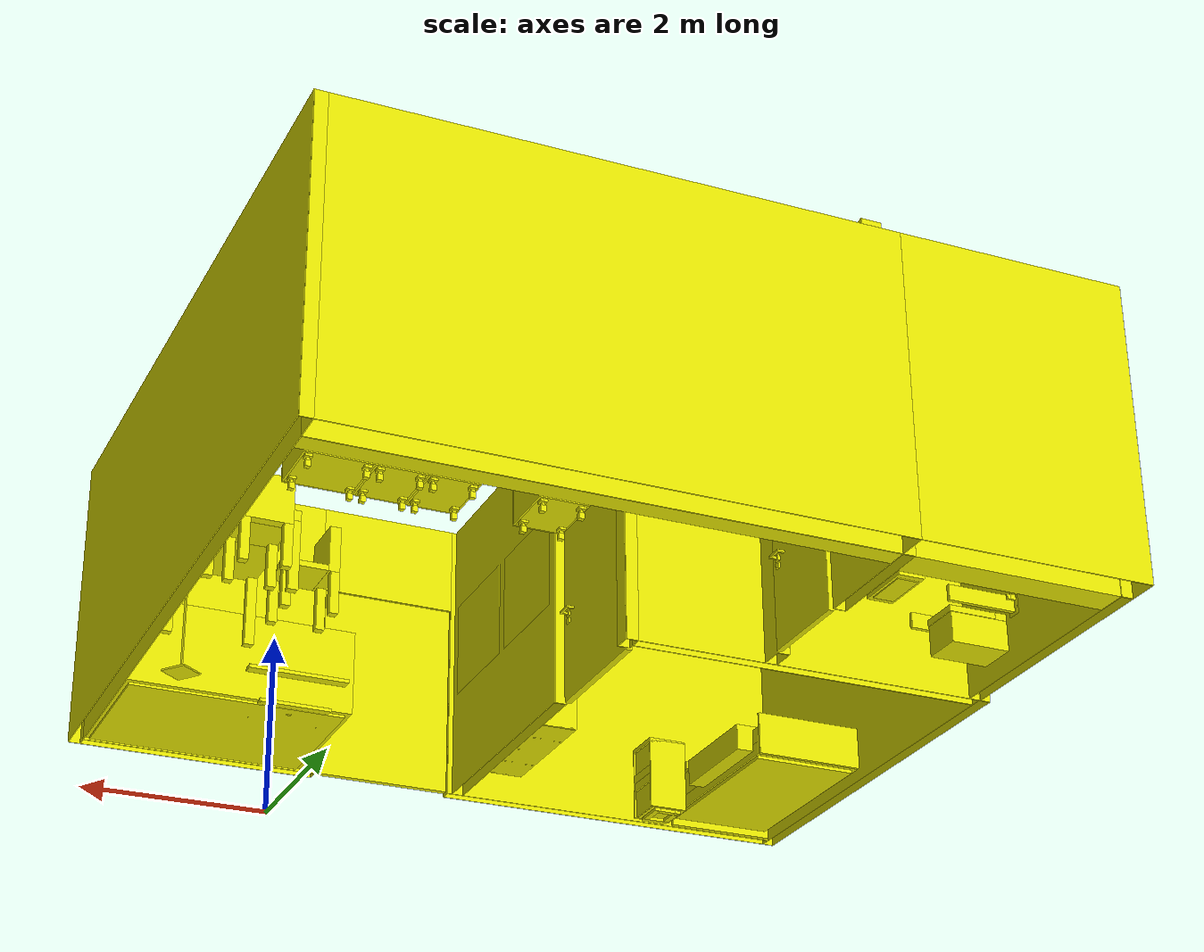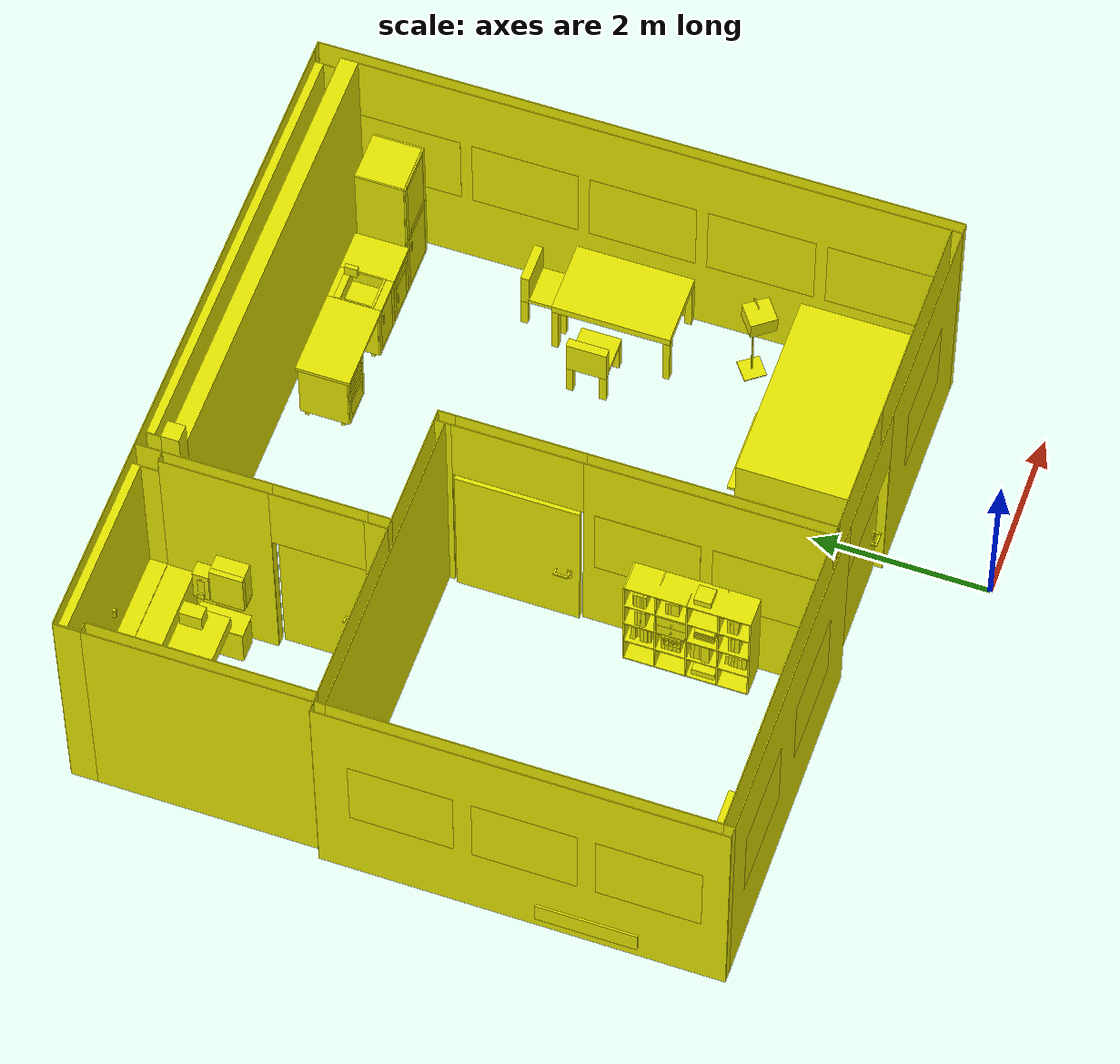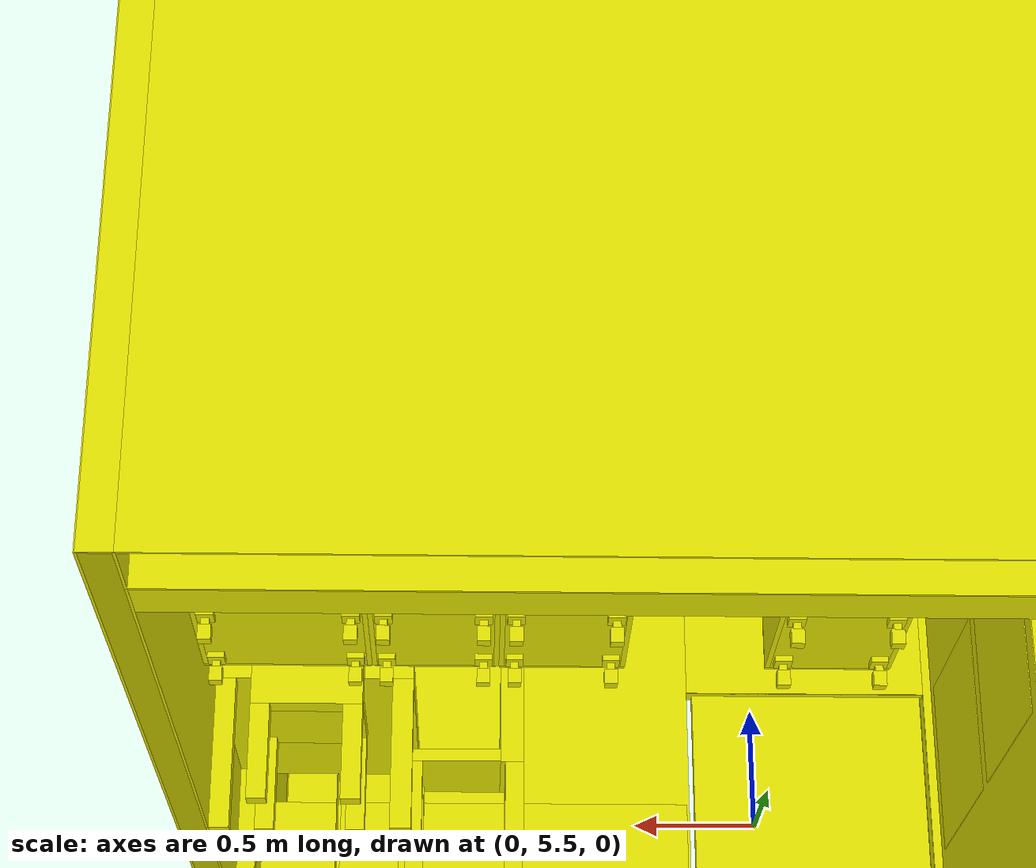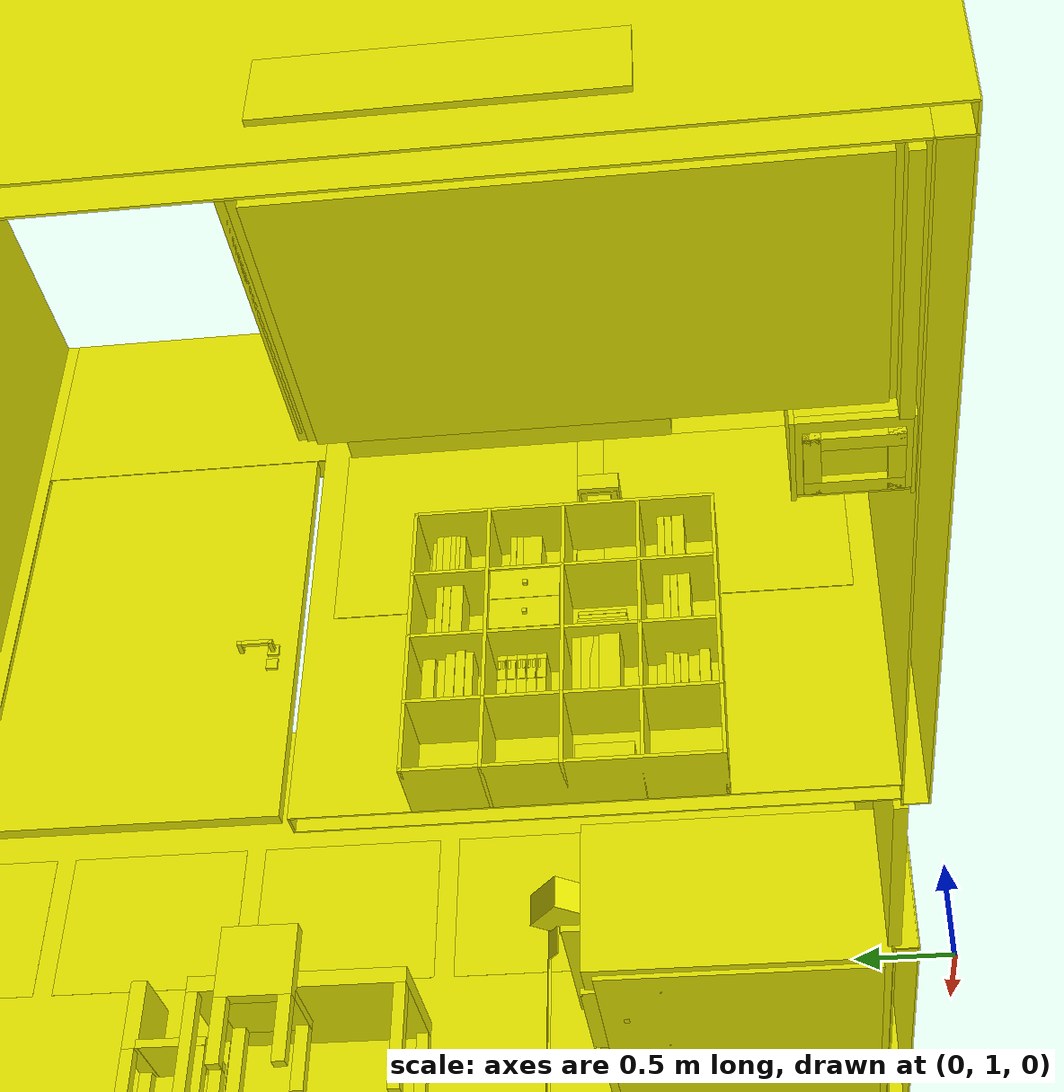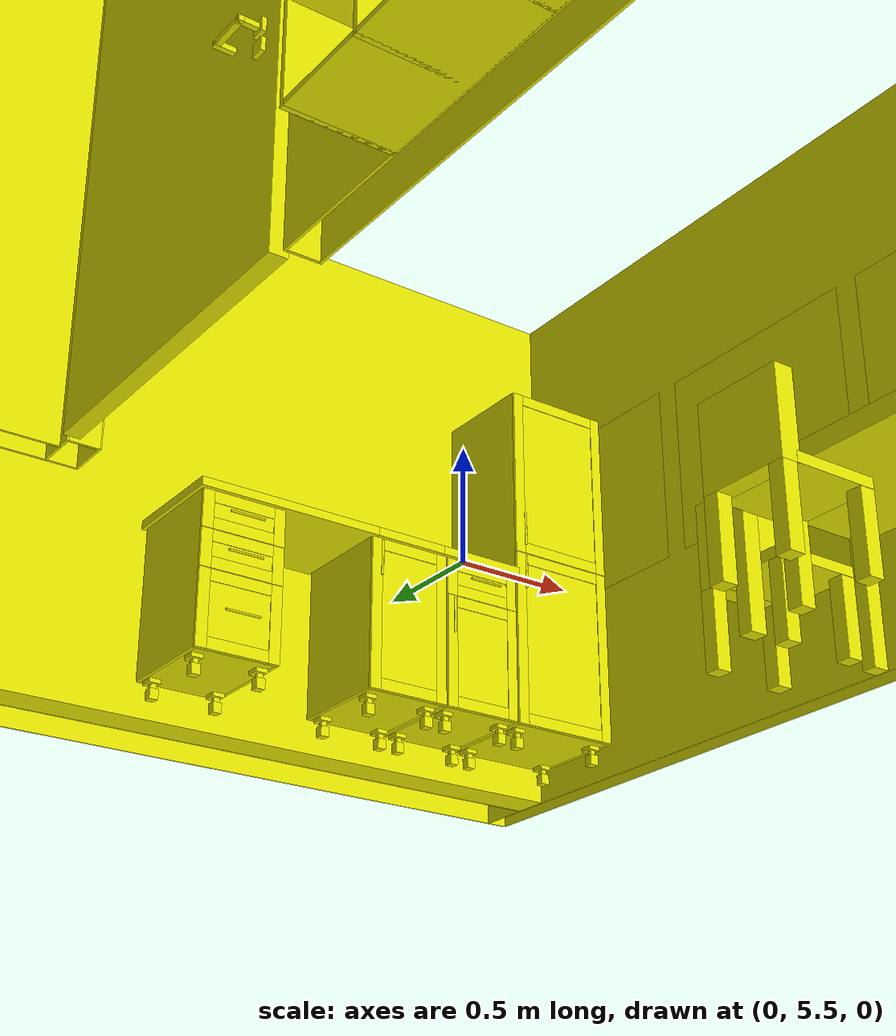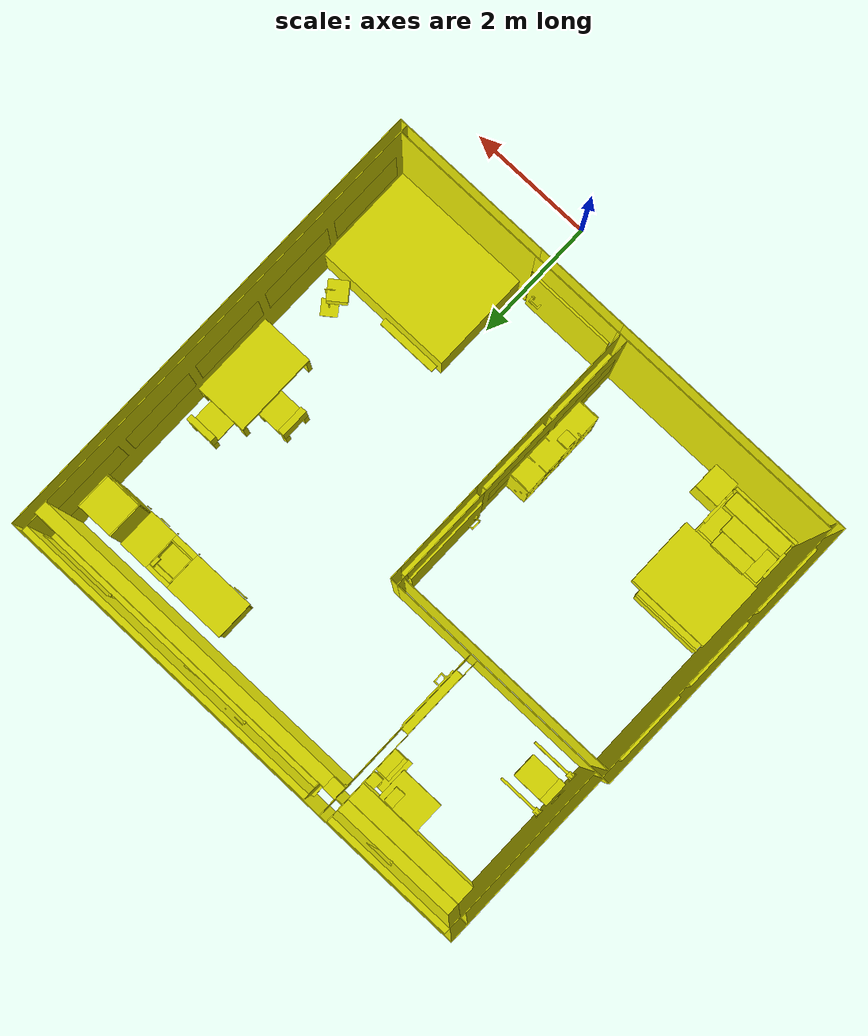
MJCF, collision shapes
<mujoco model="scene_garmi-apartment">
  <compiler angle="degree" meshdir="meshes" texturedir="textures"/>
  <default>
    <joint armature="0.01" damping="0.5"/>
    <default class="visual">
      <geom contype="0" conaffinity="0" group="2"/>
    </default>
    <default class="collision">
      <geom rgba="0.9 0.9 0.0 0.2" group="3"/>
    </default>
  </default>
  <asset>
    <material name="M_MI_5941f12764ba5c3d8f8b4933" rgba="0.6659 0.6659 0.6659 1.0000"/>
    <material name="M_MI_5b14afd6295a435b84dcd65f" rgba="1.0000 1.0000 1.0000 1.0000"/>
    <texture name="T_MI_5cd4d31f44c5ba48546d2e5f" type="2d" file="MI_5cd4d31f44c5ba48546d2e5f.png"/>
    <material name="M_MI_5cd4d31f44c5ba48546d2e5f" texture="T_MI_5cd4d31f44c5ba48546d2e5f"/>
    <texture name="T_MI_5cd4d31f44c5ba48546d2e60" type="2d" file="MI_5cd4d31f44c5ba48546d2e60.png"/>
    <material name="M_MI_5cd4d31f44c5ba48546d2e60" texture="T_MI_5cd4d31f44c5ba48546d2e60"/>
    <texture name="T_MI_5cd4d31f44c5ba48546d2e61" type="2d" file="MI_5cd4d31f44c5ba48546d2e61.png"/>
    <material name="M_MI_5cd4d31f44c5ba48546d2e61" texture="T_MI_5cd4d31f44c5ba48546d2e61"/>
    <texture name="T_MI_5cd4d31f44c5ba48546d2e62" type="2d" file="MI_5cd4d31f44c5ba48546d2e62.png"/>
    <material name="M_MI_5cd4d31f44c5ba48546d2e62" texture="T_MI_5cd4d31f44c5ba48546d2e62"/>
    <texture name="T_MI_5cd4d31f44c5ba48546d2e64" type="2d" file="MI_5cd4d31f44c5ba48546d2e64.png"/>
    <material name="M_MI_5cd4d31f44c5ba48546d2e64" texture="T_MI_5cd4d31f44c5ba48546d2e64"/>
    <texture name="T_MI_5cd4d31f44c5ba48546d2e65" type="2d" file="MI_5cd4d31f44c5ba48546d2e65.png"/>
    <material name="M_MI_5cd4d31f44c5ba48546d2e65" texture="T_MI_5cd4d31f44c5ba48546d2e65"/>
    <texture name="T_MI_5cd4d31f44c5ba48546d2e66" type="2d" file="MI_5cd4d31f44c5ba48546d2e66.png"/>
    <material name="M_MI_5cd4d31f44c5ba48546d2e66" texture="T_MI_5cd4d31f44c5ba48546d2e66"/>
    <texture name="T_MI_5cd4d31f44c5ba48546d2e68" type="2d" file="MI_5cd4d31f44c5ba48546d2e68.png"/>
    <material name="M_MI_5cd4d31f44c5ba48546d2e68" texture="T_MI_5cd4d31f44c5ba48546d2e68"/>
    <texture name="T_MI_5cd4d31f44c5ba48546d2e69" type="2d" file="MI_5cd4d31f44c5ba48546d2e69.png"/>
    <material name="M_MI_5cd4d31f44c5ba48546d2e69" texture="T_MI_5cd4d31f44c5ba48546d2e69"/>
    <texture name="T_MI_5cd4d31f44c5ba48546d2e6b" type="2d" file="MI_5cd4d31f44c5ba48546d2e6b.png"/>
    <material name="M_MI_5cd4d31f44c5ba48546d2e6b" texture="T_MI_5cd4d31f44c5ba48546d2e6b"/>
    <texture name="T_MI_5cd92ea244c5ba48546d8c1c" type="2d" file="MI_5cd92ea244c5ba48546d8c1c.png"/>
    <material name="M_MI_5cd92ea244c5ba48546d8c1c" texture="T_MI_5cd92ea244c5ba48546d8c1c"/>
    <texture name="T_MI_5cd92ea344c5ba48546d8c1e" type="2d" file="MI_5cd92ea344c5ba48546d8c1e.png"/>
    <material name="M_MI_5cd92ea344c5ba48546d8c1e" texture="T_MI_5cd92ea344c5ba48546d8c1e"/>
    <texture name="T_MI_5cd92ea344c5ba48546d8c1f" type="2d" file="MI_5cd92ea344c5ba48546d8c1f.png"/>
    <material name="M_MI_5cd92ea344c5ba48546d8c1f" texture="T_MI_5cd92ea344c5ba48546d8c1f"/>
    <texture name="T_MI_5cd92ea344c5ba48546d8c20" type="2d" file="MI_5cd92ea344c5ba48546d8c20.png"/>
    <material name="M_MI_5cd92ea344c5ba48546d8c20" texture="T_MI_5cd92ea344c5ba48546d8c20"/>
    <texture name="T_MI_5cd92ea344c5ba48546d8c21" type="2d" file="MI_5cd92ea344c5ba48546d8c21.png"/>
    <material name="M_MI_5cd92ea344c5ba48546d8c21" texture="T_MI_5cd92ea344c5ba48546d8c21"/>
    <texture name="T_MI_5cd92ea344c5ba48546d8c23" type="2d" file="MI_5cd92ea344c5ba48546d8c23.png"/>
    <material name="M_MI_5cd92ea344c5ba48546d8c23" texture="T_MI_5cd92ea344c5ba48546d8c23"/>
    <material name="M_MI_5d004ae60e49522efe609fc6" rgba="0.9529 0.9529 0.9529 1.0000"/>
    <material name="M_MI_5d004ae60e49522efe609fc7" rgba="0.9415 0.9415 0.9415 1.0000"/>
    <texture name="T_MI_5da8169a7d6a630001637dbc" type="2d" file="MI_5da8169a7d6a630001637dbc.png"/>
    <material name="M_MI_5da8169a7d6a630001637dbc" texture="T_MI_5da8169a7d6a630001637dbc"/>
    <material name="M_MI_5dbfaef300e3a30001c5e4eb" rgba="0.2800 0.2800 0.2800 1.0000"/>
    <texture name="T_MI_5e13fb1cb1d8ad0001dacb33" type="2d" file="MI_5e13fb1cb1d8ad0001dacb33.png"/>
    <material name="M_MI_5e13fb1cb1d8ad0001dacb33" texture="T_MI_5e13fb1cb1d8ad0001dacb33"/>
    <texture name="T_MI_60c06296d849e100017b5f27" type="2d" file="MI_60c06296d849e100017b5f27.png"/>
    <material name="M_MI_60c06296d849e100017b5f27" texture="T_MI_60c06296d849e100017b5f27" rgba="0.0605 0.0605 0.0605 1.0000"/>
    <texture name="T_MI_60dc421500e3a300019c8d24" type="2d" file="MI_60dc421500e3a300019c8d24.png"/>
    <material name="M_MI_60dc421500e3a300019c8d24" texture="T_MI_60dc421500e3a300019c8d24" rgba="1.0000 1.0000 1.0000 0.2000"/>
    <texture name="T_MI_60dc421523bc840001ec60ab" type="2d" file="MI_60dc421523bc840001ec60ab.png"/>
    <material name="M_MI_60dc421523bc840001ec60ab" texture="T_MI_60dc421523bc840001ec60ab"/>
    <material name="M_MI_60dc42155974ed000143128a" rgba="1.0000 1.0000 1.0000 0.2000"/>
    <texture name="T_MI_60dc4215b1d8ad0001cc79be" type="2d" file="MI_60dc4215b1d8ad0001cc79be.png"/>
    <material name="M_MI_60dc4215b1d8ad0001cc79be" texture="T_MI_60dc4215b1d8ad0001cc79be"/>
    <texture name="T_MI_60dc4215d849e10001f6e5b3" type="2d" file="MI_60dc4215d849e10001f6e5b3.png"/>
    <material name="M_MI_60dc4215d849e10001f6e5b3" texture="T_MI_60dc4215d849e10001f6e5b3"/>
    <texture name="T_MI_60dc4215e113f60001131387" type="2d" file="MI_60dc4215e113f60001131387.png"/>
    <material name="M_MI_60dc4215e113f60001131387" texture="T_MI_60dc4215e113f60001131387"/>
    <texture name="T_MI_6123a2596199ee0001bf7406" type="2d" file="MI_6123a2596199ee0001bf7406.png"/>
    <material name="M_MI_6123a2596199ee0001bf7406" texture="T_MI_6123a2596199ee0001bf7406" rgba="0.0750 0.0911 0.1429 1.0000"/>
    <texture name="T_MI_61447906e1065000012c6ee1" type="2d" file="MI_61447906e1065000012c6ee1.png"/>
    <material name="M_MI_61447906e1065000012c6ee1" texture="T_MI_61447906e1065000012c6ee1"/>
    <texture name="T_MI_61447906f42f43000148acf5" type="2d" file="MI_61447906f42f43000148acf5.png"/>
    <material name="M_MI_61447906f42f43000148acf5" texture="T_MI_61447906f42f43000148acf5"/>
    <texture name="T_MI_614479079ad9f8000189a00f" type="2d" file="MI_614479079ad9f8000189a00f.png"/>
    <material name="M_MI_614479079ad9f8000189a00f" texture="T_MI_614479079ad9f8000189a00f"/>
    <texture name="T_MI_61447907bf3c59000190554f" type="2d" file="MI_61447907bf3c59000190554f.png"/>
    <material name="M_MI_61447907bf3c59000190554f" texture="T_MI_61447907bf3c59000190554f"/>
    <material name="M_MI_615057aa53decf0001cd1a42" rgba="0.8196 0.8196 0.8196 1.0000"/>
    <material name="M_MI_615057aac43c660001cad6d8" rgba="1.0000 1.0000 1.0000 1.0000"/>
    <texture name="T_MI_627336a9a7755a0001f24681" type="2d" file="MI_627336a9a7755a0001f24681.png"/>
    <material name="M_MI_627336a9a7755a0001f24681" texture="T_MI_627336a9a7755a0001f24681"/>
    <texture name="T_MI_627336a9a7755a0001f24681_51" type="2d" file="MI_627336a9a7755a0001f24681.png"/>
    <material name="M_MI_627336a9a7755a0001f24681_51" texture="T_MI_627336a9a7755a0001f24681_51"/>
    <material name="M_MI_628d91af1ab3ee0001ed70ac" rgba="0.5036 0.5036 0.5036 1.0000"/>
    <material name="M_MI_62b927503c8e01000196f5fd" rgba="0.6498 0.4757 0.3943 1.0000"/>
    <texture name="T_MI_62b9275058b9620001e2964e" type="2d" file="MI_62b9275058b9620001e2964e.png"/>
    <material name="M_MI_62b9275058b9620001e2964e" texture="T_MI_62b9275058b9620001e2964e"/>
    <material name="M_MI_62b92750bd9b4c0001746c3e" rgba="0.1936 0.1936 0.1936 1.0000"/>
    <material name="M_MI_62b92750dd9b430001dca9d8" rgba="0.0047 0.0047 0.0047 1.0000"/>
    <material name="M_MI_62b92750f4b6820001f720f2" rgba="0.7558 0.7558 0.7558 1.0000"/>
    <material name="M_MI_634fb2920a498a00013aa342" rgba="0.0049 0.0049 0.0049 1.0000"/>
    <texture name="T_MI_634fb2924927a10001b80e8d" type="2d" file="MI_634fb2924927a10001b80e8d.png"/>
    <material name="M_MI_634fb2924927a10001b80e8d" texture="T_MI_634fb2924927a10001b80e8d"/>
    <material name="M_MI_634fb2925ca9a400010a020f" rgba="0.5880 0.5880 0.5880 1.0000"/>
    <texture name="T_MI_634fb2926cb4ba0001e92ffe" type="2d" file="MI_634fb2926cb4ba0001e92ffe.png"/>
    <material name="M_MI_634fb2926cb4ba0001e92ffe" texture="T_MI_634fb2926cb4ba0001e92ffe"/>
    <texture name="T_MI_634fb292b2753300012d7d05" type="2d" file="MI_634fb292b2753300012d7d05.png"/>
    <material name="M_MI_634fb292b2753300012d7d05" texture="T_MI_634fb292b2753300012d7d05"/>
    <texture name="T_MI_63c44ac798058400013993eb" type="2d" file="MI_63c44ac798058400013993eb.png"/>
    <material name="M_MI_63c44ac798058400013993eb" texture="T_MI_63c44ac798058400013993eb"/>
    <texture name="T_MI_63c44ac7982bda00019444fc" type="2d" file="MI_63c44ac7982bda00019444fc.png"/>
    <material name="M_MI_63c44ac7982bda00019444fc" texture="T_MI_63c44ac7982bda00019444fc"/>
    <texture name="T_MI_63c44ac79f257e0001af061a" type="2d" file="MI_63c44ac79f257e0001af061a.png"/>
    <material name="M_MI_63c44ac79f257e0001af061a" texture="T_MI_63c44ac79f257e0001af061a"/>
    <texture name="T_MI_64464f31d7c7aa0001b073db" type="2d" file="MI_64464f31d7c7aa0001b073db.png"/>
    <material name="M_MI_64464f31d7c7aa0001b073db" texture="T_MI_64464f31d7c7aa0001b073db" rgba="0.4927 0.4102 0.3413 1.0000"/>
    <material name="M_MI_64464f6ad7c7aa0001b075f3" rgba="0.0248 0.0246 0.0247 1.0000"/>
    <texture name="T_MI_64464fcbd7c7aa0001b0787a" type="2d" file="MI_64464fcbd7c7aa0001b0787a.png"/>
    <material name="M_MI_64464fcbd7c7aa0001b0787a" texture="T_MI_64464fcbd7c7aa0001b0787a"/>
    <texture name="T_MI_6446510cd7c7aa0001b081b1" type="2d" file="MI_6446510cd7c7aa0001b081b1.png"/>
    <material name="M_MI_6446510cd7c7aa0001b081b1" texture="T_MI_6446510cd7c7aa0001b081b1"/>
    <texture name="T_MI_6446510cd7c7aa0001b081b1_116" type="2d" file="MI_6446510cd7c7aa0001b081b1.png"/>
    <material name="M_MI_6446510cd7c7aa0001b081b1_116" texture="T_MI_6446510cd7c7aa0001b081b1_116"/>
    <texture name="T_MI_648b112f794abe0001b5d8a9" type="2d" file="MI_648b112f794abe0001b5d8a9.png"/>
    <material name="M_MI_648b112f794abe0001b5d8a9" texture="T_MI_648b112f794abe0001b5d8a9"/>
    <texture name="T_MI_648b112fe5538f0001f54457" type="2d" file="MI_648b112fe5538f0001f54457.png"/>
    <material name="M_MI_648b112fe5538f0001f54457" texture="T_MI_648b112fe5538f0001f54457"/>
    <material name="M_MI_64a26f343b8c16000118d348" rgba="0.5880 0.5880 0.5880 1.0000"/>
    <material name="M_MI_64a26f343ebf270001dbc0f3" rgba="0.5880 0.5880 0.5880 1.0000"/>
    <material name="M_MI_64a26f347b206c000189235e" rgba="0.5880 0.5880 0.5880 1.0000"/>
    <material name="M_MI_64a26f34848d9e00015bcef3" rgba="0.3098 0.2392 0.1333 1.0000"/>
    <material name="M_MI_64a26f34929f7e0001577461" rgba="0.5880 0.5880 0.5880 1.0000"/>
    <material name="M_MI_64a26f34ae0f5a000139c07f" rgba="0.9608 0.9608 0.9608 1.0000"/>
    <material name="M_MI_64a26f34dd85f10001d13fa9" rgba="0.0118 0.0118 0.0118 1.0000"/>
    <material name="M_MI_64a26f34ef53760001248249" rgba="0.0078 0.0078 0.0078 1.0000"/>
    <material name="M_MI_64b4f7c94e902400013f663d" rgba="0.8751 0.8751 0.8751 1.0000"/>
    <texture name="T_MI_6538d6f07a627f0001f300b4" type="2d" file="MI_6538d6f07a627f0001f300b4.png"/>
    <material name="M_MI_6538d6f07a627f0001f300b4" texture="T_MI_6538d6f07a627f0001f300b4"/>
    <texture name="T_MI_6538d6f0b3b4180001cc70ff" type="2d" file="MI_6538d6f0b3b4180001cc70ff.png"/>
    <material name="M_MI_6538d6f0b3b4180001cc70ff" texture="T_MI_6538d6f0b3b4180001cc70ff"/>
    <texture name="T_MI_6545ced8a7a1dd0001750c62" type="2d" file="MI_6545ced8a7a1dd0001750c62.png"/>
    <material name="M_MI_6545ced8a7a1dd0001750c62" texture="T_MI_6545ced8a7a1dd0001750c62"/>
    <texture name="T_MI_66232ca007925a0001f72b8d" type="2d" file="MI_66232ca007925a0001f72b8d.png"/>
    <material name="M_MI_66232ca007925a0001f72b8d" texture="T_MI_66232ca007925a0001f72b8d" rgba="0.0236 0.0236 0.0236 1.0000"/>
    <texture name="T_MI_66bc224f3d07d20001b00f34" type="2d" file="MI_66bc224f3d07d20001b00f34.png"/>
    <material name="M_MI_66bc224f3d07d20001b00f34" texture="T_MI_66bc224f3d07d20001b00f34" rgba="0.0078 0.0078 0.0078 1.0000"/>
    <texture name="T_MI_66bc224f60cf470001aa7554" type="2d" file="MI_66bc224f60cf470001aa7554.png"/>
    <material name="M_MI_66bc224f60cf470001aa7554" texture="T_MI_66bc224f60cf470001aa7554" rgba="0.6307 0.6307 0.6307 1.0000"/>
    <material name="M_MI_66bc224fed34ab000159d598" rgba="0.8383 0.8246 0.8431 1.0000"/>
    <texture name="T_MI_66ea513899c42400011dfb1a" type="2d" file="MI_66ea513899c42400011dfb1a.png"/>
    <material name="M_MI_66ea513899c42400011dfb1a" texture="T_MI_66ea513899c42400011dfb1a"/>
    <material name="M_MI_66ea51389ca5eb00010dcd61" rgba="0.6510 0.6196 0.6039 1.0000"/>
    <texture name="T_MI_66ea5138c049190001823cb3" type="2d" file="MI_66ea5138c049190001823cb3.png"/>
    <material name="M_MI_66ea5138c049190001823cb3" texture="T_MI_66ea5138c049190001823cb3"/>
    <material name="M_MI_66fa27790319cb00018960b1" rgba="0.6773 0.5613 0.4288 1.0000"/>
    <material name="M_MI_66fa2779781af100017d61c0" rgba="0.1176 0.1176 0.1176 1.0000"/>
    <material name="M_MI_67457dfe1a0e0b0001c8e9be" rgba="0.3280 0.2548 0.1854 1.0000"/>
    <texture name="T_MI_67457dfe42f977000171ebaf" type="2d" file="MI_67457dfe42f977000171ebaf.png"/>
    <material name="M_MI_67457dfe42f977000171ebaf" texture="T_MI_67457dfe42f977000171ebaf" rgba="0.3098 0.3137 0.3216 1.0000"/>
    <material name="M_MI_67457dfe4c563e0001da085d" rgba="0.5701 0.5701 0.5701 1.0000"/>
    <material name="M_MI_67457dfe69184d000190ae59" rgba="0.0667 0.0745 0.0863 1.0000"/>
    <material name="M_MI_67457dfe7f2d7700012e7ddc" rgba="0.6934 0.6934 0.6934 1.0000"/>
    <texture name="T_MI_67457dfe8a488c000100a2fc" type="2d" file="MI_67457dfe8a488c000100a2fc.png"/>
    <material name="M_MI_67457dfe8a488c000100a2fc" texture="T_MI_67457dfe8a488c000100a2fc" rgba="0.8275 0.8275 0.8275 1.0000"/>
    <material name="M_MI_67457dfe946140000126f6bb" rgba="0.5000 0.5000 0.5000 1.0000"/>
    <texture name="T_MI_67d00d120e73830001542738" type="2d" file="MI_67d00d120e73830001542738.png"/>
    <material name="M_MI_67d00d120e73830001542738" texture="T_MI_67d00d120e73830001542738"/>
    <texture name="T_MI_67d00d127082790001760866" type="2d" file="MI_67d00d127082790001760866.png"/>
    <material name="M_MI_67d00d127082790001760866" texture="T_MI_67d00d127082790001760866"/>
    <texture name="T_MI_67d00d12832a370001412fa6" type="2d" file="MI_67d00d12832a370001412fa6.png"/>
    <material name="M_MI_67d00d12832a370001412fa6" texture="T_MI_67d00d12832a370001412fa6"/>
    <texture name="T_MI_67d00d12ed9ca90001d18b51" type="2d" file="MI_67d00d12ed9ca90001d18b51.png"/>
    <material name="M_MI_67d00d12ed9ca90001d18b51" texture="T_MI_67d00d12ed9ca90001d18b51"/>
    <material name="M_MI_67d00d12f6fcf8000111714f" rgba="0.8314 0.8314 0.8314 1.0000"/>
    <texture name="T_MI_6901e2534250ba0001e32401" type="2d" file="MI_6901e2534250ba0001e32401.png"/>
    <material name="M_MI_6901e2534250ba0001e32401" texture="T_MI_6901e2534250ba0001e32401"/>
    <texture name="T_MI_6901e25367179a0001f8a2c1" type="2d" file="MI_6901e25367179a0001f8a2c1.png"/>
    <material name="M_MI_6901e25367179a0001f8a2c1" texture="T_MI_6901e25367179a0001f8a2c1"/>
    <texture name="T_MI_6901e253a4abe600012480fb" type="2d" file="MI_6901e253a4abe600012480fb.png"/>
    <material name="M_MI_6901e253a4abe600012480fb" texture="T_MI_6901e253a4abe600012480fb"/>
    <texture name="T_MI_6901e253d4eb9b0001b7c1d3" type="2d" file="MI_6901e253d4eb9b0001b7c1d3.png"/>
    <material name="M_MI_6901e253d4eb9b0001b7c1d3" texture="T_MI_6901e253d4eb9b0001b7c1d3"/>
    <texture name="T_MI_6901e253ddcf760001f2cc47" type="2d" file="MI_6901e253ddcf760001f2cc47.png"/>
    <material name="M_MI_6901e253ddcf760001f2cc47" texture="T_MI_6901e253ddcf760001f2cc47"/>
    <texture name="T_MI_6901e253f9645a0001ea9c57" type="2d" file="MI_6901e253f9645a0001ea9c57.png"/>
    <material name="M_MI_6901e253f9645a0001ea9c57" texture="T_MI_6901e253f9645a0001ea9c57"/>
    <material name="M_MI_69a94c449cde3a0ce4db02e1" rgba="1.0000 1.0000 1.0000 0.2000"/>
    <material name="M_MI_69a94c44a4e99f0260973c5d" rgba="0.6588 0.6588 0.6588 1.0000"/>
    <material name="M_MI_69a94c44b2d62e39cc4fb332" rgba="0.0137 0.0137 0.0137 1.0000"/>
    <material name="M_MI_69a94c574a5e0e5a73c2aabd" rgba="0.6588 0.6588 0.6588 1.0000"/>
    <material name="M_MI_69a94c577b1fa00d59fc4c92" rgba="1.0000 1.0000 1.0000 1.0000"/>
    <material name="M_MI_69a94c57aa621f3942e038a5" rgba="1.0000 1.0000 1.0000 0.2000"/>
    <material name="M_MI_69a94c582fb81a2d4439a44e" rgba="0.0078 0.0078 0.0078 1.0000"/>
    <material name="M_MI_69a94c582fb81a2d4439a44f" rgba="1.0000 1.0000 1.0000 1.0000"/>
    <material name="M_MI_69a94c583d868a4a60258225" rgba="1.0000 1.0000 1.0000 1.0000"/>
    <material name="M_MI_69a94c583d868a4a60258226" rgba="1.0000 1.0000 1.0000 0.2000"/>
    <material name="M_MI_69a94c5841d1547e3f1d8c8e" rgba="0.6588 0.6588 0.6588 1.0000"/>
    <material name="M_MI_69a94c58a4e99f0260973c62" rgba="0.0078 0.0078 0.0078 1.0000"/>
    <material name="M_MI_69a94c58a4e99f0260973c63" rgba="0.6588 0.6588 0.6588 1.0000"/>
    <material name="M_MI_69a94c58aa621f3942e038a6" rgba="0.0078 0.0078 0.0078 1.0000"/>
    <material name="M_MI_69a96c776425ff1c5602d505" rgba="0.6588 0.6588 0.6588 1.0000"/>
    <texture name="T_MI_69a97bbbeac1cc195cdac43d" type="2d" file="MI_69a97bbbeac1cc195cdac43d.png"/>
    <material name="M_MI_69a97bbbeac1cc195cdac43d" texture="T_MI_69a97bbbeac1cc195cdac43d" rgba="0.5130 0.2496 0.0728 1.0000"/>
    <texture name="T_MI_69a97bbbeac1cc195cdac43d_124" type="2d" file="MI_69a97bbbeac1cc195cdac43d.png"/>
    <material name="M_MI_69a97bbbeac1cc195cdac43d_124" texture="T_MI_69a97bbbeac1cc195cdac43d_124" rgba="0.5130 0.2496 0.0728 1.0000"/>
    <texture name="T_MI_69a97bbbeac1cc195cdac43d_59" type="2d" file="MI_69a97bbbeac1cc195cdac43d.png"/>
    <material name="M_MI_69a97bbbeac1cc195cdac43d_59" texture="T_MI_69a97bbbeac1cc195cdac43d_59" rgba="0.5130 0.2496 0.0728 1.0000"/>
    <material name="M_MI_69a981fe41d1547e3f1d9921" rgba="0.0137 0.0137 0.0137 1.0000"/>
    <texture name="T_MI_69a981fe750d867bb882ecfe" type="2d" file="MI_69a981fe750d867bb882ecfe.png"/>
    <material name="M_MI_69a981fe750d867bb882ecfe" texture="T_MI_69a981fe750d867bb882ecfe" rgba="0.6316 0.6316 0.6316 1.0000"/>
    <material name="M_MI_69a981fe7b1fa00d59fc595e" rgba="1.0000 1.0000 1.0000 0.2000"/>
    <texture name="T_MI_69a981fec6416e6f76edd7c3" type="2d" file="MI_69a981fec6416e6f76edd7c3.png"/>
    <material name="M_MI_69a981fec6416e6f76edd7c3" texture="T_MI_69a981fec6416e6f76edd7c3" rgba="0.6316 0.6316 0.6316 1.0000"/>
    <material name="M_MI_69a981fecf67ca1d1dbdacbf" rgba="0.0137 0.0137 0.0137 1.0000"/>
    <material name="M_MI_69a981fef743a551dfda181d" rgba="1.0000 1.0000 1.0000 0.2000"/>
    <material name="M_MI_69ae32f98addd433aebf0490" rgba="0.0838 0.0838 0.0838 1.0000"/>
    <material name="M_MI_69af7e4b750d867bb883d789" rgba="0.7970 0.5524 0.2415 1.0000"/>
    <material name="M_MI_69af7e4bf94685057dada22f" rgba="0.6588 0.6588 0.6588 1.0000"/>
    <mesh name="Window00" file="Window00.obj" inertia="shell"/>
    <mesh name="Window01" file="Window01.obj" inertia="shell"/>
    <mesh name="Window10" file="Window10.obj" inertia="shell"/>
    <mesh name="Window11" file="Window11.obj" inertia="shell"/>
    <mesh name="Window20" file="Window20.obj" inertia="shell"/>
    <mesh name="Window21" file="Window21.obj" inertia="shell"/>
    <mesh name="Window30" file="Window30.obj" inertia="shell"/>
    <mesh name="Window31" file="Window31.obj" inertia="shell"/>
    <mesh name="Window40" file="Window40.obj" inertia="shell"/>
    <mesh name="Window41" file="Window41.obj" inertia="shell"/>
    <mesh name="Window50" file="Window50.obj" inertia="shell"/>
    <mesh name="Window51" file="Window51.obj" inertia="shell"/>
    <mesh name="Window60" file="Window60.obj" inertia="shell"/>
    <mesh name="Window61" file="Window61.obj" inertia="shell"/>
    <mesh name="Window70" file="Window70.obj" inertia="shell"/>
    <mesh name="Window71" file="Window71.obj" inertia="shell"/>
    <mesh name="Window80" file="Window80.obj" inertia="shell"/>
    <mesh name="Window81" file="Window81.obj" inertia="shell"/>
    <mesh name="Window90" file="Window90.obj" inertia="shell"/>
    <mesh name="Window91" file="Window91.obj" inertia="shell"/>
    <mesh name="Window100" file="Window100.obj" inertia="shell"/>
    <mesh name="Window101" file="Window101.obj" inertia="shell"/>
    <mesh name="Window110" file="Window110.obj" inertia="shell"/>
    <mesh name="Window111" file="Window111.obj" inertia="shell"/>
    <mesh name="Window120" file="Window120.obj" inertia="shell"/>
    <mesh name="Window121" file="Window121.obj" inertia="shell"/>
    <mesh name="Window130" file="Window130.obj"/>
    <mesh name="Window131" file="Window131.obj"/>
    <mesh name="Window132" file="Window132.obj" inertia="shell"/>
    <mesh name="Window133" file="Window133.obj" inertia="shell"/>
    <mesh name="Window134" file="Window134.obj" inertia="shell"/>
    <mesh name="Window135" file="Window135.obj" inertia="shell"/>
    <mesh name="Window136" file="Window136.obj" inertia="shell"/>
    <mesh name="Window137" file="Window137.obj" inertia="shell"/>
    <mesh name="Window138" file="Window138.obj" inertia="shell"/>
    <mesh name="Window139" file="Window139.obj" inertia="shell"/>
    <mesh name="Window1310" file="Window1310.obj" inertia="shell"/>
    <mesh name="Window1311" file="Window1311.obj" inertia="shell"/>
    <mesh name="Window1312" file="Window1312.obj" inertia="shell"/>
    <mesh name="Window1313" file="Window1313.obj" inertia="shell"/>
    <mesh name="Window1314" file="Window1314.obj" inertia="shell"/>
    <mesh name="Window140" file="Window140.obj"/>
    <mesh name="Window141" file="Window141.obj" inertia="shell"/>
    <mesh name="Window142" file="Window142.obj" inertia="shell"/>
    <mesh name="Window143" file="Window143.obj" inertia="shell"/>
    <mesh name="Window144" file="Window144.obj" inertia="shell"/>
    <mesh name="Window145" file="Window145.obj" inertia="shell"/>
    <mesh name="Window146" file="Window146.obj" inertia="shell"/>
    <mesh name="Window147" file="Window147.obj" inertia="shell"/>
    <mesh name="BayWindowPlatform00" file="BayWindowPlatform00.obj" inertia="shell"/>
    <mesh name="BayWindowPlatform01" file="BayWindowPlatform01.obj" inertia="shell"/>
    <mesh name="BayWindowPlatform02" file="BayWindowPlatform02.obj" inertia="shell"/>
    <mesh name="BayWindowPlatform10" file="BayWindowPlatform10.obj" inertia="shell"/>
    <mesh name="BayWindowPlatform11" file="BayWindowPlatform11.obj" inertia="shell"/>
    <mesh name="BayWindowPlatform12" file="BayWindowPlatform12.obj" inertia="shell"/>
    <mesh name="ToiletPaperHolder00" file="ToiletPaperHolder00.obj" inertia="shell"/>
    <mesh name="ToiletPaperHolder01" file="ToiletPaperHolder01.obj"/>
    <mesh name="ToiletPaperHolder02" file="ToiletPaperHolder02.obj"/>
    <mesh name="ToiletPaperHolder03" file="ToiletPaperHolder03.obj" inertia="shell"/>
    <mesh name="ToiletPaperHolder04" file="ToiletPaperHolder04.obj"/>
    <mesh name="ToiletPaperHolder05" file="ToiletPaperHolder05.obj"/>
    <mesh name="ToiletPaperHolder06" file="ToiletPaperHolder06.obj"/>
    <mesh name="HandSanitizer00" file="HandSanitizer00.obj"/>
    <mesh name="HandSanitizer01" file="HandSanitizer01.obj"/>
    <mesh name="HandSanitizer02" file="HandSanitizer02.obj" inertia="shell"/>
    <mesh name="HandSanitizer03" file="HandSanitizer03.obj" inertia="shell"/>
    <mesh name="HandSanitizer04" file="HandSanitizer04.obj" inertia="shell"/>
    <mesh name="Handrail00" file="Handrail00.obj"/>
    <mesh name="Handrail01" file="Handrail01.obj"/>
    <mesh name="Handrail02" file="Handrail02.obj" inertia="shell"/>
    <mesh name="Handrail03" file="Handrail03.obj"/>
    <mesh name="Handrail04" file="Handrail04.obj" inertia="shell"/>
    <mesh name="Handrail10" file="Handrail10.obj"/>
    <mesh name="Handrail11" file="Handrail11.obj"/>
    <mesh name="Handrail12" file="Handrail12.obj" inertia="shell"/>
    <mesh name="Handrail13" file="Handrail13.obj"/>
    <mesh name="Handrail14" file="Handrail14.obj" inertia="shell"/>
    <mesh name="Radiator00" file="Radiator00.obj" inertia="shell"/>
    <mesh name="Radiator01" file="Radiator01.obj" inertia="shell"/>
    <mesh name="Radiator02" file="Radiator02.obj" inertia="shell"/>
    <mesh name="Radiator03" file="Radiator03.obj" inertia="shell"/>
    <mesh name="Radiator04" file="Radiator04.obj" inertia="shell"/>
    <mesh name="Radiator05" file="Radiator05.obj" inertia="shell"/>
    <mesh name="Radiator06" file="Radiator06.obj" inertia="shell"/>
    <mesh name="Radiator07" file="Radiator07.obj" inertia="shell"/>
    <mesh name="Radiator08" file="Radiator08.obj" inertia="shell"/>
    <mesh name="Radiator09" file="Radiator09.obj" inertia="shell"/>
    <mesh name="Radiator010" file="Radiator010.obj" inertia="shell"/>
    <mesh name="Radiator011" file="Radiator011.obj" inertia="shell"/>
    <mesh name="Radiator012" file="Radiator012.obj" inertia="shell"/>
    <mesh name="Radiator013" file="Radiator013.obj" inertia="shell"/>
    <mesh name="Radiator014" file="Radiator014.obj" inertia="shell"/>
    <mesh name="Radiator015" file="Radiator015.obj"/>
    <mesh name="Radiator016" file="Radiator016.obj" inertia="shell"/>
    <mesh name="Radiator017" file="Radiator017.obj" inertia="shell"/>
    <mesh name="Radiator018" file="Radiator018.obj" inertia="shell"/>
    <mesh name="Radiator019" file="Radiator019.obj" inertia="shell"/>
    <mesh name="Radiator020" file="Radiator020.obj" inertia="shell"/>
    <mesh name="GreenPlants00" file="GreenPlants00.obj"/>
    <mesh name="GreenPlants01" file="GreenPlants01.obj" inertia="shell"/>
    <mesh name="GreenPlants02" file="GreenPlants02.obj"/>
    <mesh name="Door00" file="Door00.obj" inertia="shell"/>
    <mesh name="Door01" file="Door01.obj" inertia="shell"/>
    <mesh name="Door02" file="Door02.obj"/>
    <mesh name="Door03" file="Door03.obj" inertia="shell"/>
    <mesh name="Door04" file="Door04.obj"/>
    <mesh name="Door05" file="Door05.obj" inertia="shell"/>
    <mesh name="Door06" file="Door06.obj" inertia="shell"/>
    <mesh name="Door07" file="Door07.obj"/>
    <mesh name="Door08" file="Door08.obj"/>
    <mesh name="Door10" file="Door10.obj" inertia="shell"/>
    <mesh name="Door11" file="Door11.obj" inertia="shell"/>
    <mesh name="Door12" file="Door12.obj"/>
    <mesh name="Door13" file="Door13.obj" inertia="shell"/>
    <mesh name="Door14" file="Door14.obj"/>
    <mesh name="Door15" file="Door15.obj" inertia="shell"/>
    <mesh name="Door16" file="Door16.obj" inertia="shell"/>
    <mesh name="Door17" file="Door17.obj"/>
    <mesh name="Door18" file="Door18.obj"/>
    <mesh name="Door20" file="Door20.obj" inertia="shell"/>
    <mesh name="Door21" file="Door21.obj" inertia="shell"/>
    <mesh name="Door22" file="Door22.obj"/>
    <mesh name="Door23" file="Door23.obj" inertia="shell"/>
    <mesh name="Door24" file="Door24.obj"/>
    <mesh name="Door25" file="Door25.obj" inertia="shell"/>
    <mesh name="Door26" file="Door26.obj"/>
    <mesh name="Door27" file="Door27.obj"/>
    <mesh name="Pipe00" file="Pipe00.obj" inertia="shell"/>
    <mesh name="Pipe01" file="Pipe01.obj"/>
    <mesh name="TrashCan00" file="TrashCan00.obj" inertia="shell"/>
    <mesh name="TrashCan01" file="TrashCan01.obj"/>
    <mesh name="TrashCan02" file="TrashCan02.obj" inertia="shell"/>
    <mesh name="TrashCan03" file="TrashCan03.obj"/>
    <mesh name="TrashCan04" file="TrashCan04.obj"/>
    <mesh name="TrashCan05" file="TrashCan05.obj"/>
    <mesh name="Toilet00" file="Toilet00.obj" inertia="shell"/>
    <mesh name="Toilet01" file="Toilet01.obj"/>
    <mesh name="Toilet02" file="Toilet02.obj"/>
    <mesh name="Toilet03" file="Toilet03.obj"/>
    <mesh name="Toilet04" file="Toilet04.obj"/>
    <mesh name="Toilet05" file="Toilet05.obj"/>
    <mesh name="Toilet06" file="Toilet06.obj" inertia="shell"/>
    <mesh name="Toilet07" file="Toilet07.obj"/>
    <mesh name="Toilet08" file="Toilet08.obj" inertia="shell"/>
    <mesh name="Toilet09" file="Toilet09.obj" inertia="shell"/>
    <mesh name="Toilet010" file="Toilet010.obj" inertia="shell"/>
    <mesh name="Toilet011" file="Toilet011.obj" inertia="shell"/>
    <mesh name="Toilet012" file="Toilet012.obj" inertia="shell"/>
    <mesh name="Sofa00" file="Sofa00.obj"/>
    <mesh name="Sofa01" file="Sofa01.obj"/>
    <mesh name="Sofa02" file="Sofa02.obj"/>
    <mesh name="Sofa03" file="Sofa03.obj"/>
    <mesh name="Sofa04" file="Sofa04.obj" inertia="shell"/>
    <mesh name="Sofa05" file="Sofa05.obj"/>
    <mesh name="FloorLamp00" file="FloorLamp00.obj"/>
    <mesh name="FloorLamp01" file="FloorLamp01.obj" inertia="shell"/>
    <mesh name="FloorLamp02" file="FloorLamp02.obj" inertia="shell"/>
    <mesh name="FloorLamp03" file="FloorLamp03.obj" inertia="shell"/>
    <mesh name="FloorLamp04" file="FloorLamp04.obj"/>
    <mesh name="FloorLamp05" file="FloorLamp05.obj"/>
    <mesh name="FloorLamp06" file="FloorLamp06.obj"/>
    <mesh name="FloorLamp07" file="FloorLamp07.obj"/>
    <mesh name="DiningTable0" file="DiningTable0.obj"/>
    <mesh name="Chair00" file="Chair00.obj" inertia="shell"/>
    <mesh name="Chair01" file="Chair01.obj"/>
    <mesh name="Chair10" file="Chair10.obj" inertia="shell"/>
    <mesh name="Chair11" file="Chair11.obj"/>
    <mesh name="Bed00" file="Bed00.obj" inertia="shell"/>
    <mesh name="Bed01" file="Bed01.obj" inertia="shell"/>
    <mesh name="Bed02" file="Bed02.obj" inertia="shell"/>
    <mesh name="Bed03" file="Bed03.obj" inertia="shell"/>
    <mesh name="Bed04" file="Bed04.obj" inertia="shell"/>
    <mesh name="Bed05" file="Bed05.obj" inertia="shell"/>
    <mesh name="Bed06" file="Bed06.obj"/>
    <mesh name="Bed07" file="Bed07.obj"/>
    <mesh name="Bed08" file="Bed08.obj"/>
    <mesh name="Bed09" file="Bed09.obj" inertia="shell"/>
    <mesh name="Bed010" file="Bed010.obj" inertia="shell"/>
    <mesh name="Bed011" file="Bed011.obj" inertia="shell"/>
    <mesh name="Bed012" file="Bed012.obj" inertia="shell"/>
    <mesh name="Bed013" file="Bed013.obj" inertia="shell"/>
    <mesh name="Bed014" file="Bed014.obj"/>
    <mesh name="Nightstand00" file="Nightstand00.obj" inertia="shell"/>
    <mesh name="Nightstand01" file="Nightstand01.obj" inertia="shell"/>
    <mesh name="Nightstand02" file="Nightstand02.obj" inertia="shell"/>
    <mesh name="Nightstand03" file="Nightstand03.obj" inertia="shell"/>
    <mesh name="Nightstand04" file="Nightstand04.obj" inertia="shell"/>
    <mesh name="Nightstand05" file="Nightstand05.obj" inertia="shell"/>
    <mesh name="Nightstand06" file="Nightstand06.obj" inertia="shell"/>
    <mesh name="Nightstand07" file="Nightstand07.obj" inertia="shell"/>
    <mesh name="Nightstand08" file="Nightstand08.obj" inertia="shell"/>
    <mesh name="Nightstand09" file="Nightstand09.obj" inertia="shell"/>
    <mesh name="Nightstand010" file="Nightstand010.obj" inertia="shell"/>
    <mesh name="Nightstand011" file="Nightstand011.obj" inertia="shell"/>
    <mesh name="Nightstand012" file="Nightstand012.obj" inertia="shell"/>
    <mesh name="Nightstand013" file="Nightstand013.obj" inertia="shell"/>
    <mesh name="Nightstand014" file="Nightstand014.obj" inertia="shell"/>
    <mesh name="Nightstand015" file="Nightstand015.obj" inertia="shell"/>
    <mesh name="Nightstand016" file="Nightstand016.obj" inertia="shell"/>
    <mesh name="Nightstand017" file="Nightstand017.obj" inertia="shell"/>
    <mesh name="Nightstand018" file="Nightstand018.obj" inertia="shell"/>
    <mesh name="Nightstand019" file="Nightstand019.obj" inertia="shell"/>
    <mesh name="Nightstand020" file="Nightstand020.obj" inertia="shell"/>
    <mesh name="Nightstand021" file="Nightstand021.obj" inertia="shell"/>
    <mesh name="Nightstand022" file="Nightstand022.obj" inertia="shell"/>
    <mesh name="Nightstand023" file="Nightstand023.obj" inertia="shell"/>
    <mesh name="Basin00" file="Basin00.obj"/>
    <mesh name="Basin01" file="Basin01.obj"/>
    <mesh name="Basin02" file="Basin02.obj"/>
    <mesh name="Basin03" file="Basin03.obj"/>
    <mesh name="Basin04" file="Basin04.obj"/>
    <mesh name="Basin05" file="Basin05.obj" inertia="shell"/>
    <mesh name="Basin06" file="Basin06.obj" inertia="shell"/>
    <mesh name="CoffeeTable00" file="CoffeeTable00.obj" inertia="shell"/>
    <mesh name="CoffeeTable01" file="CoffeeTable01.obj" inertia="shell"/>
    <mesh name="CoffeeTable02" file="CoffeeTable02.obj" inertia="shell"/>
    <mesh name="CoffeeTable03" file="CoffeeTable03.obj" inertia="shell"/>
    <mesh name="CoffeeTable04" file="CoffeeTable04.obj" inertia="shell"/>
    <mesh name="CoffeeTable05" file="CoffeeTable05.obj"/>
    <mesh name="CoffeeTable06" file="CoffeeTable06.obj"/>
    <mesh name="CoffeeTable07" file="CoffeeTable07.obj"/>
    <mesh name="CoffeeTable08" file="CoffeeTable08.obj"/>
    <mesh name="Bookshelf00" file="Bookshelf00.obj"/>
    <mesh name="Bookshelf01" file="Bookshelf01.obj"/>
    <mesh name="Bookshelf02" file="Bookshelf02.obj"/>
    <mesh name="Bookshelf03" file="Bookshelf03.obj"/>
    <mesh name="Bookshelf04" file="Bookshelf04.obj"/>
    <mesh name="Book00" file="Book00.obj" inertia="shell"/>
    <mesh name="Book01" file="Book01.obj" inertia="shell"/>
    <mesh name="Book02" file="Book02.obj" inertia="shell"/>
    <mesh name="Book03" file="Book03.obj" inertia="shell"/>
    <mesh name="Book04" file="Book04.obj" inertia="shell"/>
    <mesh name="Book05" file="Book05.obj" inertia="shell"/>
    <mesh name="Book06" file="Book06.obj" inertia="shell"/>
    <mesh name="Book07" file="Book07.obj" inertia="shell"/>
    <mesh name="Book08" file="Book08.obj" inertia="shell"/>
    <mesh name="Book09" file="Book09.obj" inertia="shell"/>
    <mesh name="Book10" file="Book10.obj" inertia="shell"/>
    <mesh name="Book11" file="Book11.obj" inertia="shell"/>
    <mesh name="Book12" file="Book12.obj"/>
    <mesh name="Book13" file="Book13.obj" inertia="shell"/>
    <mesh name="Book14" file="Book14.obj" inertia="shell"/>
    <mesh name="Book15" file="Book15.obj" inertia="shell"/>
    <mesh name="Book16" file="Book16.obj" inertia="shell"/>
    <mesh name="Book17" file="Book17.obj" inertia="shell"/>
    <mesh name="Book18" file="Book18.obj" inertia="shell"/>
    <mesh name="Book19" file="Book19.obj" inertia="shell"/>
    <mesh name="Book110" file="Book110.obj" inertia="shell"/>
    <mesh name="Book111" file="Book111.obj" inertia="shell"/>
    <mesh name="Book20" file="Book20.obj" inertia="shell"/>
    <mesh name="Book21" file="Book21.obj" inertia="shell"/>
    <mesh name="Book22" file="Book22.obj" inertia="shell"/>
    <mesh name="Book23" file="Book23.obj" inertia="shell"/>
    <mesh name="Book24" file="Book24.obj"/>
    <mesh name="Book25" file="Book25.obj"/>
    <mesh name="Book30" file="Book30.obj"/>
    <mesh name="Book31" file="Book31.obj" inertia="shell"/>
    <mesh name="Book32" file="Book32.obj"/>
    <mesh name="Book33" file="Book33.obj" inertia="shell"/>
    <mesh name="Book34" file="Book34.obj"/>
    <mesh name="Book35" file="Book35.obj"/>
    <mesh name="Book36" file="Book36.obj"/>
    <mesh name="Book37" file="Book37.obj"/>
    <mesh name="Book38" file="Book38.obj" inertia="shell"/>
    <mesh name="Book39" file="Book39.obj" inertia="shell"/>
    <mesh name="Book40" file="Book40.obj" inertia="shell"/>
    <mesh name="Book41" file="Book41.obj" inertia="shell"/>
    <mesh name="Book42" file="Book42.obj"/>
    <mesh name="Book43" file="Book43.obj"/>
    <mesh name="Book44" file="Book44.obj" inertia="shell"/>
    <mesh name="Book45" file="Book45.obj" inertia="shell"/>
    <mesh name="Book50" file="Book50.obj" inertia="shell"/>
    <mesh name="Book51" file="Book51.obj" inertia="shell"/>
    <mesh name="Book52" file="Book52.obj"/>
    <mesh name="Book53" file="Book53.obj"/>
    <mesh name="Book54" file="Book54.obj" inertia="shell"/>
    <mesh name="Book55" file="Book55.obj" inertia="shell"/>
    <mesh name="Book60" file="Book60.obj" inertia="shell"/>
    <mesh name="Book61" file="Book61.obj" inertia="shell"/>
    <mesh name="Book62" file="Book62.obj"/>
    <mesh name="Book63" file="Book63.obj"/>
    <mesh name="Book64" file="Book64.obj" inertia="shell"/>
    <mesh name="Book65" file="Book65.obj" inertia="shell"/>
    <mesh name="Book70" file="Book70.obj"/>
    <mesh name="Book71" file="Book71.obj" inertia="shell"/>
    <mesh name="Book72" file="Book72.obj" inertia="shell"/>
    <mesh name="Book73" file="Book73.obj" inertia="shell"/>
    <mesh name="Book74" file="Book74.obj"/>
    <mesh name="Book75" file="Book75.obj" inertia="shell"/>
    <mesh name="Book76" file="Book76.obj" inertia="shell"/>
    <mesh name="Book77" file="Book77.obj" inertia="shell"/>
    <mesh name="Book78" file="Book78.obj" inertia="shell"/>
    <mesh name="Book79" file="Book79.obj" inertia="shell"/>
    <mesh name="Book710" file="Book710.obj" inertia="shell"/>
    <mesh name="Book711" file="Book711.obj" inertia="shell"/>
    <mesh name="Book712" file="Book712.obj" inertia="shell"/>
    <mesh name="Book713" file="Book713.obj" inertia="shell"/>
    <mesh name="Book714" file="Book714.obj" inertia="shell"/>
    <mesh name="Book715" file="Book715.obj"/>
    <mesh name="Book716" file="Book716.obj" inertia="shell"/>
    <mesh name="Book717" file="Book717.obj" inertia="shell"/>
    <mesh name="Book718" file="Book718.obj" inertia="shell"/>
    <mesh name="Book719" file="Book719.obj" inertia="shell"/>
    <mesh name="Book720" file="Book720.obj" inertia="shell"/>
    <mesh name="Book721" file="Book721.obj"/>
    <mesh name="Book722" file="Book722.obj" inertia="shell"/>
    <mesh name="Book723" file="Book723.obj" inertia="shell"/>
    <mesh name="Book724" file="Book724.obj" inertia="shell"/>
    <mesh name="Book725" file="Book725.obj" inertia="shell"/>
    <mesh name="Book726" file="Book726.obj" inertia="shell"/>
    <mesh name="Book727" file="Book727.obj"/>
    <mesh name="Book728" file="Book728.obj" inertia="shell"/>
    <mesh name="Book729" file="Book729.obj"/>
    <mesh name="Book730" file="Book730.obj" inertia="shell"/>
    <mesh name="Book731" file="Book731.obj"/>
    <mesh name="Book732" file="Book732.obj" inertia="shell"/>
    <mesh name="Book733" file="Book733.obj"/>
    <mesh name="Book734" file="Book734.obj" inertia="shell"/>
    <mesh name="Book735" file="Book735.obj"/>
    <mesh name="Book736" file="Book736.obj" inertia="shell"/>
    <mesh name="Book737" file="Book737.obj" inertia="shell"/>
    <mesh name="Book738" file="Book738.obj" inertia="shell"/>
    <mesh name="Book739" file="Book739.obj" inertia="shell"/>
    <mesh name="Book740" file="Book740.obj" inertia="shell"/>
    <mesh name="Book741" file="Book741.obj"/>
    <mesh name="Book742" file="Book742.obj" inertia="shell"/>
    <mesh name="Book743" file="Book743.obj"/>
    <mesh name="Book744" file="Book744.obj" inertia="shell"/>
    <mesh name="Book745" file="Book745.obj" inertia="shell"/>
    <mesh name="Book746" file="Book746.obj" inertia="shell"/>
    <mesh name="Book747" file="Book747.obj" inertia="shell"/>
    <mesh name="Book748" file="Book748.obj" inertia="shell"/>
    <mesh name="Book749" file="Book749.obj"/>
    <mesh name="Book80" file="Book80.obj" inertia="shell"/>
    <mesh name="Book81" file="Book81.obj" inertia="shell"/>
    <mesh name="Book82" file="Book82.obj" inertia="shell"/>
    <mesh name="Book83" file="Book83.obj"/>
    <mesh name="Book84" file="Book84.obj"/>
    <mesh name="Book85" file="Book85.obj"/>
    <mesh name="Book86" file="Book86.obj"/>
    <mesh name="Book87" file="Book87.obj"/>
    <mesh name="Book88" file="Book88.obj"/>
    <mesh name="Book89" file="Book89.obj"/>
    <mesh name="Book810" file="Book810.obj"/>
    <mesh name="Book811" file="Book811.obj"/>
    <mesh name="Book90" file="Book90.obj"/>
    <mesh name="Book91" file="Book91.obj"/>
    <mesh name="Book92" file="Book92.obj"/>
    <mesh name="Book93" file="Book93.obj"/>
    <mesh name="Book94" file="Book94.obj"/>
    <mesh name="Book95" file="Book95.obj"/>
    <mesh name="Book100" file="Book100.obj"/>
    <mesh name="Book101" file="Book101.obj"/>
    <mesh name="Book102" file="Book102.obj" inertia="shell"/>
    <mesh name="Book103" file="Book103.obj"/>
    <mesh name="Flowers00" file="Flowers00.obj"/>
    <mesh name="Flowers01" file="Flowers01.obj"/>
    <mesh name="Flowers02" file="Flowers02.obj"/>
    <mesh name="Flowers03" file="Flowers03.obj"/>
    <mesh name="Flowers04" file="Flowers04.obj"/>
    <mesh name="Flowers05" file="Flowers05.obj"/>
    <mesh name="Cabinet00" file="Cabinet00.obj" inertia="shell"/>
    <mesh name="Cabinet01" file="Cabinet01.obj" inertia="shell"/>
    <mesh name="Cabinet02" file="Cabinet02.obj" inertia="shell"/>
    <mesh name="Cabinet03" file="Cabinet03.obj" inertia="shell"/>
    <mesh name="Cabinet04" file="Cabinet04.obj"/>
    <mesh name="Cabinet05" file="Cabinet05.obj"/>
    <mesh name="Cabinet06" file="Cabinet06.obj" inertia="shell"/>
    <mesh name="Cabinet07" file="Cabinet07.obj" inertia="shell"/>
    <mesh name="Cabinet08" file="Cabinet08.obj" inertia="shell"/>
    <mesh name="Cabinet09" file="Cabinet09.obj"/>
    <mesh name="Cabinet010" file="Cabinet010.obj"/>
    <mesh name="Cabinet011" file="Cabinet011.obj"/>
    <mesh name="Cabinet012" file="Cabinet012.obj"/>
    <mesh name="Cabinet013" file="Cabinet013.obj"/>
    <mesh name="Cabinet014" file="Cabinet014.obj"/>
    <mesh name="Cabinet015" file="Cabinet015.obj"/>
    <mesh name="Cabinet016" file="Cabinet016.obj"/>
    <mesh name="Cabinet017" file="Cabinet017.obj"/>
    <mesh name="Cabinet018" file="Cabinet018.obj"/>
    <mesh name="Cabinet019" file="Cabinet019.obj"/>
    <mesh name="Cabinet020" file="Cabinet020.obj"/>
    <mesh name="Cabinet021" file="Cabinet021.obj" inertia="shell"/>
    <mesh name="Cabinet022" file="Cabinet022.obj"/>
    <mesh name="Cabinet023" file="Cabinet023.obj"/>
    <mesh name="Cabinet024" file="Cabinet024.obj"/>
    <mesh name="Cabinet025" file="Cabinet025.obj" inertia="shell"/>
    <mesh name="Cabinet026" file="Cabinet026.obj" inertia="shell"/>
    <mesh name="Cabinet027" file="Cabinet027.obj" inertia="shell"/>
    <mesh name="Cabinet028" file="Cabinet028.obj" inertia="shell"/>
    <mesh name="Cabinet029" file="Cabinet029.obj"/>
    <mesh name="Cabinet030" file="Cabinet030.obj"/>
    <mesh name="Cabinet031" file="Cabinet031.obj" inertia="shell"/>
    <mesh name="Cabinet032" file="Cabinet032.obj" inertia="shell"/>
    <mesh name="Cabinet033" file="Cabinet033.obj" inertia="shell"/>
    <mesh name="Cabinet034" file="Cabinet034.obj"/>
    <mesh name="Cabinet035" file="Cabinet035.obj"/>
    <mesh name="Cabinet036" file="Cabinet036.obj"/>
    <mesh name="Cabinet037" file="Cabinet037.obj"/>
    <mesh name="Cabinet038" file="Cabinet038.obj"/>
    <mesh name="Cabinet039" file="Cabinet039.obj"/>
    <mesh name="Cabinet040" file="Cabinet040.obj"/>
    <mesh name="Cabinet041" file="Cabinet041.obj"/>
    <mesh name="Cabinet042" file="Cabinet042.obj"/>
    <mesh name="Cabinet043" file="Cabinet043.obj"/>
    <mesh name="Cabinet044" file="Cabinet044.obj"/>
    <mesh name="Cabinet045" file="Cabinet045.obj"/>
    <mesh name="Cabinet046" file="Cabinet046.obj" inertia="shell"/>
    <mesh name="Cabinet047" file="Cabinet047.obj" inertia="shell"/>
    <mesh name="Cabinet048" file="Cabinet048.obj" inertia="shell"/>
    <mesh name="Cabinet049" file="Cabinet049.obj" inertia="shell"/>
    <mesh name="Cabinet050" file="Cabinet050.obj" inertia="shell"/>
    <mesh name="Cabinet051" file="Cabinet051.obj" inertia="shell"/>
    <mesh name="Cabinet052" file="Cabinet052.obj" inertia="shell"/>
    <mesh name="Cabinet053" file="Cabinet053.obj" inertia="shell"/>
    <mesh name="Cabinet054" file="Cabinet054.obj" inertia="shell"/>
    <mesh name="Cabinet055" file="Cabinet055.obj" inertia="shell"/>
    <mesh name="Cabinet056" file="Cabinet056.obj" inertia="shell"/>
    <mesh name="Cabinet057" file="Cabinet057.obj" inertia="shell"/>
    <mesh name="Cabinet058" file="Cabinet058.obj" inertia="shell"/>
    <mesh name="Cabinet059" file="Cabinet059.obj"/>
    <mesh name="Cabinet060" file="Cabinet060.obj"/>
    <mesh name="Cabinet061" file="Cabinet061.obj"/>
    <mesh name="Cabinet062" file="Cabinet062.obj"/>
    <mesh name="Cabinet063" file="Cabinet063.obj"/>
    <mesh name="Cabinet064" file="Cabinet064.obj"/>
    <mesh name="Cabinet065" file="Cabinet065.obj"/>
    <mesh name="Cabinet066" file="Cabinet066.obj"/>
    <mesh name="Cabinet067" file="Cabinet067.obj"/>
    <mesh name="Cabinet068" file="Cabinet068.obj"/>
    <mesh name="Cabinet069" file="Cabinet069.obj"/>
    <mesh name="Cabinet070" file="Cabinet070.obj"/>
    <mesh name="Cabinet071" file="Cabinet071.obj" inertia="shell"/>
    <mesh name="Cabinet072" file="Cabinet072.obj" inertia="shell"/>
    <mesh name="Cabinet073" file="Cabinet073.obj" inertia="shell"/>
    <mesh name="Cabinet074" file="Cabinet074.obj" inertia="shell"/>
    <mesh name="Cabinet075" file="Cabinet075.obj"/>
    <mesh name="Cabinet076" file="Cabinet076.obj"/>
    <mesh name="Cabinet077" file="Cabinet077.obj" inertia="shell"/>
    <mesh name="Cabinet078" file="Cabinet078.obj" inertia="shell"/>
    <mesh name="Cabinet079" file="Cabinet079.obj"/>
    <mesh name="Cabinet080" file="Cabinet080.obj"/>
    <mesh name="Cabinet081" file="Cabinet081.obj"/>
    <mesh name="Cabinet082" file="Cabinet082.obj"/>
    <mesh name="Cabinet083" file="Cabinet083.obj"/>
    <mesh name="Cabinet084" file="Cabinet084.obj"/>
    <mesh name="Cabinet085" file="Cabinet085.obj"/>
    <mesh name="Cabinet086" file="Cabinet086.obj"/>
    <mesh name="Cabinet087" file="Cabinet087.obj"/>
    <mesh name="Cabinet088" file="Cabinet088.obj"/>
    <mesh name="Cabinet089" file="Cabinet089.obj"/>
    <mesh name="Cabinet090" file="Cabinet090.obj"/>
    <mesh name="Cabinet091" file="Cabinet091.obj" inertia="shell"/>
    <mesh name="Cabinet092" file="Cabinet092.obj" inertia="shell"/>
    <mesh name="Cabinet093" file="Cabinet093.obj" inertia="shell"/>
    <mesh name="Cabinet094" file="Cabinet094.obj" inertia="shell"/>
    <mesh name="Cabinet095" file="Cabinet095.obj" inertia="shell"/>
    <mesh name="Cabinet096" file="Cabinet096.obj" inertia="shell"/>
    <mesh name="Cabinet097" file="Cabinet097.obj" inertia="shell"/>
    <mesh name="Cabinet098" file="Cabinet098.obj"/>
    <mesh name="Cabinet099" file="Cabinet099.obj"/>
    <mesh name="Cabinet0100" file="Cabinet0100.obj" inertia="shell"/>
    <mesh name="Cabinet0101" file="Cabinet0101.obj" inertia="shell"/>
    <mesh name="Cabinet0102" file="Cabinet0102.obj" inertia="shell"/>
    <mesh name="Cabinet0103" file="Cabinet0103.obj" inertia="shell"/>
    <mesh name="Cabinet0104" file="Cabinet0104.obj" inertia="shell"/>
    <mesh name="Cabinet0105" file="Cabinet0105.obj" inertia="shell"/>
    <mesh name="Cabinet0106" file="Cabinet0106.obj" inertia="shell"/>
    <mesh name="Cabinet0107" file="Cabinet0107.obj" inertia="shell"/>
    <mesh name="Cabinet0108" file="Cabinet0108.obj" inertia="shell"/>
    <mesh name="Cabinet0109" file="Cabinet0109.obj" inertia="shell"/>
    <mesh name="Cabinet0110" file="Cabinet0110.obj" inertia="shell"/>
    <mesh name="Cabinet0111" file="Cabinet0111.obj" inertia="shell"/>
    <mesh name="Cabinet0112" file="Cabinet0112.obj" inertia="shell"/>
    <mesh name="Cabinet0113" file="Cabinet0113.obj" inertia="shell"/>
    <mesh name="Cabinet0114" file="Cabinet0114.obj" inertia="shell"/>
    <mesh name="Cabinet0115" file="Cabinet0115.obj" inertia="shell"/>
    <mesh name="Cabinet0116" file="Cabinet0116.obj" inertia="shell"/>
    <mesh name="Cabinet0117" file="Cabinet0117.obj"/>
    <mesh name="Cabinet0118" file="Cabinet0118.obj"/>
    <mesh name="Cabinet0119" file="Cabinet0119.obj" inertia="shell"/>
    <mesh name="Cabinet0120" file="Cabinet0120.obj" inertia="shell"/>
    <mesh name="Cabinet0121" file="Cabinet0121.obj" inertia="shell"/>
    <mesh name="Cabinet0122" file="Cabinet0122.obj" inertia="shell"/>
    <mesh name="Cabinet0123" file="Cabinet0123.obj" inertia="shell"/>
    <mesh name="Cabinet0124" file="Cabinet0124.obj" inertia="shell"/>
    <mesh name="Cabinet0125" file="Cabinet0125.obj"/>
    <mesh name="Cabinet0126" file="Cabinet0126.obj"/>
    <mesh name="Cabinet0127" file="Cabinet0127.obj" inertia="shell"/>
    <mesh name="Cabinet0128" file="Cabinet0128.obj" inertia="shell"/>
    <mesh name="Cabinet0129" file="Cabinet0129.obj" inertia="shell"/>
    <mesh name="Cabinet0130" file="Cabinet0130.obj" inertia="shell"/>
    <mesh name="Cabinet0131" file="Cabinet0131.obj" inertia="shell"/>
    <mesh name="Cabinet0132" file="Cabinet0132.obj" inertia="shell"/>
    <mesh name="Cabinet0133" file="Cabinet0133.obj"/>
    <mesh name="Cabinet0134" file="Cabinet0134.obj"/>
    <mesh name="Cabinet0135" file="Cabinet0135.obj" inertia="shell"/>
    <mesh name="Cabinet0136" file="Cabinet0136.obj" inertia="shell"/>
    <mesh name="Cabinet0137" file="Cabinet0137.obj" inertia="shell"/>
    <mesh name="Cabinet0138" file="Cabinet0138.obj" inertia="shell"/>
    <mesh name="Cabinet0139" file="Cabinet0139.obj" inertia="shell"/>
    <mesh name="Cabinet0140" file="Cabinet0140.obj" inertia="shell"/>
    <mesh name="Cabinet0141" file="Cabinet0141.obj" inertia="shell"/>
    <mesh name="Cabinet0142" file="Cabinet0142.obj" inertia="shell"/>
    <mesh name="Cabinet0143" file="Cabinet0143.obj" inertia="shell"/>
    <mesh name="Cabinet0144" file="Cabinet0144.obj" inertia="shell"/>
    <mesh name="Cabinet0145" file="Cabinet0145.obj" inertia="shell"/>
    <mesh name="Cabinet0146" file="Cabinet0146.obj" inertia="shell"/>
    <mesh name="Cabinet0147" file="Cabinet0147.obj" inertia="shell"/>
    <mesh name="Cabinet0148" file="Cabinet0148.obj" inertia="shell"/>
    <mesh name="Cabinet0149" file="Cabinet0149.obj" inertia="shell"/>
    <mesh name="Cabinet0150" file="Cabinet0150.obj" inertia="shell"/>
    <mesh name="Cabinet0151" file="Cabinet0151.obj" inertia="shell"/>
    <mesh name="Cabinet0152" file="Cabinet0152.obj" inertia="shell"/>
    <mesh name="Cabinet0153" file="Cabinet0153.obj" inertia="shell"/>
    <mesh name="Cabinet0154" file="Cabinet0154.obj" inertia="shell"/>
    <mesh name="Cabinet0155" file="Cabinet0155.obj" inertia="shell"/>
    <mesh name="Cabinet0156" file="Cabinet0156.obj" inertia="shell"/>
    <mesh name="Cabinet0157" file="Cabinet0157.obj" inertia="shell"/>
    <mesh name="Cabinet0158" file="Cabinet0158.obj" inertia="shell"/>
    <mesh name="Cabinet0159" file="Cabinet0159.obj" inertia="shell"/>
    <mesh name="Cabinet0160" file="Cabinet0160.obj" inertia="shell"/>
    <mesh name="Cabinet0161" file="Cabinet0161.obj" inertia="shell"/>
    <mesh name="Cabinet0162" file="Cabinet0162.obj" inertia="shell"/>
    <mesh name="Cabinet0163" file="Cabinet0163.obj" inertia="shell"/>
    <mesh name="Cabinet0164" file="Cabinet0164.obj" inertia="shell"/>
    <mesh name="Cabinet0165" file="Cabinet0165.obj" inertia="shell"/>
    <mesh name="Cabinet0166" file="Cabinet0166.obj" inertia="shell"/>
    <mesh name="Cabinet0167" file="Cabinet0167.obj" inertia="shell"/>
    <mesh name="Cabinet0168" file="Cabinet0168.obj" inertia="shell"/>
    <mesh name="Floor00" file="Floor00.obj" inertia="shell"/>
    <mesh name="Floor01" file="Floor01.obj" inertia="shell"/>
    <mesh name="Floor02" file="Floor02.obj" inertia="shell"/>
    <mesh name="Floor03" file="Floor03.obj" inertia="shell"/>
    <mesh name="Floor04" file="Floor04.obj" inertia="shell"/>
    <mesh name="Floor05" file="Floor05.obj" inertia="shell"/>
    <mesh name="Floor06" file="Floor06.obj" inertia="shell"/>
    <mesh name="Floor07" file="Floor07.obj" inertia="shell"/>
    <mesh name="Floor08" file="Floor08.obj" inertia="shell"/>
    <mesh name="Floor09" file="Floor09.obj" inertia="shell"/>
    <mesh name="Floor010" file="Floor010.obj" inertia="shell"/>
    <mesh name="Floor011" file="Floor011.obj" inertia="shell"/>
    <mesh name="Floor012" file="Floor012.obj" inertia="shell"/>
    <mesh name="Floor013" file="Floor013.obj" inertia="shell"/>
    <mesh name="Floor014" file="Floor014.obj" inertia="shell"/>
    <mesh name="Floor015" file="Floor015.obj" inertia="shell"/>
    <mesh name="Floor016" file="Floor016.obj" inertia="shell"/>
    <mesh name="Floor017" file="Floor017.obj" inertia="shell"/>
    <mesh name="Floor018" file="Floor018.obj" inertia="shell"/>
    <mesh name="Floor019" file="Floor019.obj" inertia="shell"/>
    <mesh name="Floor020" file="Floor020.obj" inertia="shell"/>
    <mesh name="Floor021" file="Floor021.obj" inertia="shell"/>
    <mesh name="Floor022" file="Floor022.obj" inertia="shell"/>
    <mesh name="Floor023" file="Floor023.obj" inertia="shell"/>
    <mesh name="Floor024" file="Floor024.obj" inertia="shell"/>
    <mesh name="Floor025" file="Floor025.obj" inertia="shell"/>
    <mesh name="Floor026" file="Floor026.obj" inertia="shell"/>
    <mesh name="Floor027" file="Floor027.obj" inertia="shell"/>
    <mesh name="Floor028" file="Floor028.obj" inertia="shell"/>
    <mesh name="Floor029" file="Floor029.obj" inertia="shell"/>
    <mesh name="Floor030" file="Floor030.obj" inertia="shell"/>
    <mesh name="Floor031" file="Floor031.obj" inertia="shell"/>
    <mesh name="Floor032" file="Floor032.obj" inertia="shell"/>
    <mesh name="Floor033" file="Floor033.obj" inertia="shell"/>
    <mesh name="Floor034" file="Floor034.obj" inertia="shell"/>
    <mesh name="Floor035" file="Floor035.obj" inertia="shell"/>
    <mesh name="Floor036" file="Floor036.obj" inertia="shell"/>
    <mesh name="Floor037" file="Floor037.obj" inertia="shell"/>
    <mesh name="Floor038" file="Floor038.obj" inertia="shell"/>
    <mesh name="Floor039" file="Floor039.obj" inertia="shell"/>
    <mesh name="Floor040" file="Floor040.obj" inertia="shell"/>
    <mesh name="Floor041" file="Floor041.obj" inertia="shell"/>
    <mesh name="Floor042" file="Floor042.obj" inertia="shell"/>
    <mesh name="Floor043" file="Floor043.obj" inertia="shell"/>
    <mesh name="Floor044" file="Floor044.obj" inertia="shell"/>
    <mesh name="Floor045" file="Floor045.obj" inertia="shell"/>
    <mesh name="Floor046" file="Floor046.obj" inertia="shell"/>
    <mesh name="Floor047" file="Floor047.obj" inertia="shell"/>
    <mesh name="Floor048" file="Floor048.obj" inertia="shell"/>
    <mesh name="Floor049" file="Floor049.obj" inertia="shell"/>
    <mesh name="Floor050" file="Floor050.obj" inertia="shell"/>
    <mesh name="Floor051" file="Floor051.obj" inertia="shell"/>
    <mesh name="Floor052" file="Floor052.obj" inertia="shell"/>
    <mesh name="Floor053" file="Floor053.obj" inertia="shell"/>
    <mesh name="Floor054" file="Floor054.obj" inertia="shell"/>
    <mesh name="Floor055" file="Floor055.obj" inertia="shell"/>
    <mesh name="Floor056" file="Floor056.obj" inertia="shell"/>
    <mesh name="Floor057" file="Floor057.obj" inertia="shell"/>
    <mesh name="Floor058" file="Floor058.obj" inertia="shell"/>
    <mesh name="Floor059" file="Floor059.obj" inertia="shell"/>
    <mesh name="Floor060" file="Floor060.obj" inertia="shell"/>
    <mesh name="Floor061" file="Floor061.obj" inertia="shell"/>
    <mesh name="Floor062" file="Floor062.obj" inertia="shell"/>
    <mesh name="Floor063" file="Floor063.obj" inertia="shell"/>
    <mesh name="Floor064" file="Floor064.obj" inertia="shell"/>
    <mesh name="Floor065" file="Floor065.obj" inertia="shell"/>
    <mesh name="Floor066" file="Floor066.obj" inertia="shell"/>
    <mesh name="Floor067" file="Floor067.obj" inertia="shell"/>
    <mesh name="Floor068" file="Floor068.obj" inertia="shell"/>
    <mesh name="Floor069" file="Floor069.obj" inertia="shell"/>
    <mesh name="Floor070" file="Floor070.obj" inertia="shell"/>
    <mesh name="Floor071" file="Floor071.obj" inertia="shell"/>
    <mesh name="Floor072" file="Floor072.obj" inertia="shell"/>
    <mesh name="Floor073" file="Floor073.obj" inertia="shell"/>
    <mesh name="Floor074" file="Floor074.obj" inertia="shell"/>
    <mesh name="Floor075" file="Floor075.obj" inertia="shell"/>
    <mesh name="Floor076" file="Floor076.obj" inertia="shell"/>
    <mesh name="Floor077" file="Floor077.obj" inertia="shell"/>
    <mesh name="Floor078" file="Floor078.obj" inertia="shell"/>
    <mesh name="Floor079" file="Floor079.obj" inertia="shell"/>
    <mesh name="Floor080" file="Floor080.obj" inertia="shell"/>
    <mesh name="Floor081" file="Floor081.obj" inertia="shell"/>
    <mesh name="Floor082" file="Floor082.obj" inertia="shell"/>
    <mesh name="Floor083" file="Floor083.obj" inertia="shell"/>
    <mesh name="Floor084" file="Floor084.obj" inertia="shell"/>
    <mesh name="Floor085" file="Floor085.obj" inertia="shell"/>
    <mesh name="Wall00" file="Wall00.obj" inertia="shell"/>
    <mesh name="Wall01" file="Wall01.obj" inertia="shell"/>
    <mesh name="Wall02" file="Wall02.obj" inertia="shell"/>
    <mesh name="Wall03" file="Wall03.obj" inertia="shell"/>
    <mesh name="Wall04" file="Wall04.obj" inertia="shell"/>
    <mesh name="Wall05" file="Wall05.obj" inertia="shell"/>
    <mesh name="Wall06" file="Wall06.obj" inertia="shell"/>
    <mesh name="Wall07" file="Wall07.obj" inertia="shell"/>
    <mesh name="Wall08" file="Wall08.obj" inertia="shell"/>
    <mesh name="Wall09" file="Wall09.obj" inertia="shell"/>
    <mesh name="Wall010" file="Wall010.obj" inertia="shell"/>
    <mesh name="Wall011" file="Wall011.obj" inertia="shell"/>
    <mesh name="Wall012" file="Wall012.obj" inertia="shell"/>
    <mesh name="Wall013" file="Wall013.obj" inertia="shell"/>
    <mesh name="Wall014" file="Wall014.obj" inertia="shell"/>
    <mesh name="Wall015" file="Wall015.obj" inertia="shell"/>
    <mesh name="Wall016" file="Wall016.obj" inertia="shell"/>
    <mesh name="Wall017" file="Wall017.obj" inertia="shell"/>
    <mesh name="Wall018" file="Wall018.obj" inertia="shell"/>
    <mesh name="Wall019" file="Wall019.obj" inertia="shell"/>
    <mesh name="Wall020" file="Wall020.obj" inertia="shell"/>
    <mesh name="Wall021" file="Wall021.obj" inertia="shell"/>
    <mesh name="Wall022" file="Wall022.obj" inertia="shell"/>
    <mesh name="Wall023" file="Wall023.obj" inertia="shell"/>
    <mesh name="Wall024" file="Wall024.obj" inertia="shell"/>
    <mesh name="Wall025" file="Wall025.obj" inertia="shell"/>
    <mesh name="Wall026" file="Wall026.obj" inertia="shell"/>
    <mesh name="Wall027" file="Wall027.obj" inertia="shell"/>
    <mesh name="Wall028" file="Wall028.obj" inertia="shell"/>
    <mesh name="Wall029" file="Wall029.obj" inertia="shell"/>
    <mesh name="Wall030" file="Wall030.obj" inertia="shell"/>
    <mesh name="Wall031" file="Wall031.obj" inertia="shell"/>
    <mesh name="Wall032" file="Wall032.obj" inertia="shell"/>
    <mesh name="Wall033" file="Wall033.obj" inertia="shell"/>
    <mesh name="Wall034" file="Wall034.obj" inertia="shell"/>
    <mesh name="Wall035" file="Wall035.obj" inertia="shell"/>
    <mesh name="Wall036" file="Wall036.obj" inertia="shell"/>
    <mesh name="Wall037" file="Wall037.obj" inertia="shell"/>
    <mesh name="Wall038" file="Wall038.obj" inertia="shell"/>
    <mesh name="Wall039" file="Wall039.obj" inertia="shell"/>
    <mesh name="Wall040" file="Wall040.obj" inertia="shell"/>
    <mesh name="Wall041" file="Wall041.obj" inertia="shell"/>
    <mesh name="Wall042" file="Wall042.obj" inertia="shell"/>
    <mesh name="Wall043" file="Wall043.obj" inertia="shell"/>
    <mesh name="Wall044" file="Wall044.obj" inertia="shell"/>
    <mesh name="Wall045" file="Wall045.obj" inertia="shell"/>
    <mesh name="Wall046" file="Wall046.obj" inertia="shell"/>
    <mesh name="Wall047" file="Wall047.obj" inertia="shell"/>
    <mesh name="Wall048" file="Wall048.obj" inertia="shell"/>
    <mesh name="Wall049" file="Wall049.obj" inertia="shell"/>
    <mesh name="Wall050" file="Wall050.obj" inertia="shell"/>
    <mesh name="Wall051" file="Wall051.obj" inertia="shell"/>
    <mesh name="Wall052" file="Wall052.obj" inertia="shell"/>
    <mesh name="Wall053" file="Wall053.obj" inertia="shell"/>
    <mesh name="Wall054" file="Wall054.obj" inertia="shell"/>
    <mesh name="Wall055" file="Wall055.obj" inertia="shell"/>
    <mesh name="Wall056" file="Wall056.obj" inertia="shell"/>
    <mesh name="Wall057" file="Wall057.obj" inertia="shell"/>
    <mesh name="Wall058" file="Wall058.obj" inertia="shell"/>
    <mesh name="Wall059" file="Wall059.obj" inertia="shell"/>
    <mesh name="Wall060" file="Wall060.obj" inertia="shell"/>
    <mesh name="Wall061" file="Wall061.obj" inertia="shell"/>
    <mesh name="Wall062" file="Wall062.obj" inertia="shell"/>
    <mesh name="Wall063" file="Wall063.obj" inertia="shell"/>
    <mesh name="Wall064" file="Wall064.obj" inertia="shell"/>
    <mesh name="Wall065" file="Wall065.obj" inertia="shell"/>
    <mesh name="Wall066" file="Wall066.obj" inertia="shell"/>
    <mesh name="Wall067" file="Wall067.obj" inertia="shell"/>
    <mesh name="Wall068" file="Wall068.obj" inertia="shell"/>
    <mesh name="Wall069" file="Wall069.obj" inertia="shell"/>
    <mesh name="Wall070" file="Wall070.obj" inertia="shell"/>
    <mesh name="Wall071" file="Wall071.obj" inertia="shell"/>
    <mesh name="Wall072" file="Wall072.obj" inertia="shell"/>
    <mesh name="Wall073" file="Wall073.obj" inertia="shell"/>
    <mesh name="Wall074" file="Wall074.obj" inertia="shell"/>
    <mesh name="Wall075" file="Wall075.obj" inertia="shell"/>
    <mesh name="Wall076" file="Wall076.obj" inertia="shell"/>
    <mesh name="Wall077" file="Wall077.obj" inertia="shell"/>
    <mesh name="Wall078" file="Wall078.obj" inertia="shell"/>
    <mesh name="Wall079" file="Wall079.obj" inertia="shell"/>
    <mesh name="Wall080" file="Wall080.obj" inertia="shell"/>
    <mesh name="Wall081" file="Wall081.obj" inertia="shell"/>
    <mesh name="Wall082" file="Wall082.obj" inertia="shell"/>
    <mesh name="Wall083" file="Wall083.obj" inertia="shell"/>
    <mesh name="Wall084" file="Wall084.obj" inertia="shell"/>
    <mesh name="Wall085" file="Wall085.obj" inertia="shell"/>
    <mesh name="Wall086" file="Wall086.obj" inertia="shell"/>
    <mesh name="Wall087" file="Wall087.obj" inertia="shell"/>
    <mesh name="Wall088" file="Wall088.obj" inertia="shell"/>
    <mesh name="Wall089" file="Wall089.obj" inertia="shell"/>
    <mesh name="Wall090" file="Wall090.obj" inertia="shell"/>
    <mesh name="Wall091" file="Wall091.obj" inertia="shell"/>
    <mesh name="Wall092" file="Wall092.obj" inertia="shell"/>
    <mesh name="Wall093" file="Wall093.obj" inertia="shell"/>
    <mesh name="Wall094" file="Wall094.obj" inertia="shell"/>
    <mesh name="Wall095" file="Wall095.obj" inertia="shell"/>
    <mesh name="Wall096" file="Wall096.obj" inertia="shell"/>
    <mesh name="Wall097" file="Wall097.obj" inertia="shell"/>
    <mesh name="Wall098" file="Wall098.obj" inertia="shell"/>
    <mesh name="Wall099" file="Wall099.obj" inertia="shell"/>
    <mesh name="Wall0100" file="Wall0100.obj" inertia="shell"/>
    <mesh name="Wall0101" file="Wall0101.obj" inertia="shell"/>
    <mesh name="Wall0102" file="Wall0102.obj" inertia="shell"/>
    <mesh name="Wall0103" file="Wall0103.obj" inertia="shell"/>
    <mesh name="Wall0104" file="Wall0104.obj" inertia="shell"/>
    <mesh name="Wall0105" file="Wall0105.obj" inertia="shell"/>
    <mesh name="Wall0106" file="Wall0106.obj" inertia="shell"/>
    <mesh name="Wall0107" file="Wall0107.obj" inertia="shell"/>
    <mesh name="Wall0108" file="Wall0108.obj" inertia="shell"/>
    <mesh name="Wall0109" file="Wall0109.obj" inertia="shell"/>
    <mesh name="Wall0110" file="Wall0110.obj" inertia="shell"/>
    <mesh name="Wall0111" file="Wall0111.obj" inertia="shell"/>
    <mesh name="Wall0112" file="Wall0112.obj" inertia="shell"/>
    <mesh name="Wall0113" file="Wall0113.obj" inertia="shell"/>
    <mesh name="Wall0114" file="Wall0114.obj" inertia="shell"/>
    <mesh name="Wall0115" file="Wall0115.obj" inertia="shell"/>
  </asset>
  <worldbody>
    <body name="window_0" pos="2.342298 7.387044 1.570000" quat="0.707107 0.000000 0.000000 -0.707107">
      <geom type="mesh" mesh="Window00" class="visual" material="M_MI_69a94c44a4e99f0260973c5d"/>
      <geom type="mesh" mesh="Window01" class="visual" material="M_MI_69a94c449cde3a0ce4db02e1"/>
      <geom name="window_00_aabb" type="box" pos="0.0000 0.0000 0.0000" size="0.6050 0.0650 0.5000" class="collision"/>
      <geom name="window_01_aabb" type="box" pos="0.0000 0.0000 0.0000" size="0.5550 0.0542 0.4500" class="collision"/>
    </body>
    <body name="window_1" pos="2.342298 6.047044 1.570000" quat="0.707107 0.000000 0.000000 -0.707107">
      <geom type="mesh" mesh="Window10" class="visual" material="M_MI_69a94c44a4e99f0260973c5d"/>
      <geom type="mesh" mesh="Window11" class="visual" material="M_MI_69a94c449cde3a0ce4db02e1"/>
      <geom name="window_10_aabb" type="box" pos="0.0000 0.0000 0.0000" size="0.6050 0.0650 0.5000" class="collision"/>
      <geom name="window_11_aabb" type="box" pos="-0.0000 0.0000 0.0000" size="0.5550 0.0542 0.4500" class="collision"/>
    </body>
    <body name="window_2" pos="2.342298 4.707044 1.570000" quat="0.707107 0.000000 0.000000 -0.707107">
      <geom type="mesh" mesh="Window20" class="visual" material="M_MI_69a94c44a4e99f0260973c5d"/>
      <geom type="mesh" mesh="Window21" class="visual" material="M_MI_69a94c449cde3a0ce4db02e1"/>
      <geom name="window_20_aabb" type="box" pos="-0.0000 0.0000 0.0000" size="0.6050 0.0650 0.5000" class="collision"/>
      <geom name="window_21_aabb" type="box" pos="0.0000 0.0000 0.0000" size="0.5550 0.0542 0.4500" class="collision"/>
    </body>
    <body name="window_3" pos="2.342298 3.367044 1.570000" quat="0.707107 0.000000 0.000000 -0.707107">
      <geom type="mesh" mesh="Window30" class="visual" material="M_MI_69a94c44a4e99f0260973c5d"/>
      <geom type="mesh" mesh="Window31" class="visual" material="M_MI_69a94c449cde3a0ce4db02e1"/>
      <geom name="window_30_aabb" type="box" pos="0.0000 0.0000 0.0000" size="0.6050 0.0650 0.5000" class="collision"/>
      <geom name="window_31_aabb" type="box" pos="0.0000 0.0000 0.0000" size="0.5550 0.0542 0.4500" class="collision"/>
    </body>
    <body name="window_4" pos="2.342298 2.027044 1.570000" quat="0.707107 0.000000 0.000000 -0.707107">
      <geom type="mesh" mesh="Window40" class="visual" material="M_MI_69a94c44a4e99f0260973c5d"/>
      <geom type="mesh" mesh="Window41" class="visual" material="M_MI_69a94c449cde3a0ce4db02e1"/>
      <geom name="window_40_aabb" type="box" pos="0.0000 0.0000 0.0000" size="0.6050 0.0650 0.5000" class="collision"/>
      <geom name="window_41_aabb" type="box" pos="-0.0000 0.0000 0.0000" size="0.5550 0.0542 0.4500" class="collision"/>
    </body>
    <body name="window_5" pos="1.098255 1.240638 1.570000">
      <geom type="mesh" mesh="Window50" class="visual" material="M_MI_69a94c44a4e99f0260973c5d"/>
      <geom type="mesh" mesh="Window51" class="visual" material="M_MI_69a94c449cde3a0ce4db02e1"/>
      <geom name="window_50_aabb" type="box" pos="0.0000 0.0000 0.0000" size="0.5800 0.0650 0.5000" class="collision"/>
      <geom name="window_51_aabb" type="box" pos="0.0000 -0.0000 0.0000" size="0.5321 0.0542 0.4500" class="collision"/>
    </body>
    <body name="window_6" pos="-1.661702 2.002044 1.570000" quat="0.707107 0.000000 0.000000 0.707107">
      <geom type="mesh" mesh="Window60" class="visual" material="M_MI_69a94c44a4e99f0260973c5d"/>
      <geom type="mesh" mesh="Window61" class="visual" material="M_MI_69a94c449cde3a0ce4db02e1"/>
      <geom name="window_60_aabb" type="box" pos="0.0000 0.0000 0.0000" size="0.5800 0.0700 0.5000" class="collision"/>
      <geom name="window_61_aabb" type="box" pos="0.0000 -0.0000 0.0000" size="0.5321 0.0583 0.4500" class="collision"/>
    </body>
    <body name="window_7" pos="-1.661702 3.292044 1.570000" quat="0.707107 0.000000 0.000000 0.707107">
      <geom type="mesh" mesh="Window70" class="visual" material="M_MI_69a94c44a4e99f0260973c5d"/>
      <geom type="mesh" mesh="Window71" class="visual" material="M_MI_69a94c449cde3a0ce4db02e1"/>
      <geom name="window_70_aabb" type="box" pos="0.0000 0.0000 0.0000" size="0.5800 0.0700 0.5000" class="collision"/>
      <geom name="window_71_aabb" type="box" pos="-0.0000 -0.0000 0.0000" size="0.5321 0.0583 0.4500" class="collision"/>
    </body>
    <body name="window_8" pos="-2.686745 1.240923 1.570000">
      <geom type="mesh" mesh="Window80" class="visual" material="M_MI_69a94c44a4e99f0260973c5d"/>
      <geom type="mesh" mesh="Window81" class="visual" material="M_MI_69a94c449cde3a0ce4db02e1"/>
      <geom name="window_80_aabb" type="box" pos="0.0000 0.0000 0.0000" size="0.5650 0.0650 0.5000" class="collision"/>
      <geom name="window_81_aabb" type="box" pos="0.0000 -0.0000 0.0000" size="0.5183 0.0542 0.4500" class="collision"/>
    </body>
    <body name="window_9" pos="-4.311745 1.240798 1.570000" quat="-0.000000 0.000000 0.000000 1.000000">
      <geom type="mesh" mesh="Window90" class="visual" material="M_MI_69a94c44a4e99f0260973c5d"/>
      <geom type="mesh" mesh="Window91" class="visual" material="M_MI_69a94c449cde3a0ce4db02e1"/>
      <geom name="window_90_aabb" type="box" pos="0.0000 0.0000 0.0000" size="0.5650 0.0650 0.5000" class="collision"/>
      <geom name="window_91_aabb" type="box" pos="0.0000 0.0000 0.0000" size="0.5183 0.0542 0.4500" class="collision"/>
    </body>
    <body name="window_10" pos="-5.337200 2.027181 1.570000" quat="0.707107 0.000000 0.000000 -0.707107">
      <geom type="mesh" mesh="Window100" class="visual" material="M_MI_69a94c44a4e99f0260973c5d"/>
      <geom type="mesh" mesh="Window101" class="visual" material="M_MI_69a94c449cde3a0ce4db02e1"/>
      <geom name="window_100_aabb" type="box" pos="0.0000 0.0000 0.0000" size="0.5650 0.0650 0.5000" class="collision"/>
      <geom name="window_101_aabb" type="box" pos="0.0000 0.0000 0.0000" size="0.5183 0.0542 0.4500" class="collision"/>
    </body>
    <body name="window_11" pos="-5.337200 3.357181 1.570000" quat="0.707107 0.000000 0.000000 -0.707107">
      <geom type="mesh" mesh="Window110" class="visual" material="M_MI_69a94c44a4e99f0260973c5d"/>
      <geom type="mesh" mesh="Window111" class="visual" material="M_MI_69a94c449cde3a0ce4db02e1"/>
      <geom name="window_110_aabb" type="box" pos="0.0000 0.0000 0.0000" size="0.5650 0.0650 0.5000" class="collision"/>
      <geom name="window_111_aabb" type="box" pos="0.0000 0.0000 0.0000" size="0.5183 0.0542 0.4500" class="collision"/>
    </body>
    <body name="window_12" pos="-5.337200 4.687181 1.570000" quat="0.707107 0.000000 0.000000 -0.707107">
      <geom type="mesh" mesh="Window120" class="visual" material="M_MI_69a94c44a4e99f0260973c5d"/>
      <geom type="mesh" mesh="Window121" class="visual" material="M_MI_69a94c449cde3a0ce4db02e1"/>
      <geom name="window_120_aabb" type="box" pos="0.0000 0.0000 0.0000" size="0.5650 0.0650 0.5000" class="collision"/>
      <geom name="window_121_aabb" type="box" pos="0.0000 0.0000 0.0000" size="0.5183 0.0542 0.4500" class="collision"/>
    </body>
    <body name="window_13" pos="-0.216745 8.358290 1.900000">
      <geom type="mesh" mesh="Window130" class="visual" material="M_MI_69a981fe750d867bb882ecfe"/>
      <geom type="mesh" mesh="Window131" class="visual" material="M_MI_69a981fe750d867bb882ecfe"/>
      <geom type="mesh" mesh="Window132" class="visual" material="M_MI_69a981fecf67ca1d1dbdacbf"/>
      <geom type="mesh" mesh="Window133" class="visual" material="M_MI_69a981fecf67ca1d1dbdacbf"/>
      <geom type="mesh" mesh="Window134" class="visual" material="M_MI_69a981fe7b1fa00d59fc595e"/>
      <geom type="mesh" mesh="Window135" class="visual" material="M_MI_69a981fe7b1fa00d59fc595e"/>
      <geom type="mesh" mesh="Window136" class="visual" material="M_MI_69a981fe7b1fa00d59fc595e"/>
      <geom type="mesh" mesh="Window137" class="visual" material="M_MI_69a981fe7b1fa00d59fc595e"/>
      <geom type="mesh" mesh="Window138" class="visual" material="M_MI_69a981fe7b1fa00d59fc595e"/>
      <geom type="mesh" mesh="Window139" class="visual" material="M_MI_69a981fe7b1fa00d59fc595e"/>
      <geom type="mesh" mesh="Window1310" class="visual" material="M_MI_69a981fe7b1fa00d59fc595e"/>
      <geom type="mesh" mesh="Window1311" class="visual" material="M_MI_69a981fecf67ca1d1dbdacbf"/>
      <geom type="mesh" mesh="Window1312" class="visual" material="M_MI_69a981fe7b1fa00d59fc595e"/>
      <geom type="mesh" mesh="Window1313" class="visual" material="M_MI_69a981fecf67ca1d1dbdacbf"/>
      <geom type="mesh" mesh="Window1314" class="visual" material="M_MI_69a981fecf67ca1d1dbdacbf"/>
      <geom name="window_130_aabb" type="box" pos="1.2924 -0.0491 -0.4607" size="0.0196 0.0157 0.0624" class="collision"/>
      <geom name="window_131_aabb" type="box" pos="-1.2007 -0.0491 -0.4607" size="0.0196 0.0157 0.0624" class="collision"/>
      <geom name="window_132_aabb" type="box" pos="0.0000 0.0148 0.0000" size="2.5000 0.0500 0.9000" class="collision"/>
      <geom name="window_133_aabb" type="box" pos="1.8550 0.0018 -0.4563" size="0.5891 0.0370 0.4410" class="collision"/>
      <geom name="window_134_aabb" type="box" pos="1.8549 0.0048 -0.4430" size="0.5197 0.0100 0.3653" class="collision"/>
      <geom name="window_135_aabb" type="box" pos="-1.8550 0.0048 0.4320" size="0.5650 0.0100 0.3960" class="collision"/>
      <geom name="window_136_aabb" type="box" pos="-1.8550 0.0048 -0.4320" size="0.5650 0.0100 0.3960" class="collision"/>
      <geom name="window_137_aabb" type="box" pos="-0.6450 0.0048 0.4320" size="0.5650 0.0100 0.3960" class="collision"/>
      <geom name="window_138_aabb" type="box" pos="0.6450 0.0048 0.4320" size="0.5650 0.0100 0.3960" class="collision"/>
      <geom name="window_139_aabb" type="box" pos="0.6450 0.0048 -0.4320" size="0.5650 0.0100 0.3960" class="collision"/>
      <geom name="window_1310_aabb" type="box" pos="1.8550 0.0048 0.4320" size="0.5650 0.0100 0.3960" class="collision"/>
      <geom name="window_1311_aabb" type="box" pos="1.8550 0.0518 -0.4545" size="0.5950 0.0130 0.4455" class="collision"/>
      <geom name="window_1312_aabb" type="box" pos="-0.6451 0.0048 -0.4430" size="0.5197 0.0100 0.3653" class="collision"/>
      <geom name="window_1313_aabb" type="box" pos="-0.6451 0.0018 -0.4563" size="0.5890 0.0370 0.4410" class="collision"/>
      <geom name="window_1314_aabb" type="box" pos="-0.6450 0.0518 -0.4545" size="0.5950 0.0130 0.4455" class="collision"/>
    </body>
    <body name="window_14" pos="-4.146423 8.357819 1.900000">
      <geom type="mesh" mesh="Window140" class="visual" material="M_MI_69a981fec6416e6f76edd7c3"/>
      <geom type="mesh" mesh="Window141" class="visual" material="M_MI_69a981fe41d1547e3f1d9921"/>
      <geom type="mesh" mesh="Window142" class="visual" material="M_MI_69a981fe41d1547e3f1d9921"/>
      <geom type="mesh" mesh="Window143" class="visual" material="M_MI_69a981fef743a551dfda181d"/>
      <geom type="mesh" mesh="Window144" class="visual" material="M_MI_69a981fef743a551dfda181d"/>
      <geom type="mesh" mesh="Window145" class="visual" material="M_MI_69a981fef743a551dfda181d"/>
      <geom type="mesh" mesh="Window146" class="visual" material="M_MI_69a981fef743a551dfda181d"/>
      <geom type="mesh" mesh="Window147" class="visual" material="M_MI_69a981fe41d1547e3f1d9921"/>
      <geom name="window_140_aabb" type="box" pos="0.0348 -0.0491 -0.4607" size="0.0161 0.0157 0.0624" class="collision"/>
      <geom name="window_141_aabb" type="box" pos="0.0000 0.0148 0.0000" size="1.0250 0.0500 0.9000" class="collision"/>
      <geom name="window_142_aabb" type="box" pos="0.4961 0.0018 -0.4563" size="0.4830 0.0370 0.4410" class="collision"/>
      <geom name="window_143_aabb" type="box" pos="0.4961 0.0048 -0.4430" size="0.4262 0.0100 0.3653" class="collision"/>
      <geom name="window_144_aabb" type="box" pos="-0.4961 0.0048 0.4320" size="0.4633 0.0100 0.3960" class="collision"/>
      <geom name="window_145_aabb" type="box" pos="-0.4961 0.0048 -0.4320" size="0.4633 0.0100 0.3960" class="collision"/>
      <geom name="window_146_aabb" type="box" pos="0.4961 0.0048 0.4320" size="0.4633 0.0100 0.3960" class="collision"/>
      <geom name="window_147_aabb" type="box" pos="0.4961 0.0518 -0.4545" size="0.4879 0.0130 0.4455" class="collision"/>
    </body>
    <body name="bay_window_platform_0" pos="-0.239155 8.246205 0.960000" quat="-0.500000 0.500000 0.500000 -0.500000">
      <geom type="mesh" mesh="BayWindowPlatform00" class="visual" material="M_MI_5b14afd6295a435b84dcd65f"/>
      <geom type="mesh" mesh="BayWindowPlatform01" class="visual" material="M_MI_69a94c44b2d62e39cc4fb332"/>
      <geom type="mesh" mesh="BayWindowPlatform02" class="visual" material="M_MI_69a94c44b2d62e39cc4fb332"/>
      <geom name="bay_window_platform_00_aabb" type="box" pos="-0.0000 0.0054 -0.0000" size="0.1692 0.0446 2.5250" class="collision"/>
      <geom name="bay_window_platform_01_aabb" type="box" pos="-0.0000 -0.0393 -0.0000" size="0.1692 0.0050 2.5250" class="collision"/>
      <geom name="bay_window_platform_02_aabb" type="box" pos="0.0000 -0.0000 -0.0000" size="0.1750 0.0500 2.5250" class="collision"/>
    </body>
    <body name="bay_window_platform_1" pos="-4.143554 8.275713 0.985000" quat="-0.500000 0.500000 0.500000 -0.500000">
      <geom type="mesh" mesh="BayWindowPlatform10" class="visual" material="M_MI_5b14afd6295a435b84dcd65f"/>
      <geom type="mesh" mesh="BayWindowPlatform11" class="visual" material="M_MI_69a94c44b2d62e39cc4fb332"/>
      <geom type="mesh" mesh="BayWindowPlatform12" class="visual" material="M_MI_69a94c44b2d62e39cc4fb332"/>
      <geom name="bay_window_platform_10_aabb" type="box" pos="-0.0000 0.0027 0.0000" size="0.1450 0.0223 1.0250" class="collision"/>
      <geom name="bay_window_platform_11_aabb" type="box" pos="-0.0000 -0.0196 0.0000" size="0.1450 0.0050 1.0250" class="collision"/>
      <geom name="bay_window_platform_12_aabb" type="box" pos="-0.0000 0.0000 0.0000" size="0.1500 0.0250 1.0250" class="collision"/>
    </body>
    <body name="toilet_paper_holder_0" pos="-3.238531 7.367195 1.147403" quat="0.707107 0.000000 0.000000 -0.707107">
      <geom type="mesh" mesh="ToiletPaperHolder00" class="visual" material="M_MI_67457dfe7f2d7700012e7ddc"/>
      <geom type="mesh" mesh="ToiletPaperHolder01" class="visual" material="M_MI_67457dfe7f2d7700012e7ddc"/>
      <geom type="mesh" mesh="ToiletPaperHolder02" class="visual" material="M_MI_67457dfe1a0e0b0001c8e9be"/>
      <geom type="mesh" mesh="ToiletPaperHolder03" class="visual" material="M_MI_67457dfe7f2d7700012e7ddc"/>
      <geom type="mesh" mesh="ToiletPaperHolder04" class="visual" material="M_MI_67457dfe946140000126f6bb"/>
      <geom type="mesh" mesh="ToiletPaperHolder05" class="visual" material="M_MI_67457dfe4c563e0001da085d"/>
      <geom type="mesh" mesh="ToiletPaperHolder06" class="visual" material="M_MI_67457dfe946140000126f6bb"/>
      <geom name="toilet_paper_holder_00_aabb" type="box" pos="0.0000 0.0292 -0.2448" size="0.1870 0.0874 0.0243" class="collision"/>
      <geom name="toilet_paper_holder_01_aabb" type="box" pos="-0.0000 0.0293 0.0363" size="0.1870 0.0874 0.3032" class="collision"/>
      <geom name="toilet_paper_holder_02_aabb" type="box" pos="0.0006 0.0068 -0.0368" size="0.1422 0.0336 0.0336" class="collision"/>
      <geom name="toilet_paper_holder_03_aabb" type="box" pos="-0.0000 -0.0874 0.0584" size="0.1870 0.0294 0.2809" class="collision"/>
      <geom name="toilet_paper_holder_04_aabb" type="box" pos="0.0006 0.0068 -0.0368" size="0.1422 0.0835 0.0835" class="collision"/>
      <geom name="toilet_paper_holder_05_aabb" type="box" pos="0.0006 0.0068 -0.0368" size="0.1422 0.0825 0.0825" class="collision"/>
      <geom name="toilet_paper_holder_06_aabb" type="box" pos="0.0003 -0.0414 -0.1947" size="0.1422 0.0342 0.1448" class="collision"/>
    </body>
    <body name="hand_sanitizer_0" pos="-3.215605 7.689656 1.024952" quat="0.707107 0.000000 0.000000 -0.707107">
      <geom type="mesh" mesh="HandSanitizer00" class="visual" material="M_MI_67457dfe7f2d7700012e7ddc"/>
      <geom type="mesh" mesh="HandSanitizer01" class="visual" material="M_MI_67457dfe8a488c000100a2fc"/>
      <geom type="mesh" mesh="HandSanitizer02" class="visual" material="M_MI_67457dfe69184d000190ae59"/>
      <geom type="mesh" mesh="HandSanitizer03" class="visual" material="M_MI_67457dfe42f977000171ebaf"/>
      <geom type="mesh" mesh="HandSanitizer04" class="visual" material="M_MI_67457dfe42f977000171ebaf"/>
      <geom name="hand_sanitizer_00_aabb" type="box" pos="0.0000 0.0102 0.0000" size="0.0905 0.0826 0.2153" class="collision"/>
      <geom name="hand_sanitizer_01_aabb" type="box" pos="0.0001 -0.0452 -0.1613" size="0.0390 0.0476 0.0450" class="collision"/>
      <geom name="hand_sanitizer_02_aabb" type="box" pos="0.0001 -0.0584 -0.0018" size="0.0386 0.0142 0.1208" class="collision"/>
      <geom name="hand_sanitizer_03_aabb" type="box" pos="-0.0020 -0.0718 0.1449" size="0.0163 0.0050 0.0070" class="collision"/>
      <geom name="hand_sanitizer_04_aabb" type="box" pos="-0.0101 -0.0718 0.1410" size="0.0082 0.0050 0.0054" class="collision"/>
    </body>
    <body name="handrail_0" pos="-4.816746 5.820483 0.615737" quat="0.707107 0.000000 0.000000 0.707107">
      <geom type="mesh" mesh="Handrail00" class="visual" material="M_MI_615057aac43c660001cad6d8"/>
      <geom type="mesh" mesh="Handrail01" class="visual" material="M_MI_615057aac43c660001cad6d8"/>
      <geom type="mesh" mesh="Handrail02" class="visual" material="M_MI_615057aa53decf0001cd1a42"/>
      <geom type="mesh" mesh="Handrail03" class="visual" material="M_MI_615057aac43c660001cad6d8"/>
      <geom type="mesh" mesh="Handrail04" class="visual" material="M_MI_615057aac43c660001cad6d8"/>
      <geom name="handrail_00_aabb" type="box" pos="-0.0351 0.3166 0.0483" size="0.0119 0.0268 0.0257" class="collision"/>
      <geom name="handrail_01_aabb" type="box" pos="0.0003 0.2983 0.0482" size="0.0436 0.0389 0.0239" class="collision"/>
      <geom name="handrail_02_aabb" type="box" pos="0.0000 -0.0061 -0.0099" size="0.0196 0.3489 0.0777" class="collision"/>
      <geom name="handrail_03_aabb" type="box" pos="0.0362 0.3166 0.0483" size="0.0119 0.0268 0.0257" class="collision"/>
      <geom name="handrail_04_aabb" type="box" pos="-0.0000 0.3492 -0.0000" size="0.0665 0.0058 0.1157" class="collision"/>
    </body>
    <body name="handrail_1" pos="-4.816746 6.493581 0.615737" quat="0.707107 0.000000 0.000000 0.707107">
      <geom type="mesh" mesh="Handrail10" class="visual" material="M_MI_615057aac43c660001cad6d8"/>
      <geom type="mesh" mesh="Handrail11" class="visual" material="M_MI_615057aac43c660001cad6d8"/>
      <geom type="mesh" mesh="Handrail12" class="visual" material="M_MI_615057aa53decf0001cd1a42"/>
      <geom type="mesh" mesh="Handrail13" class="visual" material="M_MI_615057aac43c660001cad6d8"/>
      <geom type="mesh" mesh="Handrail14" class="visual" material="M_MI_615057aac43c660001cad6d8"/>
      <geom name="handrail_10_aabb" type="box" pos="-0.0351 0.3166 0.0483" size="0.0119 0.0268 0.0257" class="collision"/>
      <geom name="handrail_11_aabb" type="box" pos="0.0003 0.2983 0.0482" size="0.0436 0.0389 0.0239" class="collision"/>
      <geom name="handrail_12_aabb" type="box" pos="0.0000 -0.0061 -0.0099" size="0.0196 0.3489 0.0777" class="collision"/>
      <geom name="handrail_13_aabb" type="box" pos="0.0362 0.3166 0.0483" size="0.0119 0.0268 0.0257" class="collision"/>
      <geom name="handrail_14_aabb" type="box" pos="0.0000 0.3492 -0.0000" size="0.0665 0.0058 0.1157" class="collision"/>
    </body>
    <body name="radiator_0" pos="-0.954399 8.059034 0.406153">
      <geom type="mesh" mesh="Radiator00" class="visual" material="M_MI_66bc224fed34ab000159d598"/>
      <geom type="mesh" mesh="Radiator01" class="visual" material="M_MI_66bc224fed34ab000159d598"/>
      <geom type="mesh" mesh="Radiator02" class="visual" material="M_MI_66bc224fed34ab000159d598"/>
      <geom type="mesh" mesh="Radiator03" class="visual" material="M_MI_66bc224fed34ab000159d598"/>
      <geom type="mesh" mesh="Radiator04" class="visual" material="M_MI_66bc224fed34ab000159d598"/>
      <geom type="mesh" mesh="Radiator05" class="visual" material="M_MI_66bc224fed34ab000159d598"/>
      <geom type="mesh" mesh="Radiator06" class="visual" material="M_MI_66bc224fed34ab000159d598"/>
      <geom type="mesh" mesh="Radiator07" class="visual" material="M_MI_66bc224fed34ab000159d598"/>
      <geom type="mesh" mesh="Radiator08" class="visual" material="M_MI_66bc224fed34ab000159d598"/>
      <geom type="mesh" mesh="Radiator09" class="visual" material="M_MI_66bc224fed34ab000159d598"/>
      <geom type="mesh" mesh="Radiator010" class="visual" material="M_MI_66bc224f60cf470001aa7554"/>
      <geom type="mesh" mesh="Radiator011" class="visual" material="M_MI_66bc224fed34ab000159d598"/>
      <geom type="mesh" mesh="Radiator012" class="visual" material="M_MI_66bc224fed34ab000159d598"/>
      <geom type="mesh" mesh="Radiator013" class="visual" material="M_MI_66bc224f60cf470001aa7554"/>
      <geom type="mesh" mesh="Radiator014" class="visual" material="M_MI_66bc224fed34ab000159d598"/>
      <geom type="mesh" mesh="Radiator015" class="visual" material="M_MI_66bc224f3d07d20001b00f34"/>
      <geom type="mesh" mesh="Radiator016" class="visual" material="M_MI_66bc224fed34ab000159d598"/>
      <geom type="mesh" mesh="Radiator017" class="visual" material="M_MI_66bc224fed34ab000159d598"/>
      <geom type="mesh" mesh="Radiator018" class="visual" material="M_MI_66bc224fed34ab000159d598"/>
      <geom type="mesh" mesh="Radiator019" class="visual" material="M_MI_66bc224fed34ab000159d598"/>
      <geom type="mesh" mesh="Radiator020" class="visual" material="M_MI_66bc224fed34ab000159d598"/>
      <geom name="radiator_00_aabb" type="box" pos="0.1575 -0.0180 0.0284" size="0.0312 0.0451 0.3216" class="collision"/>
      <geom name="radiator_01_aabb" type="box" pos="0.2198 -0.0180 0.0284" size="0.0312 0.0451 0.3216" class="collision"/>
      <geom name="radiator_02_aabb" type="box" pos="0.4067 -0.0180 0.0284" size="0.0312 0.0451 0.3216" class="collision"/>
      <geom name="radiator_03_aabb" type="box" pos="0.5937 -0.0180 0.0284" size="0.0312 0.0451 0.3216" class="collision"/>
      <geom name="radiator_04_aabb" type="box" pos="0.2821 -0.0180 0.0284" size="0.0312 0.0451 0.3216" class="collision"/>
      <geom name="radiator_05_aabb" type="box" pos="0.0328 -0.0180 0.0284" size="0.0312 0.0451 0.3216" class="collision"/>
      <geom name="radiator_06_aabb" type="box" pos="0.3444 -0.0180 0.0284" size="0.0312 0.0451 0.3216" class="collision"/>
      <geom name="radiator_07_aabb" type="box" pos="0.4690 -0.0180 0.0284" size="0.0312 0.0451 0.3216" class="collision"/>
      <geom name="radiator_08_aabb" type="box" pos="0.5313 -0.0180 0.0284" size="0.0312 0.0451 0.3216" class="collision"/>
      <geom name="radiator_09_aabb" type="box" pos="0.0951 -0.0180 0.0284" size="0.0312 0.0451 0.3216" class="collision"/>
      <geom name="radiator_010_aabb" type="box" pos="0.9785 -0.0188 -0.0163" size="0.0396 0.0272 0.3337" class="collision"/>
      <geom name="radiator_011_aabb" type="box" pos="0.9223 -0.0180 0.0284" size="0.0481 0.0451 0.3216" class="collision"/>
      <geom name="radiator_012_aabb" type="box" pos="-0.0918 -0.0180 0.0284" size="0.0312 0.0451 0.3216" class="collision"/>
      <geom name="radiator_013_aabb" type="box" pos="-0.9762 -0.0188 -0.0163" size="0.0384 0.0272 0.3337" class="collision"/>
      <geom name="radiator_014_aabb" type="box" pos="-0.5447 -0.0000 0.0283" size="0.4217 0.0630 0.3217" class="collision"/>
      <geom name="radiator_015_aabb" type="box" pos="-0.9864 -0.0188 -0.2067" size="0.0317 0.0305 0.0489" class="collision"/>
      <geom name="radiator_016_aabb" type="box" pos="-0.0295 -0.0180 0.0284" size="0.0312 0.0451 0.3216" class="collision"/>
      <geom name="radiator_017_aabb" type="box" pos="0.7807 -0.0180 0.0284" size="0.0312 0.0451 0.3216" class="collision"/>
      <geom name="radiator_018_aabb" type="box" pos="0.6560 -0.0180 0.0284" size="0.0312 0.0451 0.3216" class="collision"/>
      <geom name="radiator_019_aabb" type="box" pos="0.8430 -0.0180 0.0284" size="0.0312 0.0451 0.3216" class="collision"/>
      <geom name="radiator_020_aabb" type="box" pos="0.7183 -0.0180 0.0284" size="0.0312 0.0451 0.3216" class="collision"/>
    </body>
    <body name="green_plants_0" pos="1.500000 7.288135 1.722943" quat="0.707107 0.000000 0.000000 -0.707107">
      <geom type="mesh" mesh="GreenPlants00" class="visual" material="M_MI_6446510cd7c7aa0001b081b1"/>
      <geom type="mesh" mesh="GreenPlants01" class="visual" material="M_MI_648b112fe5538f0001f54457"/>
      <geom type="mesh" mesh="GreenPlants02" class="visual" material="M_MI_648b112f794abe0001b5d8a9"/>
    </body>
    <body name="door_0" pos="-1.716787 4.717129 1.035000" quat="0.707107 0.000000 0.000000 0.707107">
      <body name="door_0_leaf" pos="0.690000 0.000000 0.000000">
        <joint name="door_0_leaf" type="hinge" pos="0.00000 0.0328 0.00000" axis="0.00000 0.00000 1.00000" range="-90.000 0.000"/>
        <geom type="mesh" mesh="Door01" class="visual" material="M_MI_69a94c574a5e0e5a73c2aabd"/>
        <geom type="mesh" mesh="Door02" class="visual" material="M_MI_69a94c577b1fa00d59fc4c92"/>
        <geom type="mesh" mesh="Door03" class="visual" material="M_MI_69a94c577b1fa00d59fc4c92"/>
        <geom type="mesh" mesh="Door04" class="visual" material="M_MI_69a94c577b1fa00d59fc4c92"/>
        <geom type="mesh" mesh="Door05" class="visual" material="M_MI_69a94c57aa621f3942e038a5"/>
        <geom type="mesh" mesh="Door07" class="visual" material="M_MI_69a94c577b1fa00d59fc4c92"/>
        <geom type="mesh" mesh="Door06" class="visual" material="M_MI_69a94c577b1fa00d59fc4c92"/>
        <geom type="mesh" mesh="Door08" class="visual" material="M_MI_69a94c577b1fa00d59fc4c92"/>
        <geom name="door_01_aabb" type="box" pos="-0.6900 0.0067 -0.0175" size="0.6900 0.0328 1.0175" class="collision"/>
        <geom name="door_02_aabb" type="box" pos="-1.2717 -0.0316 -0.1535" size="0.0266 0.0109 0.0266" class="collision"/>
        <geom name="door_04_aabb" type="box" pos="-1.2717 -0.0316 -0.2295" size="0.0266 0.0109 0.0266" class="collision"/>
        <geom name="door_05_aabb" type="box" pos="-0.6900 0.0231 0.3965" size="0.5000 0.0055 0.4135" class="collision"/>
        <geom name="door_07_aabb" type="box" pos="-1.2717 0.0449 -0.1535" size="0.0266 0.0109 0.0266" class="collision"/>
        <geom name="door_08_aabb" type="box" pos="-1.2717 0.0449 -0.2295" size="0.0266 0.0109 0.0266" class="collision"/>
        <body name="door_0_handle_outer" pos="-1.1986 -0.0796 -0.1535" quat="0.707107 0.000000 0.000000 -0.707107">
          <geom type="box" pos="0.0000  0.0732 0.0000" size="0.0371 0.0106 0.0106" class="collision"/>
          <geom type="box" pos="0.0265  0.0000 0.0000" size="0.0106 0.0838 0.0106" class="collision"/>
          <geom type="box" pos="0.0000 -0.0732 0.0000" size="0.0371 0.0106 0.0106" class="collision"/>
        </body>
        <body name="door_0_handle_inner" pos="-1.1986 0.0929 -0.1535" quat="0.707107 0.000000 0.000000 -0.707107">
          <geom type="box" pos="0.0000  0.0732 0.0000" size="0.0371 0.0106 0.0106" class="collision"/>
          <geom type="box" pos="-0.0265  0.0000 0.0000" size="0.0106 0.0838 0.0106" class="collision"/>
          <geom type="box" pos="0.0000 -0.0732 0.0000" size="0.0371 0.0106 0.0106" class="collision"/>
        </body>
      </body>
      <geom type="mesh" mesh="Door00" class="visual" material="M_MI_69a94c582fb81a2d4439a44e"/>
    </body>
    <body name="door_1" pos="-0.826745 1.298858 1.035000">
      <body name="door_1_leaf" pos="-0.690000 0.000000 0.000000">
        <joint name="door_1_leaf" type="hinge" pos="0.00000 0.0328 0.00000" axis="0.00000 0.00000 1.00000" range="0.000 90.000"/>
        <geom type="mesh" mesh="Door11" class="visual" material="M_MI_69a94c58a4e99f0260973c63"/>
        <geom type="mesh" mesh="Door12" class="visual" material="M_MI_69a94c582fb81a2d4439a44f"/>
        <geom type="mesh" mesh="Door13" class="visual" material="M_MI_69a94c582fb81a2d4439a44f"/>
        <geom type="mesh" mesh="Door14" class="visual" material="M_MI_69a94c582fb81a2d4439a44f"/>
        <geom type="mesh" mesh="Door15" class="visual" material="M_MI_69a94c583d868a4a60258226"/>
        <geom type="mesh" mesh="Door16" class="visual" material="M_MI_69a94c582fb81a2d4439a44f"/>
        <geom type="mesh" mesh="Door17" class="visual" material="M_MI_69a94c582fb81a2d4439a44f"/>
        <geom type="mesh" mesh="Door18" class="visual" material="M_MI_69a94c582fb81a2d4439a44f"/>
        <geom name="door_11_aabb" type="box" pos="0.6900 0.0067 -0.0175" size="0.6900 0.0328 1.0175" class="collision"/>
        <geom name="door_12_aabb" type="box" pos="1.2717 -0.0316 -0.1535" size="0.0266 0.0109 0.0266" class="collision"/>
        <geom name="door_14_aabb" type="box" pos="1.2717 -0.0316 -0.2295" size="0.0266 0.0109 0.0266" class="collision"/>
        <geom name="door_15_aabb" type="box" pos="0.6900 0.0231 0.3965" size="0.5000 0.0055 0.4135" class="collision"/>
        <geom name="door_17_aabb" type="box" pos="1.2717 0.0449 -0.1535" size="0.0266 0.0109 0.0266" class="collision"/>
        <geom name="door_18_aabb" type="box" pos="1.2717 0.0449 -0.2295" size="0.0266 0.0109 0.0266" class="collision"/>
        <body name="door_1_handle_outer" pos="1.1986 -0.0796 -0.1535" quat="0.707107 0.000000 0.000000 -0.707107">
          <geom type="box" pos="0.0000  0.0732 0.0000" size="0.0371 0.0106 0.0106" class="collision"/>
          <geom type="box" pos="0.0265  0.0000 0.0000" size="0.0106 0.0838 0.0106" class="collision"/>
          <geom type="box" pos="0.0000 -0.0732 0.0000" size="0.0371 0.0106 0.0106" class="collision"/>
        </body>
        <body name="door_1_handle_inner" pos="1.1986 0.0929 -0.1535" quat="0.707107 0.000000 0.000000 -0.707107">
          <geom type="box" pos="0.0000  0.0732 0.0000" size="0.0371 0.0106 0.0106" class="collision"/>
          <geom type="box" pos="-0.0265  0.0000 0.0000" size="0.0106 0.0838 0.0106" class="collision"/>
          <geom type="box" pos="0.0000 -0.0732 0.0000" size="0.0371 0.0106 0.0106" class="collision"/>
        </body>
      </body>
      <geom type="mesh" mesh="Door10" class="visual" material="M_MI_69a94c58aa621f3942e038a6"/>
    </body>
    <body name="door_2" pos="-3.005159 6.397044 1.035000" quat="0.707107 0.000000 0.000000 -0.707107">
      <body name="door_2_leaf" pos="-0.490000 0.000000 0.000000">
        <joint name="door_2_leaf" type="hinge" pos="0.00000 0.0273 0.00000" axis="0.00000 0.00000 1.00000" range="0.000 180.000"/>
        <geom type="mesh" mesh="Door21" class="visual" material="M_MI_69a94c5841d1547e3f1d8c8e"/>
        <geom type="mesh" mesh="Door22" class="visual" material="M_MI_69a94c583d868a4a60258225"/>
        <geom type="mesh" mesh="Door23" class="visual" material="M_MI_69a94c583d868a4a60258225"/>
        <geom type="mesh" mesh="Door24" class="visual" material="M_MI_69a94c583d868a4a60258225"/>
        <geom type="mesh" mesh="Door25" class="visual" material="M_MI_69a94c583d868a4a60258225"/>
        <geom type="mesh" mesh="Door26" class="visual" material="M_MI_69a94c583d868a4a60258225"/>
        <geom type="mesh" mesh="Door27" class="visual" material="M_MI_69a94c583d868a4a60258225"/>
        <geom name="door_21_aabb" type="box" pos="0.4900 0.0067 -0.0175" size="0.4900 0.0273 1.0175" class="collision"/>
        <geom name="door_22_aabb" type="box" pos="0.8717 -0.0316 -0.1535" size="0.0266 0.0109 0.0266" class="collision"/>
        <geom name="door_24_aabb" type="box" pos="0.8717 -0.0316 -0.2295" size="0.0266 0.0109 0.0266" class="collision"/>
        <geom name="door_26_aabb" type="box" pos="0.8717 0.0449 -0.1535" size="0.0266 0.0109 0.0266" class="collision"/>
        <geom name="door_27_aabb" type="box" pos="0.8717 0.0449 -0.2295" size="0.0266 0.0109 0.0266" class="collision"/>
        <body name="door_2_handle_outer" pos="0.7986 -0.0796 -0.1535" quat="0.707107 0.000000 0.000000 -0.707107">
          <geom type="box" pos="0.0000  0.0732 0.0000" size="0.0371 0.0106 0.0106" class="collision"/>
          <geom type="box" pos="-0.0265  0.0000 0.0000" size="0.0106 0.0838 0.0106" class="collision"/>
          <geom type="box" pos="0.0000 -0.0732 0.0000" size="0.0371 0.0106 0.0106" class="collision"/>
        </body>
        <body name="door_2_handle_inner" pos="0.7986 0.0929 -0.1535" quat="0.707107 0.000000 0.000000 -0.707107">
          <geom type="box" pos="0.0000  0.0732 0.0000" size="0.0371 0.0106 0.0106" class="collision"/>
          <geom type="box" pos="-0.0265  0.0000 0.0000" size="0.0106 0.0838 0.0106" class="collision"/>
          <geom type="box" pos="0.0000 -0.0732 0.0000" size="0.0371 0.0106 0.0106" class="collision"/>
        </body>
      </body>
      <geom type="mesh" mesh="Door20" class="visual" material="M_MI_69a94c58a4e99f0260973c62"/>
    </body>
    <body name="pipe_0" pos="-0.359245 8.022044 1.641750">
      <geom type="mesh" mesh="Pipe00" class="visual" material="M_MI_69a96c776425ff1c5602d505"/>
      <geom type="mesh" mesh="Pipe01" class="visual" material="M_MI_69a96c776425ff1c5602d505"/>
      <geom name="pipe_00_aabb" type="box" pos="0.0000 0.0000 -0.1417" size="2.6425 0.1000 1.5000" class="collision"/>
      <geom name="pipe_01_aabb" type="box" pos="-2.5425 0.0000 1.2659" size="0.1000 0.1000 0.3759" class="collision"/>
    </body>
    <body name="trash_can_0" pos="-3.305245 7.470790 0.268500" quat="0.707107 0.000000 0.000000 -0.707107">
      <geom type="mesh" mesh="TrashCan00" class="visual" material="M_MI_67457dfe7f2d7700012e7ddc"/>
      <geom type="mesh" mesh="TrashCan01" class="visual" material="M_MI_67457dfe7f2d7700012e7ddc"/>
      <geom type="mesh" mesh="TrashCan02" class="visual" material="M_MI_67457dfe7f2d7700012e7ddc"/>
      <geom type="mesh" mesh="TrashCan03" class="visual" material="M_MI_63c44ac798058400013993eb"/>
      <geom type="mesh" mesh="TrashCan04" class="visual" material="M_MI_63c44ac7982bda00019444fc"/>
      <geom type="mesh" mesh="TrashCan05" class="visual" material="M_MI_63c44ac79f257e0001af061a"/>
      <geom name="trash_can_00_aabb" type="box" pos="0.0000 -0.0000 -0.2561" size="0.2135 0.0995 0.0124" class="collision"/>
      <geom name="trash_can_01_aabb" type="box" pos="0.0000 -0.0000 0.0031" size="0.2733 0.1273 0.2614" class="collision"/>
      <geom name="trash_can_02_aabb" type="box" pos="0.0000 -0.0000 0.2646" size="0.2865 0.1335 0.0050" class="collision"/>
      <geom name="trash_can_03_aabb" type="box" pos="0.0271 0.0146 -0.1466" size="0.1806 0.0785 0.1076" class="collision"/>
      <geom name="trash_can_04_aabb" type="box" pos="-0.0615 0.0165 -0.2027" size="0.1434 0.0760 0.0604" class="collision"/>
      <geom name="trash_can_05_aabb" type="box" pos="0.0649 0.0047 -0.1661" size="0.1160 0.0694 0.0842" class="collision"/>
    </body>
    <body name="toilet_0" pos="-4.867619 6.148109 0.680788" quat="0.707107 0.000000 0.000000 0.707107">
      <geom type="mesh" mesh="Toilet00" class="visual" material="M_MI_62b92750bd9b4c0001746c3e"/>
      <geom type="mesh" mesh="Toilet01" class="visual" material="M_MI_62b927503c8e01000196f5fd"/>
      <geom type="mesh" mesh="Toilet02" class="visual" material="M_MI_62b927503c8e01000196f5fd"/>
      <geom type="mesh" mesh="Toilet03" class="visual" material="M_MI_62b92750f4b6820001f720f2"/>
      <geom type="mesh" mesh="Toilet04" class="visual" material="M_MI_62b92750f4b6820001f720f2"/>
      <geom type="mesh" mesh="Toilet05" class="visual" material="M_MI_62b927503c8e01000196f5fd"/>
      <geom type="mesh" mesh="Toilet06" class="visual" material="M_MI_62b92750f4b6820001f720f2"/>
      <geom type="mesh" mesh="Toilet07" class="visual" material="M_MI_62b927503c8e01000196f5fd"/>
      <geom type="mesh" mesh="Toilet08" class="visual" material="M_MI_62b92750bd9b4c0001746c3e"/>
      <geom type="mesh" mesh="Toilet09" class="visual" material="M_MI_62b9275058b9620001e2964e"/>
      <geom type="mesh" mesh="Toilet010" class="visual" material="M_MI_62b9275058b9620001e2964e"/>
      <geom type="mesh" mesh="Toilet011" class="visual" material="M_MI_62b9275058b9620001e2964e"/>
      <geom type="mesh" mesh="Toilet012" class="visual" material="M_MI_62b92750dd9b430001dca9d8"/>
      <geom name="toilet_00_aabb" type="box" pos="0.0073 0.2991 0.3990" size="0.1250 0.0050 0.0850" class="collision"/>
      <geom name="toilet_01_aabb" type="box" pos="-0.1972 0.1993 -0.1415" size="0.0050 0.0074 0.0074" class="collision"/>
      <geom name="toilet_02_aabb" type="box" pos="-0.1972 0.2193 -0.1415" size="0.0050 0.0074 0.0074" class="collision"/>
      <geom name="toilet_03_aabb" type="box" pos="0.0024 0.2402 -0.1466" size="0.1990 0.0625 0.0345" class="collision"/>
      <geom name="toilet_04_aabb" type="box" pos="0.0024 0.0031 -0.3325" size="0.1984 0.3011 0.1514" class="collision"/>
      <geom name="toilet_05_aabb" type="box" pos="-0.1972 0.2392 -0.1415" size="0.0050 0.0074 0.0074" class="collision"/>
      <geom name="toilet_06_aabb" type="box" pos="0.0024 -0.0614 -0.1460" size="0.1990 0.2427 0.0306" class="collision"/>
      <geom name="toilet_07_aabb" type="box" pos="-0.1972 0.2643 -0.1415" size="0.0050 0.0101 0.0101" class="collision"/>
      <geom name="toilet_08_aabb" type="box" pos="0.0073 0.2969 0.3990" size="0.0513 0.0050 0.0513" class="collision"/>
      <geom name="toilet_09_aabb" type="box" pos="-0.2013 0.2392 -0.1415" size="0.0050 0.0073 0.0073" class="collision"/>
      <geom name="toilet_010_aabb" type="box" pos="-0.2013 0.2193 -0.1415" size="0.0050 0.0073 0.0073" class="collision"/>
      <geom name="toilet_011_aabb" type="box" pos="-0.2013 0.1993 -0.1415" size="0.0050 0.0073 0.0073" class="collision"/>
      <geom name="toilet_012_aabb" type="box" pos="-0.2011 0.2643 -0.1415" size="0.0050 0.0057 0.0059" class="collision"/>
    </body>
    <body name="sofa_0" pos="1.165909 2.098992 0.441346" quat="-0.000000 0.000000 0.000000 1.000000">
      <geom type="mesh" mesh="Sofa00" class="visual" material="M_MI_6123a2596199ee0001bf7406"/>
      <geom type="mesh" mesh="Sofa01" class="visual" material="M_MI_6123a2596199ee0001bf7406"/>
      <geom type="mesh" mesh="Sofa02" class="visual" material="M_MI_6123a2596199ee0001bf7406"/>
      <geom type="mesh" mesh="Sofa03" class="visual" material="M_MI_6123a2596199ee0001bf7406"/>
      <geom type="mesh" mesh="Sofa04" class="visual" material="M_MI_60c06296d849e100017b5f27"/>
      <geom type="mesh" mesh="Sofa05" class="visual" material="M_MI_6123a2596199ee0001bf7406"/>
      <geom name="sofa_00_aabb" type="box" pos="0.0000 -0.0000 0.0131" size="1.1173 0.7969 0.4283" class="collision"/>
      <geom name="sofa_01_aabb" type="box" pos="-0.0008 0.1170 0.1502" size="0.9374 0.3975 0.1894" class="collision"/>
      <geom name="sofa_02_aabb" type="box" pos="-0.6875 0.1899 0.1588" size="0.1465 0.1384 0.1814" class="collision"/>
      <geom name="sofa_03_aabb" type="box" pos="-0.6421 0.3829 0.1578" size="0.1544 0.1247 0.1815" class="collision"/>
      <geom name="sofa_04_aabb" type="box" pos="-0.0000 0.0048 -0.4090" size="1.0639 0.7466 0.0323" class="collision"/>
      <geom name="sofa_05_aabb" type="box" pos="0.5670 0.3809 0.1585" size="0.1544 0.1247 0.1817" class="collision"/>
    </body>
    <body name="floor_lamp_0" pos="1.780840 3.236179 0.684930" quat="-0.317305 0.000000 0.000000 0.948324">
      <freejoint/>
      <geom type="mesh" mesh="FloorLamp00" class="visual" material="M_MI_66fa2779781af100017d61c0"/>
      <geom type="mesh" mesh="FloorLamp01" class="visual" material="M_MI_66fa2779781af100017d61c0"/>
      <geom type="mesh" mesh="FloorLamp02" class="visual" material="M_MI_66fa2779781af100017d61c0"/>
      <geom type="mesh" mesh="FloorLamp03" class="visual" material="M_MI_66fa2779781af100017d61c0"/>
      <geom type="mesh" mesh="FloorLamp04" class="visual" material="M_MI_66fa27790319cb00018960b1"/>
      <geom type="mesh" mesh="FloorLamp05" class="visual" material="M_MI_66fa27790319cb00018960b1"/>
      <geom type="mesh" mesh="FloorLamp06" class="visual" material="M_MI_66fa2779781af100017d61c0"/>
      <geom type="mesh" mesh="FloorLamp07" class="visual" material="M_MI_66fa2779781af100017d61c0"/>
      <geom name="floor_lamp_00_aabb" type="box" pos="0.0177 0.0013 0.6796" size="0.0130 0.0053 0.0053" class="collision"/>
      <geom name="floor_lamp_01_aabb" type="box" pos="-0.0980 0.0013 -0.6767" size="0.1297 0.1297 0.0082" class="collision"/>
      <geom name="floor_lamp_02_aabb" type="box" pos="-0.0980 0.0013 -0.1966" size="0.0083 0.0083 0.4737" class="collision"/>
      <geom name="floor_lamp_03_aabb" type="box" pos="-0.0490 0.0013 0.4794" size="0.0545 0.0055 0.2046" class="collision"/>
      <geom name="floor_lamp_04_aabb" type="box" pos="0.0480 0.0005 0.6493" size="0.0529 0.0537 0.0098" class="collision"/>
      <geom name="floor_lamp_05_aabb" type="box" pos="0.0754 0.0005 0.4940" size="0.1360 0.1381 0.0245" class="collision"/>
      <geom name="floor_lamp_06_aabb" type="box" pos="0.0762 0.0000 0.5609" size="0.1515 0.1539 0.1045" class="collision"/>
      <geom name="floor_lamp_07_aabb" type="box" pos="0.0356 0.0013 0.6620" size="0.0112 0.0050 0.0197" class="collision"/>
    </body>
    <body name="dining_table_0" pos="1.858255 4.776351 0.380000" quat="0.707107 0.000000 0.000000 0.707107">
      <freejoint/>
      <geom type="mesh" mesh="DiningTable0" class="visual" material="M_MI_627336a9a7755a0001f24681"/>
      <geom type="box" pos="0.0000  0.0000  0.3300" size="0.6752 0.4250 0.0500" class="collision"/>
      <geom type="box" pos=" 0.6377  0.3800 -0.0500" size="0.0375 0.0450 0.3300" class="collision"/>
      <geom type="box" pos=" 0.6377 -0.3800 -0.0500" size="0.0375 0.0450 0.3300" class="collision"/>
      <geom type="box" pos="-0.6377  0.3800 -0.0500" size="0.0375 0.0450 0.3300" class="collision"/>
      <geom type="box" pos="-0.6377 -0.3800 -0.0500" size="0.0375 0.0450 0.3300" class="collision"/>
    </body>
    <body name="chair_0" pos="1.858255 5.614730 0.419537">
      <freejoint/>
      <geom type="mesh" mesh="Chair00" class="visual" material="M_MI_5e13fb1cb1d8ad0001dacb33"/>
      <geom type="mesh" mesh="Chair01" class="visual" material="M_MI_627336a9a7755a0001f24681_51"/>
      <geom type="box" pos="-0.0003 -0.0420 0.0091" size="0.2296 0.2189 0.0271" class="collision"/>
      <geom type="box" pos="0 0.2106 0.200" size="0.2296 0.0504 0.220" class="collision"/>
      <geom type="box" pos="-0.1896 -0.221 -0.221" size="0.04 0.04 0.201" class="collision"/>
      <geom type="box" pos=" 0.1896 -0.221 -0.221" size="0.04 0.04 0.201" class="collision"/>
      <geom type="box" pos="-0.1896  0.221 -0.221" size="0.04 0.04 0.201" class="collision"/>
      <geom type="box" pos=" 0.1896  0.221 -0.221" size="0.04 0.04 0.201" class="collision"/>
    </body>
    <body name="chair_1" pos="1.215776 4.890356 0.419537" quat="0.707107 0.000000 0.000000 0.707107">
      <freejoint/>
      <geom type="mesh" mesh="Chair10" class="visual" material="M_MI_5e13fb1cb1d8ad0001dacb33"/>
      <geom type="mesh" mesh="Chair11" class="visual" material="M_MI_627336a9a7755a0001f24681_51"/>
      <geom type="box" pos="-0.0003 -0.0420 0.0091" size="0.2296 0.2189 0.0271" class="collision"/>
      <geom type="box" pos="0 0.2106 0.200" size="0.2296 0.0504 0.220" class="collision"/>
      <geom type="box" pos="-0.1896 -0.221 -0.221" size="0.04 0.04 0.201" class="collision"/>
      <geom type="box" pos=" 0.1896 -0.221 -0.221" size="0.04 0.04 0.201" class="collision"/>
      <geom type="box" pos="-0.1896  0.221 -0.221" size="0.04 0.04 0.201" class="collision"/>
      <geom type="box" pos=" 0.1896  0.221 -0.221" size="0.04 0.04 0.201" class="collision"/>
    </body>
    <body name="bed_0" pos="-4.677148 2.354354 0.350000" quat="-0.000000 0.000000 0.000000 1.000000">
      <geom type="mesh" mesh="Bed00" class="visual" material="M_MI_69a97bbbeac1cc195cdac43d"/>
      <geom type="mesh" mesh="Bed01" class="visual" material="M_MI_634fb2920a498a00013aa342"/>
      <geom type="mesh" mesh="Bed02" class="visual" material="M_MI_69a97bbbeac1cc195cdac43d"/>
      <geom type="mesh" mesh="Bed03" class="visual" material="M_MI_69a97bbbeac1cc195cdac43d"/>
      <geom type="mesh" mesh="Bed04" class="visual" material="M_MI_5da8169a7d6a630001637dbc"/>
      <geom type="mesh" mesh="Bed05" class="visual" material="M_MI_5da8169a7d6a630001637dbc"/>
      <geom type="mesh" mesh="Bed06" class="visual" material="M_MI_634fb2924927a10001b80e8d"/>
      <geom type="mesh" mesh="Bed07" class="visual" material="M_MI_5da8169a7d6a630001637dbc"/>
      <geom type="mesh" mesh="Bed08" class="visual" material="M_MI_634fb2926cb4ba0001e92ffe"/>
      <geom type="mesh" mesh="Bed09" class="visual" material="M_MI_634fb2925ca9a400010a020f"/>
      <geom type="mesh" mesh="Bed010" class="visual" material="M_MI_69a97bbbeac1cc195cdac43d"/>
      <geom type="mesh" mesh="Bed011" class="visual" material="M_MI_69a97bbbeac1cc195cdac43d"/>
      <geom type="mesh" mesh="Bed012" class="visual" material="M_MI_69a97bbbeac1cc195cdac43d"/>
      <geom type="mesh" mesh="Bed013" class="visual" material="M_MI_634fb2920a498a00013aa342"/>
      <geom type="mesh" mesh="Bed014" class="visual" material="M_MI_634fb292b2753300012d7d05"/>
      <geom name="bed_00_aabb" type="box" pos="-0.5717 0.6071 0.1226" size="0.0227 0.2229 0.0130" class="collision"/>
      <geom name="bed_01_aabb" type="box" pos="-0.5717 0.5984 -0.0035" size="0.0098 0.3803 0.1254" class="collision"/>
      <geom name="bed_02_aabb" type="box" pos="-0.0020 -1.0163 -0.0664" size="0.5300 0.0050 0.1874" class="collision"/>
      <geom name="bed_03_aabb" type="box" pos="-0.0015 -1.0173 -0.0368" size="0.5647 0.0154 0.2170" class="collision"/>
      <geom name="bed_04_aabb" type="box" pos="-0.0071 0.3021 -0.0600" size="0.5641 0.6830 0.0858" class="collision"/>
      <geom name="bed_05_aabb" type="box" pos="-0.0054 -0.3678 -0.0561" size="0.5677 0.6364 0.0884" class="collision"/>
      <geom name="bed_06_aabb" type="box" pos="0.0000 -0.3325 -0.0563" size="0.7480 0.5591 0.1347" class="collision"/>
      <geom name="bed_07_aabb" type="box" pos="-0.0033 0.8553 0.1528" size="0.5236 0.1301 0.1311" class="collision"/>
      <geom name="bed_08_aabb" type="box" pos="-0.0051 0.6196 0.1321" size="0.3228 0.1682 0.1096" class="collision"/>
      <geom name="bed_09_aabb" type="box" pos="-0.0203 -0.0033 -0.2540" size="0.5333 0.9576 0.0348" class="collision"/>
      <geom name="bed_010_aabb" type="box" pos="-0.0053 -0.0099 -0.1889" size="0.5685 0.9920 0.0649" class="collision"/>
      <geom name="bed_011_aabb" type="box" pos="-0.0053 1.0074 0.0000" size="0.5685 0.0253 0.3500" class="collision"/>
      <geom name="bed_012_aabb" type="box" pos="0.5522 0.6071 0.1226" size="0.0227 0.2229 0.0130" class="collision"/>
      <geom name="bed_013_aabb" type="box" pos="0.5522 0.5984 -0.0035" size="0.0098 0.3803 0.1254" class="collision"/>
      <geom name="bed_014_aabb" type="box" pos="0.0079 0.3760 0.1168" size="0.3031 0.1683 0.0951" class="collision"/>
    </body>
    <body name="nightstand_0" pos="-3.879375 1.517044 0.400000" quat="0.707107 0.000000 0.000000 0.707107">
      <geom type="mesh" mesh="Nightstand00" class="visual" material="M_MI_69a97bbbeac1cc195cdac43d_59"/>
      <geom type="mesh" mesh="Nightstand01" class="visual" material="M_MI_69a97bbbeac1cc195cdac43d_59"/>
      <geom type="mesh" mesh="Nightstand02" class="visual" material="M_MI_69a97bbbeac1cc195cdac43d_59"/>
      <geom type="mesh" mesh="Nightstand03" class="visual" material="M_MI_69a97bbbeac1cc195cdac43d_59"/>
      <geom type="mesh" mesh="Nightstand04" class="visual" material="M_MI_69a97bbbeac1cc195cdac43d_59"/>
      <geom type="mesh" mesh="Nightstand05" class="visual" material="M_MI_69a97bbbeac1cc195cdac43d_59"/>
      <geom type="mesh" mesh="Nightstand06" class="visual" material="M_MI_69a97bbbeac1cc195cdac43d_59"/>
      <geom type="mesh" mesh="Nightstand07" class="visual" material="M_MI_69a97bbbeac1cc195cdac43d_59"/>
      <geom type="mesh" mesh="Nightstand08" class="visual" material="M_MI_69a97bbbeac1cc195cdac43d_59"/>
      <geom type="mesh" mesh="Nightstand09" class="visual" material="M_MI_69a97bbbeac1cc195cdac43d_59"/>
      <geom type="mesh" mesh="Nightstand010" class="visual" material="M_MI_69a97bbbeac1cc195cdac43d_59"/>
      <geom type="mesh" mesh="Nightstand011" class="visual" material="M_MI_69a97bbbeac1cc195cdac43d_59"/>
      <geom type="mesh" mesh="Nightstand012" class="visual" material="M_MI_69a97bbbeac1cc195cdac43d_59"/>
      <geom type="mesh" mesh="Nightstand013" class="visual" material="M_MI_69a97bbbeac1cc195cdac43d_59"/>
      <geom type="mesh" mesh="Nightstand014" class="visual" material="M_MI_69a97bbbeac1cc195cdac43d_59"/>
      <geom type="mesh" mesh="Nightstand015" class="visual" material="M_MI_69a97bbbeac1cc195cdac43d_59"/>
      <geom type="mesh" mesh="Nightstand016" class="visual" material="M_MI_69a97bbbeac1cc195cdac43d_59"/>
      <geom type="mesh" mesh="Nightstand017" class="visual" material="M_MI_69a97bbbeac1cc195cdac43d_59"/>
      <geom type="mesh" mesh="Nightstand018" class="visual" material="M_MI_69a97bbbeac1cc195cdac43d_59"/>
      <geom type="mesh" mesh="Nightstand019" class="visual" material="M_MI_69a97bbbeac1cc195cdac43d_59"/>
      <geom type="mesh" mesh="Nightstand020" class="visual" material="M_MI_69a97bbbeac1cc195cdac43d_59"/>
      <geom type="mesh" mesh="Nightstand021" class="visual" material="M_MI_69a97bbbeac1cc195cdac43d_59"/>
      <geom type="mesh" mesh="Nightstand022" class="visual" material="M_MI_69a97bbbeac1cc195cdac43d_59"/>
      <geom type="mesh" mesh="Nightstand023" class="visual" material="M_MI_69a97bbbeac1cc195cdac43d_59"/>
      <geom name="nightstand_00_aabb" type="box" pos="0.1775 -0.0160 0.1785" size="0.0060 0.1535 0.0879" class="collision"/>
      <geom name="nightstand_01_aabb" type="box" pos="0.0000 -0.1635 -0.1820" size="0.1715 0.0060 0.0738" class="collision"/>
      <geom name="nightstand_02_aabb" type="box" pos="0.0000 -0.0160 -0.2611" size="0.1765 0.1535 0.0053" class="collision"/>
      <geom name="nightstand_03_aabb" type="box" pos="0.0000 -0.1345 0.0070" size="0.1970 0.0350 0.0132" class="collision"/>
      <geom name="nightstand_04_aabb" type="box" pos="0.0000 -0.1635 0.1925" size="0.1715 0.0060 0.0738" class="collision"/>
      <geom name="nightstand_05_aabb" type="box" pos="-0.1775 -0.0160 0.1785" size="0.0060 0.1535 0.0879" class="collision"/>
      <geom name="nightstand_06_aabb" type="box" pos="0.0000 0.1315 0.1925" size="0.1715 0.0060 0.0738" class="collision"/>
      <geom name="nightstand_07_aabb" type="box" pos="0.1775 -0.0160 -0.1960" size="0.0060 0.1535 0.0879" class="collision"/>
      <geom name="nightstand_08_aabb" type="box" pos="-0.1775 -0.0160 -0.1960" size="0.0060 0.1535 0.0879" class="collision"/>
      <geom name="nightstand_09_aabb" type="box" pos="0.0000 -0.0160 0.1134" size="0.1765 0.1535 0.0053" class="collision"/>
      <geom name="nightstand_010_aabb" type="box" pos="0.0000 0.1315 -0.1820" size="0.1715 0.0060 0.0738" class="collision"/>
      <geom name="nightstand_011_aabb" type="box" pos="0.0000 0.1225 -0.3842" size="0.1720 0.0300 0.0158" class="collision"/>
      <geom name="nightstand_012_aabb" type="box" pos="0.0000 -0.1935 0.0519" size="0.1940 0.0090 0.0440" class="collision"/>
      <geom name="nightstand_013_aabb" type="box" pos="0.0000 -0.1045 -0.3842" size="0.1720 0.0300 0.0158" class="collision"/>
      <geom name="nightstand_014_aabb" type="box" pos="0.0000 -0.0000 0.3780" size="0.2150 0.2025 0.0220" class="collision"/>
      <geom name="nightstand_015_aabb" type="box" pos="-0.2060 -0.0000 0.0070" size="0.0090 0.2025 0.3754" class="collision"/>
      <geom name="nightstand_016_aabb" type="box" pos="0.0000 -0.1770 0.1925" size="0.1940 0.0075 0.1846" class="collision"/>
      <geom name="nightstand_017_aabb" type="box" pos="0.1420 0.0090 -0.3842" size="0.0300 0.1435 0.0158" class="collision"/>
      <geom name="nightstand_018_aabb" type="box" pos="0.0000 0.0165 -0.3525" size="0.1970 0.1860 0.0158" class="collision"/>
      <geom name="nightstand_019_aabb" type="box" pos="-0.1420 0.0090 -0.3842" size="0.0300 0.1435 0.0158" class="collision"/>
      <geom name="nightstand_020_aabb" type="box" pos="0.0000 -0.1770 -0.1820" size="0.1940 0.0075 0.1846" class="collision"/>
      <geom name="nightstand_021_aabb" type="box" pos="0.0000 0.1900 0.0097" size="0.1970 0.0075 0.3464" class="collision"/>
      <geom name="nightstand_022_aabb" type="box" pos="0.0000 -0.1935 -0.0413" size="0.1940 0.0090 0.0440" class="collision"/>
      <geom name="nightstand_023_aabb" type="box" pos="0.2060 -0.0000 0.0070" size="0.0090 0.2025 0.3754" class="collision"/>
    </body>
    <body name="basin_0" pos="-3.754221 7.572044 0.682839">
      <geom type="mesh" mesh="Basin00" class="visual" material="M_MI_5d004ae60e49522efe609fc7"/>
      <geom type="mesh" mesh="Basin01" class="visual" material="M_MI_5d004ae60e49522efe609fc6"/>
      <geom type="mesh" mesh="Basin02" class="visual" material="M_MI_5d004ae60e49522efe609fc7"/>
      <geom type="mesh" mesh="Basin03" class="visual" material="M_MI_5d004ae60e49522efe609fc7"/>
      <geom type="mesh" mesh="Basin04" class="visual" material="M_MI_5d004ae60e49522efe609fc7"/>
      <geom type="mesh" mesh="Basin05" class="visual" material="M_MI_5d004ae60e49522efe609fc7"/>
      <geom type="mesh" mesh="Basin06" class="visual" material="M_MI_5d004ae60e49522efe609fc7"/>
      <geom name="basin_00_aabb" type="box" pos="-0.0006 0.1032 -0.1960" size="0.0431 0.1467 0.1202" class="collision"/>
      <geom name="basin_01_aabb" type="box" pos="0.0000 -0.0000 0.0115" size="0.3500 0.2500 0.0895" class="collision"/>
      <geom name="basin_02_aabb" type="box" pos="0.0002 0.1139 0.0563" size="0.0103 0.0076 0.0094" class="collision"/>
      <geom name="basin_03_aabb" type="box" pos="0.0004 0.0042 -0.0276" size="0.0140 0.0181 0.0175" class="collision"/>
      <geom name="basin_04_aabb" type="box" pos="0.1886 0.1043 0.2086" size="0.0792 0.1260 0.1077" class="collision"/>
      <geom name="basin_05_aabb" type="box" pos="0.0002 0.0041 -0.0167" size="0.0280 0.0378 0.0050" class="collision"/>
      <geom name="basin_06_aabb" type="box" pos="0.0002 0.0041 -0.0094" size="0.0218 0.0295 0.0050" class="collision"/>
    </body>
    <body name="coffee_table_0" pos="0.625846 2.709269 0.165794">
      <geom type="mesh" mesh="CoffeeTable00" class="visual" material="M_MI_66232ca007925a0001f72b8d"/>
      <geom type="mesh" mesh="CoffeeTable01" class="visual" material="M_MI_66232ca007925a0001f72b8d"/>
      <geom type="mesh" mesh="CoffeeTable02" class="visual" material="M_MI_66232ca007925a0001f72b8d"/>
      <geom type="mesh" mesh="CoffeeTable03" class="visual" material="M_MI_66232ca007925a0001f72b8d"/>
      <geom type="mesh" mesh="CoffeeTable04" class="visual" material="M_MI_66232ca007925a0001f72b8d"/>
      <geom type="mesh" mesh="CoffeeTable05" class="visual" material="M_MI_5dbfaef300e3a30001c5e4eb"/>
      <geom type="mesh" mesh="CoffeeTable06" class="visual" material="M_MI_5dbfaef300e3a30001c5e4eb"/>
      <geom type="mesh" mesh="CoffeeTable07" class="visual" material="M_MI_5dbfaef300e3a30001c5e4eb"/>
      <geom type="mesh" mesh="CoffeeTable08" class="visual" material="M_MI_5dbfaef300e3a30001c5e4eb"/>
      <geom name="coffee_table_00_aabb" type="box" pos="-0.0000 0.0000 0.1475" size="0.5000 0.3000 0.0183" class="collision"/>
      <geom name="coffee_table_01_aabb" type="box" pos="0.0000 0.0000 -0.0158" size="0.0309 0.0185 0.1450" class="collision"/>
      <geom name="coffee_table_02_aabb" type="box" pos="0.0000 0.0000 -0.1629" size="0.0250 0.0149 0.0050" class="collision"/>
      <geom name="coffee_table_03_aabb" type="box" pos="-0.0002 0.0000 -0.1433" size="0.3564 0.2138 0.0175" class="collision"/>
      <geom name="coffee_table_04_aabb" type="box" pos="-0.0002 0.0000 -0.1433" size="0.3564 0.2138 0.0175" class="collision"/>
      <geom name="coffee_table_05_aabb" type="box" pos="-0.3461 -0.2074 -0.1633" size="0.0050 0.0050 0.0050" class="collision"/>
      <geom name="coffee_table_06_aabb" type="box" pos="0.3454 -0.2074 -0.1633" size="0.0050 0.0050 0.0050" class="collision"/>
      <geom name="coffee_table_07_aabb" type="box" pos="-0.3461 0.2075 -0.1633" size="0.0050 0.0050 0.0050" class="collision"/>
      <geom name="coffee_table_08_aabb" type="box" pos="0.3454 0.2075 -0.1633" size="0.0050 0.0050 0.0050" class="collision"/>
    </body>
    <body name="bookshelf_0" pos="-1.906946 2.738356 0.700000" quat="0.707107 0.000000 0.000000 -0.707107">
      <geom type="mesh" mesh="Bookshelf00" class="visual" material="M_MI_69af7e4bf94685057dada22f"/>
      <geom type="mesh" mesh="Bookshelf01" class="visual" material="M_MI_69af7e4bf94685057dada22f"/>
      <geom type="mesh" mesh="Bookshelf02" class="visual" material="M_MI_69af7e4bf94685057dada22f"/>
      <geom type="mesh" mesh="Bookshelf03" class="visual" material="M_MI_69af7e4b750d867bb883d789"/>
      <geom type="mesh" mesh="Bookshelf04" class="visual" material="M_MI_69af7e4b750d867bb883d789"/>
      <geom type="box" pos="-0.6915 0.0102  0.0000" size="0.0085 0.1750 0.7000" class="collision"/>
      <geom type="box" pos="-0.3458 0.0102  0.0000" size="0.0085 0.1750 0.7000" class="collision"/>
      <geom type="box" pos=" 0.0000 0.0102  0.0000" size="0.0085 0.1750 0.7000" class="collision"/>
      <geom type="box" pos=" 0.3458 0.0102  0.0000" size="0.0085 0.1750 0.7000" class="collision"/>
      <geom type="box" pos=" 0.6915 0.0102  0.0000" size="0.0085 0.1750 0.7000" class="collision"/>
      <geom type="box" pos=" 0.0000 0.0102 -0.6915" size="0.7000 0.1750 0.0085" class="collision"/>
      <geom type="box" pos=" 0.0000 0.0102 -0.3458" size="0.7000 0.1750 0.0085" class="collision"/>
      <geom type="box" pos=" 0.0000 0.0102  0.0000" size="0.7000 0.1750 0.0085" class="collision"/>
      <geom type="box" pos=" 0.0000 0.0102  0.3458" size="0.7000 0.1750 0.0085" class="collision"/>
      <geom type="box" pos=" 0.0000 0.0102  0.6915" size="0.7000 0.1750 0.0085" class="collision"/>
      <geom name="bookshelf_01_aabb" type="box" pos="-0.1705 -0.0158 0.2508" size="0.1595 0.1490 0.0792" class="collision"/>
      <geom name="bookshelf_02_aabb" type="box" pos="-0.1705 -0.0158 0.0903" size="0.1595 0.1490 0.0792" class="collision"/>
      <geom name="bookshelf_03_aabb" type="box" pos="-0.1669 -0.1747 0.0893" size="0.0100 0.0105 0.0100" class="collision"/>
      <geom name="bookshelf_04_aabb" type="box" pos="-0.1669 -0.1747 0.2466" size="0.0100 0.0105 0.0100" class="collision"/>
    </body>
    <body name="book_0" pos="-1.915124 2.565217 0.767121" quat="0.707107 0.000000 0.000000 -0.707107">
      <freejoint/>
      <geom type="mesh" mesh="Book00" class="visual" material="M_MI_61447907bf3c59000190554f"/>
      <geom type="mesh" mesh="Book01" class="visual" material="M_MI_614479079ad9f8000189a00f"/>
      <geom type="mesh" mesh="Book02" class="visual" material="M_MI_61447907bf3c59000190554f"/>
      <geom type="mesh" mesh="Book03" class="visual" material="M_MI_614479079ad9f8000189a00f"/>
      <geom type="mesh" mesh="Book04" class="visual" material="M_MI_61447907bf3c59000190554f"/>
      <geom type="mesh" mesh="Book05" class="visual" material="M_MI_614479079ad9f8000189a00f"/>
      <geom type="mesh" mesh="Book06" class="visual" material="M_MI_61447907bf3c59000190554f"/>
      <geom type="mesh" mesh="Book07" class="visual" material="M_MI_614479079ad9f8000189a00f"/>
      <geom type="mesh" mesh="Book08" class="visual" material="M_MI_61447907bf3c59000190554f"/>
      <geom type="mesh" mesh="Book09" class="visual" material="M_MI_614479079ad9f8000189a00f"/>
      <geom name="book_00_aabb" type="box" pos="-0.0000 -0.0000 -0.0141" size="0.1132 0.0869 0.0158" class="collision"/>
      <geom name="book_01_aabb" type="box" pos="0.0001 0.0002 -0.0141" size="0.1124 0.0860 0.0141" class="collision"/>
      <geom name="book_02_aabb" type="box" pos="-0.0000 0.0003 0.0094" size="0.1122 0.0831 0.0078" class="collision"/>
      <geom name="book_03_aabb" type="box" pos="0.0000 0.0049 0.0094" size="0.1110 0.0773 0.0059" class="collision"/>
      <geom name="book_04_aabb" type="box" pos="0.0000 0.0003 0.0286" size="0.1070 0.0792 0.0114" class="collision"/>
      <geom name="book_05_aabb" type="box" pos="-0.0000 -0.0041 0.0286" size="0.1058 0.0737 0.0101" class="collision"/>
      <geom name="book_06_aabb" type="box" pos="-0.0000 0.0003 0.0490" size="0.1091 0.0808 0.0091" class="collision"/>
      <geom name="book_07_aabb" type="box" pos="-0.0000 0.0048 0.0490" size="0.1080 0.0752 0.0081" class="collision"/>
      <geom name="book_08_aabb" type="box" pos="0.0000 -0.0000 -0.0439" size="0.1154 0.0886 0.0142" class="collision"/>
      <geom name="book_09_aabb" type="box" pos="0.0001 0.0002 -0.0439" size="0.1145 0.0876 0.0127" class="collision"/>
    </body>
    <body name="book_1" pos="-1.960217 3.270653 1.161355" quat="0.707107 0.000000 0.000000 -0.707107">
      <freejoint/>
      <geom type="mesh" mesh="Book10" class="visual" material="M_MI_61447906f42f43000148acf5"/>
      <geom type="mesh" mesh="Book11" class="visual" material="M_MI_61447906e1065000012c6ee1"/>
      <geom type="mesh" mesh="Book12" class="visual" material="M_MI_61447906f42f43000148acf5"/>
      <geom type="mesh" mesh="Book13" class="visual" material="M_MI_61447906e1065000012c6ee1"/>
      <geom type="mesh" mesh="Book14" class="visual" material="M_MI_61447906f42f43000148acf5"/>
      <geom type="mesh" mesh="Book15" class="visual" material="M_MI_61447906e1065000012c6ee1"/>
      <geom type="mesh" mesh="Book16" class="visual" material="M_MI_61447906f42f43000148acf5"/>
      <geom type="mesh" mesh="Book17" class="visual" material="M_MI_61447906e1065000012c6ee1"/>
      <geom type="mesh" mesh="Book18" class="visual" material="M_MI_61447906f42f43000148acf5"/>
      <geom type="mesh" mesh="Book19" class="visual" material="M_MI_61447906e1065000012c6ee1"/>
      <geom type="mesh" mesh="Book110" class="visual" material="M_MI_61447906f42f43000148acf5"/>
      <geom type="mesh" mesh="Book111" class="visual" material="M_MI_61447906e1065000012c6ee1"/>
      <geom name="book_10_aabb" type="box" pos="0.0409 0.0000 -0.0009" size="0.0097 0.0800 0.1105" class="collision"/>
      <geom name="book_11_aabb" type="box" pos="0.0409 -0.0044 -0.0009" size="0.0086 0.0744 0.1093" class="collision"/>
      <geom name="book_12_aabb" type="box" pos="-0.0099 -0.0000 -0.0000" size="0.0179 0.0802 0.1114" class="collision"/>
      <geom name="book_13_aabb" type="box" pos="-0.0099 -0.0002 0.0001" size="0.0159 0.0792 0.1105" class="collision"/>
      <geom name="book_14_aabb" type="box" pos="-0.0426 0.0000 -0.0007" size="0.0149 0.0802 0.1106" class="collision"/>
      <geom name="book_15_aabb" type="box" pos="-0.0426 0.0002 -0.0006" size="0.0132 0.0792 0.1098" class="collision"/>
      <geom name="book_16_aabb" type="box" pos="0.0639 -0.0003 -0.0035" size="0.0133 0.0784 0.1078" class="collision"/>
      <geom name="book_17_aabb" type="box" pos="0.0639 -0.0001 -0.0036" size="0.0119 0.0776 0.1070" class="collision"/>
      <geom name="book_18_aabb" type="box" pos="-0.0674 -0.0000 -0.0142" size="0.0099 0.0704 0.0972" class="collision"/>
      <geom name="book_19_aabb" type="box" pos="-0.0674 0.0002 -0.0141" size="0.0088 0.0696 0.0964" class="collision"/>
      <geom name="book_110_aabb" type="box" pos="0.0196 0.0000 -0.0000" size="0.0117 0.0802 0.1114" class="collision"/>
      <geom name="book_111_aabb" type="box" pos="0.0196 0.0002 0.0001" size="0.0104 0.0792 0.1105" class="collision"/>
    </body>
    <body name="book_2" pos="-1.930972 2.913413 1.154338" quat="0.707107 0.000000 0.000000 -0.707107">
      <freejoint/>
      <geom type="mesh" mesh="Book20" class="visual" material="M_MI_6901e253d4eb9b0001b7c1d3"/>
      <geom type="mesh" mesh="Book21" class="visual" material="M_MI_6901e2534250ba0001e32401"/>
      <geom type="mesh" mesh="Book22" class="visual" material="M_MI_6901e253ddcf760001f2cc47"/>
      <geom type="mesh" mesh="Book23" class="visual" material="M_MI_6901e253a4abe600012480fb"/>
      <geom type="mesh" mesh="Book24" class="visual" material="M_MI_6901e253f9645a0001ea9c57"/>
      <geom type="mesh" mesh="Book25" class="visual" material="M_MI_6901e25367179a0001f8a2c1"/>
      <geom name="book_20_aabb" type="box" pos="-0.0583 0.0000 -0.0000" size="0.0139 0.0903 0.1043" class="collision"/>
      <geom name="book_21_aabb" type="box" pos="-0.0583 0.0012 -0.0000" size="0.0123 0.0874 0.1007" class="collision"/>
      <geom name="book_22_aabb" type="box" pos="-0.0288 -0.0051 0.0005" size="0.0154 0.0802 0.1039" class="collision"/>
      <geom name="book_23_aabb" type="box" pos="-0.0288 -0.0041 -0.0003" size="0.0136 0.0777 0.1016" class="collision"/>
      <geom name="book_24_aabb" type="box" pos="0.0285 -0.0051 0.0006" size="0.0437 0.0802 0.1037" class="collision"/>
      <geom name="book_25_aabb" type="box" pos="0.0285 -0.0041 0.0006" size="0.0412 0.0777 0.0998" class="collision"/>
    </body>
    <body name="book_3" pos="-1.896175 3.252748 0.501668" quat="0.707107 0.000000 0.000000 -0.707107">
      <freejoint/>
      <geom type="mesh" mesh="Book30" class="visual" material="M_MI_5cd4d31f44c5ba48546d2e60"/>
      <geom type="mesh" mesh="Book31" class="visual" material="M_MI_5cd4d31f44c5ba48546d2e5f"/>
      <geom type="mesh" mesh="Book32" class="visual" material="M_MI_5cd4d31f44c5ba48546d2e62"/>
      <geom type="mesh" mesh="Book33" class="visual" material="M_MI_5cd4d31f44c5ba48546d2e66"/>
      <geom type="mesh" mesh="Book34" class="visual" material="M_MI_5cd4d31f44c5ba48546d2e65"/>
      <geom type="mesh" mesh="Book35" class="visual" material="M_MI_5cd4d31f44c5ba48546d2e61"/>
      <geom type="mesh" mesh="Book36" class="visual" material="M_MI_5cd4d31f44c5ba48546d2e68"/>
      <geom type="mesh" mesh="Book37" class="visual" material="M_MI_5cd4d31f44c5ba48546d2e69"/>
      <geom type="mesh" mesh="Book38" class="visual" material="M_MI_5cd4d31f44c5ba48546d2e64"/>
      <geom type="mesh" mesh="Book39" class="visual" material="M_MI_5cd4d31f44c5ba48546d2e6b"/>
      <geom name="book_30_aabb" type="box" pos="0.0555 -0.0225 -0.0000" size="0.0213 0.1071 0.1337" class="collision"/>
      <geom name="book_31_aabb" type="box" pos="0.0555 -0.0211 0.0000" size="0.0188 0.1037 0.1290" class="collision"/>
      <geom name="book_32_aabb" type="box" pos="0.0113 -0.0225 -0.0068" size="0.0213 0.1071 0.1269" class="collision"/>
      <geom name="book_33_aabb" type="box" pos="0.0113 -0.0207 -0.0058" size="0.0188 0.1041 0.1258" class="collision"/>
      <geom name="book_34_aabb" type="box" pos="-0.0329 0.0233 -0.0068" size="0.0211 0.1063 0.1269" class="collision"/>
      <geom name="book_35_aabb" type="box" pos="-0.0329 0.0239 -0.0068" size="0.0188 0.1037 0.1224" class="collision"/>
      <geom name="book_36_aabb" type="box" pos="-0.0845 -0.0225 -0.0189" size="0.0288 0.1071 0.1148" class="collision"/>
      <geom name="book_37_aabb" type="box" pos="-0.0845 -0.0211 -0.0186" size="0.0254 0.1037 0.1110" class="collision"/>
      <geom name="book_38_aabb" type="box" pos="0.0955 -0.0534 -0.0030" size="0.0178 0.0684 0.1305" class="collision"/>
      <geom name="book_39_aabb" type="box" pos="0.0955 -0.0533 -0.0030" size="0.0159 0.0672 0.1263" class="collision"/>
    </body>
    <body name="book_4" pos="-1.964881 3.254205 0.842727" quat="0.707107 0.000000 0.000000 -0.707107">
      <freejoint/>
      <geom type="mesh" mesh="Book40" class="visual" material="M_MI_5cd92ea344c5ba48546d8c1e"/>
      <geom type="mesh" mesh="Book41" class="visual" material="M_MI_5cd92ea344c5ba48546d8c23"/>
      <geom type="mesh" mesh="Book42" class="visual" material="M_MI_5cd92ea344c5ba48546d8c1f"/>
      <geom type="mesh" mesh="Book43" class="visual" material="M_MI_5cd92ea344c5ba48546d8c20"/>
      <geom type="mesh" mesh="Book44" class="visual" material="M_MI_5cd92ea244c5ba48546d8c1c"/>
      <geom type="mesh" mesh="Book45" class="visual" material="M_MI_5cd92ea344c5ba48546d8c21"/>
      <geom name="book_40_aabb" type="box" pos="-0.0114 -0.0000 -0.0009" size="0.0165 0.0886 0.1329" class="collision"/>
      <geom name="book_41_aabb" type="box" pos="-0.0114 0.0001 -0.0009" size="0.0147 0.0868 0.1285" class="collision"/>
      <geom name="book_42_aabb" type="box" pos="0.0338 -0.0000 0.0000" size="0.0280 0.0886 0.1337" class="collision"/>
      <geom name="book_43_aabb" type="box" pos="0.0338 0.0001 0.0000" size="0.0259 0.0868 0.1293" class="collision"/>
      <geom name="book_44_aabb" type="box" pos="-0.0453 -0.0000 -0.0009" size="0.0165 0.0886 0.1329" class="collision"/>
      <geom name="book_45_aabb" type="box" pos="-0.0453 0.0001 -0.0009" size="0.0147 0.0868 0.1285" class="collision"/>
    </body>
    <body name="book_5" pos="-1.942521 2.227034 0.842727" quat="0.707107 0.000000 0.000000 -0.707107">
      <freejoint/>
      <geom type="mesh" mesh="Book50" class="visual" material="M_MI_5cd92ea344c5ba48546d8c1e"/>
      <geom type="mesh" mesh="Book51" class="visual" material="M_MI_5cd92ea344c5ba48546d8c23"/>
      <geom type="mesh" mesh="Book52" class="visual" material="M_MI_5cd92ea344c5ba48546d8c1f"/>
      <geom type="mesh" mesh="Book53" class="visual" material="M_MI_5cd92ea344c5ba48546d8c20"/>
      <geom type="mesh" mesh="Book54" class="visual" material="M_MI_5cd92ea244c5ba48546d8c1c"/>
      <geom type="mesh" mesh="Book55" class="visual" material="M_MI_5cd92ea344c5ba48546d8c21"/>
      <geom name="book_50_aabb" type="box" pos="-0.0114 -0.0000 -0.0009" size="0.0165 0.0886 0.1329" class="collision"/>
      <geom name="book_51_aabb" type="box" pos="-0.0114 0.0001 -0.0009" size="0.0147 0.0868 0.1285" class="collision"/>
      <geom name="book_52_aabb" type="box" pos="0.0338 -0.0000 0.0000" size="0.0280 0.0886 0.1337" class="collision"/>
      <geom name="book_53_aabb" type="box" pos="0.0338 0.0001 0.0000" size="0.0259 0.0868 0.1293" class="collision"/>
      <geom name="book_54_aabb" type="box" pos="-0.0453 -0.0000 -0.0009" size="0.0165 0.0886 0.1329" class="collision"/>
      <geom name="book_55_aabb" type="box" pos="-0.0453 0.0001 -0.0009" size="0.0147 0.0868 0.1285" class="collision"/>
    </body>
    <body name="book_6" pos="-1.937134 2.245167 1.183727" quat="0.707107 0.000000 0.000000 -0.707107">
      <freejoint/>
      <geom type="mesh" mesh="Book60" class="visual" material="M_MI_5cd92ea344c5ba48546d8c1e"/>
      <geom type="mesh" mesh="Book61" class="visual" material="M_MI_5cd92ea344c5ba48546d8c23"/>
      <geom type="mesh" mesh="Book62" class="visual" material="M_MI_5cd92ea344c5ba48546d8c1f"/>
      <geom type="mesh" mesh="Book63" class="visual" material="M_MI_5cd92ea344c5ba48546d8c20"/>
      <geom type="mesh" mesh="Book64" class="visual" material="M_MI_5cd92ea244c5ba48546d8c1c"/>
      <geom type="mesh" mesh="Book65" class="visual" material="M_MI_5cd92ea344c5ba48546d8c21"/>
      <geom name="book_60_aabb" type="box" pos="-0.0114 -0.0000 -0.0009" size="0.0165 0.0886 0.1329" class="collision"/>
      <geom name="book_61_aabb" type="box" pos="-0.0114 0.0001 -0.0009" size="0.0147 0.0868 0.1285" class="collision"/>
      <geom name="book_62_aabb" type="box" pos="0.0338 -0.0000 -0.0000" size="0.0280 0.0886 0.1337" class="collision"/>
      <geom name="book_63_aabb" type="box" pos="0.0338 0.0001 -0.0000" size="0.0259 0.0868 0.1293" class="collision"/>
      <geom name="book_64_aabb" type="box" pos="-0.0453 -0.0000 -0.0009" size="0.0165 0.0886 0.1329" class="collision"/>
      <geom name="book_65_aabb" type="box" pos="-0.0453 0.0001 -0.0009" size="0.0147 0.0868 0.1285" class="collision"/>
    </body>
    <body name="book_7" pos="-1.951794 2.919844 0.478073" quat="0.707107 0.000000 0.000000 -0.707107">
      <freejoint/>
      <geom type="mesh" mesh="Book70" class="visual" material="M_MI_64a26f34ae0f5a000139c07f"/>
      <geom type="mesh" mesh="Book71" class="visual" material="M_MI_64a26f34dd85f10001d13fa9"/>
      <geom type="mesh" mesh="Book72" class="visual" material="M_MI_64a26f34dd85f10001d13fa9"/>
      <geom type="mesh" mesh="Book73" class="visual" material="M_MI_64a26f34dd85f10001d13fa9"/>
      <geom type="mesh" mesh="Book74" class="visual" material="M_MI_64a26f34ae0f5a000139c07f"/>
      <geom type="mesh" mesh="Book75" class="visual" material="M_MI_64a26f34dd85f10001d13fa9"/>
      <geom type="mesh" mesh="Book76" class="visual" material="M_MI_64a26f34dd85f10001d13fa9"/>
      <geom type="mesh" mesh="Book77" class="visual" material="M_MI_64a26f34dd85f10001d13fa9"/>
      <geom type="mesh" mesh="Book78" class="visual" material="M_MI_64a26f34dd85f10001d13fa9"/>
      <geom type="mesh" mesh="Book79" class="visual" material="M_MI_64a26f34dd85f10001d13fa9"/>
      <geom type="mesh" mesh="Book710" class="visual" material="M_MI_64a26f343b8c16000118d348"/>
      <geom type="mesh" mesh="Book711" class="visual" material="M_MI_64a26f34929f7e0001577461"/>
      <geom type="mesh" mesh="Book712" class="visual" material="M_MI_64a26f343ebf270001dbc0f3"/>
      <geom type="mesh" mesh="Book713" class="visual" material="M_MI_64a26f347b206c000189235e"/>
      <geom type="mesh" mesh="Book714" class="visual" material="M_MI_64a26f34ef53760001248249"/>
      <geom type="mesh" mesh="Book715" class="visual" material="M_MI_64a26f34848d9e00015bcef3"/>
      <geom type="mesh" mesh="Book716" class="visual" material="M_MI_64a26f343b8c16000118d348"/>
      <geom type="mesh" mesh="Book717" class="visual" material="M_MI_64a26f34929f7e0001577461"/>
      <geom type="mesh" mesh="Book718" class="visual" material="M_MI_64a26f343ebf270001dbc0f3"/>
      <geom type="mesh" mesh="Book719" class="visual" material="M_MI_64a26f347b206c000189235e"/>
      <geom type="mesh" mesh="Book720" class="visual" material="M_MI_64a26f34ef53760001248249"/>
      <geom type="mesh" mesh="Book721" class="visual" material="M_MI_64a26f34848d9e00015bcef3"/>
      <geom type="mesh" mesh="Book722" class="visual" material="M_MI_64a26f343b8c16000118d348"/>
      <geom type="mesh" mesh="Book723" class="visual" material="M_MI_64a26f34929f7e0001577461"/>
      <geom type="mesh" mesh="Book724" class="visual" material="M_MI_64a26f343ebf270001dbc0f3"/>
      <geom type="mesh" mesh="Book725" class="visual" material="M_MI_64a26f347b206c000189235e"/>
      <geom type="mesh" mesh="Book726" class="visual" material="M_MI_64a26f34ef53760001248249"/>
      <geom type="mesh" mesh="Book727" class="visual" material="M_MI_64a26f34848d9e00015bcef3"/>
      <geom type="mesh" mesh="Book728" class="visual" material="M_MI_64a26f34ef53760001248249"/>
      <geom type="mesh" mesh="Book729" class="visual" material="M_MI_64a26f34848d9e00015bcef3"/>
      <geom type="mesh" mesh="Book730" class="visual" material="M_MI_64a26f34ef53760001248249"/>
      <geom type="mesh" mesh="Book731" class="visual" material="M_MI_64a26f34848d9e00015bcef3"/>
      <geom type="mesh" mesh="Book732" class="visual" material="M_MI_64a26f34ef53760001248249"/>
      <geom type="mesh" mesh="Book733" class="visual" material="M_MI_64a26f34848d9e00015bcef3"/>
      <geom type="mesh" mesh="Book734" class="visual" material="M_MI_64a26f34ef53760001248249"/>
      <geom type="mesh" mesh="Book735" class="visual" material="M_MI_64a26f34848d9e00015bcef3"/>
      <geom type="mesh" mesh="Book736" class="visual" material="M_MI_64a26f343b8c16000118d348"/>
      <geom type="mesh" mesh="Book737" class="visual" material="M_MI_64a26f34929f7e0001577461"/>
      <geom type="mesh" mesh="Book738" class="visual" material="M_MI_64a26f343ebf270001dbc0f3"/>
      <geom type="mesh" mesh="Book739" class="visual" material="M_MI_64a26f347b206c000189235e"/>
      <geom type="mesh" mesh="Book740" class="visual" material="M_MI_64a26f34ef53760001248249"/>
      <geom type="mesh" mesh="Book741" class="visual" material="M_MI_64a26f34848d9e00015bcef3"/>
      <geom type="mesh" mesh="Book742" class="visual" material="M_MI_64a26f34ef53760001248249"/>
      <geom type="mesh" mesh="Book743" class="visual" material="M_MI_64a26f34848d9e00015bcef3"/>
      <geom type="mesh" mesh="Book744" class="visual" material="M_MI_64a26f343b8c16000118d348"/>
      <geom type="mesh" mesh="Book745" class="visual" material="M_MI_64a26f34929f7e0001577461"/>
      <geom type="mesh" mesh="Book746" class="visual" material="M_MI_64a26f343ebf270001dbc0f3"/>
      <geom type="mesh" mesh="Book747" class="visual" material="M_MI_64a26f347b206c000189235e"/>
      <geom type="mesh" mesh="Book748" class="visual" material="M_MI_64a26f34ef53760001248249"/>
      <geom type="mesh" mesh="Book749" class="visual" material="M_MI_64a26f34848d9e00015bcef3"/>
      <geom name="book_70_aabb" type="box" pos="-0.0665 0.0035 -0.0009" size="0.0404 0.0765 0.1073" class="collision"/>
      <geom name="book_71_aabb" type="box" pos="0.0533 -0.0798 0.0558" size="0.0055 0.0050 0.0203" class="collision"/>
      <geom name="book_72_aabb" type="box" pos="-0.0796 -0.0798 0.0558" size="0.0055 0.0050 0.0203" class="collision"/>
      <geom name="book_73_aabb" type="box" pos="0.0089 -0.0798 0.0558" size="0.0055 0.0050 0.0203" class="collision"/>
      <geom name="book_74_aabb" type="box" pos="0.0443 0.0035 -0.0009" size="0.0626 0.0765 0.1073" class="collision"/>
      <geom name="book_75_aabb" type="box" pos="-0.0973 -0.0798 0.0558" size="0.0055 0.0050 0.0206" class="collision"/>
      <geom name="book_76_aabb" type="box" pos="-0.0532 -0.0798 0.0558" size="0.0055 0.0050 0.0206" class="collision"/>
      <geom name="book_77_aabb" type="box" pos="0.0798 -0.0798 0.0558" size="0.0055 0.0050 0.0206" class="collision"/>
      <geom name="book_78_aabb" type="box" pos="-0.0087 -0.0798 0.0558" size="0.0055 0.0050 0.0206" class="collision"/>
      <geom name="book_79_aabb" type="box" pos="0.0357 -0.0798 0.0558" size="0.0055 0.0050 0.0206" class="collision"/>
      <geom name="book_710_aabb" type="box" pos="0.0002 -0.0763 0.0318" size="0.0160 0.0050 0.0472" class="collision"/>
      <geom name="book_711_aabb" type="box" pos="0.0005 -0.0763 0.0564" size="0.0050 0.0050 0.0201" class="collision"/>
      <geom name="book_712_aabb" type="box" pos="-0.0001 -0.0763 0.0363" size="0.0050 0.0050 0.0050" class="collision"/>
      <geom name="book_713_aabb" type="box" pos="-0.0001 -0.0763 0.0765" size="0.0050 0.0050 0.0050" class="collision"/>
      <geom name="book_714_aabb" type="box" pos="-0.0000 -0.0790 0.0316" size="0.0182 0.0050 0.0499" class="collision"/>
      <geom name="book_715_aabb" type="box" pos="-0.0000 0.0002 -0.0000" size="0.0213 0.0798 0.1101" class="collision"/>
      <geom name="book_716_aabb" type="box" pos="0.0888 -0.0763 0.0318" size="0.0160 0.0050 0.0472" class="collision"/>
      <geom name="book_717_aabb" type="box" pos="0.0892 -0.0763 0.0564" size="0.0050 0.0050 0.0201" class="collision"/>
      <geom name="book_718_aabb" type="box" pos="0.0886 -0.0763 0.0363" size="0.0050 0.0050 0.0050" class="collision"/>
      <geom name="book_719_aabb" type="box" pos="0.0886 -0.0763 0.0765" size="0.0050 0.0050 0.0050" class="collision"/>
      <geom name="book_720_aabb" type="box" pos="0.0886 -0.0790 0.0316" size="0.0182 0.0050 0.0499" class="collision"/>
      <geom name="book_721_aabb" type="box" pos="0.0886 0.0002 -0.0000" size="0.0213 0.0798 0.1101" class="collision"/>
      <geom name="book_722_aabb" type="box" pos="0.0445 -0.0763 0.0318" size="0.0160 0.0050 0.0472" class="collision"/>
      <geom name="book_723_aabb" type="box" pos="0.0449 -0.0763 0.0564" size="0.0050 0.0050 0.0201" class="collision"/>
      <geom name="book_724_aabb" type="box" pos="0.0443 -0.0763 0.0363" size="0.0050 0.0050 0.0050" class="collision"/>
      <geom name="book_725_aabb" type="box" pos="0.0443 -0.0763 0.0765" size="0.0050 0.0050 0.0050" class="collision"/>
      <geom name="book_726_aabb" type="box" pos="0.0443 -0.0790 0.0316" size="0.0182 0.0050 0.0499" class="collision"/>
      <geom name="book_727_aabb" type="box" pos="0.0443 0.0002 -0.0000" size="0.0213 0.0798 0.1101" class="collision"/>
      <geom name="book_728_aabb" type="box" pos="0.0002 -0.0763 0.0318" size="0.0160 0.0050 0.0472" class="collision"/>
      <geom name="book_729_aabb" type="box" pos="-0.0000 -0.0763 0.0561" size="0.0144 0.0050 0.0208" class="collision"/>
      <geom name="book_730_aabb" type="box" pos="0.0445 -0.0763 0.0318" size="0.0160 0.0050 0.0472" class="collision"/>
      <geom name="book_731_aabb" type="box" pos="0.0443 -0.0763 0.0561" size="0.0144 0.0050 0.0208" class="collision"/>
      <geom name="book_732_aabb" type="box" pos="0.0888 -0.0763 0.0318" size="0.0160 0.0050 0.0472" class="collision"/>
      <geom name="book_733_aabb" type="box" pos="0.0886 -0.0763 0.0561" size="0.0144 0.0050 0.0208" class="collision"/>
      <geom name="book_734_aabb" type="box" pos="-0.0441 -0.0763 0.0318" size="0.0160 0.0050 0.0472" class="collision"/>
      <geom name="book_735_aabb" type="box" pos="-0.0443 -0.0763 0.0561" size="0.0144 0.0050 0.0208" class="collision"/>
      <geom name="book_736_aabb" type="box" pos="-0.0884 -0.0763 0.0318" size="0.0160 0.0050 0.0472" class="collision"/>
      <geom name="book_737_aabb" type="box" pos="-0.0881 -0.0763 0.0564" size="0.0050 0.0050 0.0201" class="collision"/>
      <geom name="book_738_aabb" type="box" pos="-0.0887 -0.0763 0.0363" size="0.0050 0.0050 0.0050" class="collision"/>
      <geom name="book_739_aabb" type="box" pos="-0.0887 -0.0763 0.0765" size="0.0050 0.0050 0.0050" class="collision"/>
      <geom name="book_740_aabb" type="box" pos="-0.0886 -0.0790 0.0316" size="0.0182 0.0050 0.0499" class="collision"/>
      <geom name="book_741_aabb" type="box" pos="-0.0886 0.0002 -0.0000" size="0.0213 0.0798 0.1101" class="collision"/>
      <geom name="book_742_aabb" type="box" pos="-0.0884 -0.0763 0.0318" size="0.0160 0.0050 0.0472" class="collision"/>
      <geom name="book_743_aabb" type="box" pos="-0.0886 -0.0763 0.0561" size="0.0144 0.0050 0.0208" class="collision"/>
      <geom name="book_744_aabb" type="box" pos="-0.0441 -0.0763 0.0318" size="0.0160 0.0050 0.0472" class="collision"/>
      <geom name="book_745_aabb" type="box" pos="-0.0437 -0.0763 0.0564" size="0.0050 0.0050 0.0201" class="collision"/>
      <geom name="book_746_aabb" type="box" pos="-0.0443 -0.0763 0.0363" size="0.0050 0.0050 0.0050" class="collision"/>
      <geom name="book_747_aabb" type="box" pos="-0.0443 -0.0763 0.0765" size="0.0050 0.0050 0.0050" class="collision"/>
      <geom name="book_748_aabb" type="box" pos="-0.0443 -0.0790 0.0316" size="0.0182 0.0050 0.0499" class="collision"/>
      <geom name="book_749_aabb" type="box" pos="-0.0443 0.0002 -0.0000" size="0.0213 0.0798 0.1101" class="collision"/>
    </body>
    <body name="book_8" pos="-1.947048 2.589501 0.513826" quat="0.707107 0.000000 0.000000 -0.707107">
      <freejoint/>
      <geom type="mesh" mesh="Book80" class="visual" material="M_MI_67d00d12f6fcf8000111714f"/>
      <geom type="mesh" mesh="Book81" class="visual" material="M_MI_67d00d12ed9ca90001d18b51"/>
      <geom type="mesh" mesh="Book82" class="visual" material="M_MI_67d00d127082790001760866"/>
      <geom type="mesh" mesh="Book83" class="visual" material="M_MI_67d00d12f6fcf8000111714f"/>
      <geom type="mesh" mesh="Book84" class="visual" material="M_MI_67d00d12832a370001412fa6"/>
      <geom type="mesh" mesh="Book85" class="visual" material="M_MI_67d00d127082790001760866"/>
      <geom type="mesh" mesh="Book86" class="visual" material="M_MI_67d00d12f6fcf8000111714f"/>
      <geom type="mesh" mesh="Book87" class="visual" material="M_MI_67d00d120e73830001542738"/>
      <geom type="mesh" mesh="Book88" class="visual" material="M_MI_67d00d127082790001760866"/>
      <geom type="mesh" mesh="Book89" class="visual" material="M_MI_67d00d12f6fcf8000111714f"/>
      <geom type="mesh" mesh="Book810" class="visual" material="M_MI_67d00d12832a370001412fa6"/>
      <geom type="mesh" mesh="Book811" class="visual" material="M_MI_67d00d127082790001760866"/>
      <geom name="book_80_aabb" type="box" pos="-0.0864 0.0072 -0.0008" size="0.0171 0.0968 0.1422" class="collision"/>
      <geom name="book_81_aabb" type="box" pos="-0.0864 0.0073 -0.0006" size="0.0199 0.0988 0.1443" class="collision"/>
      <geom name="book_82_aabb" type="box" pos="-0.0864 0.0049 -0.0010" size="0.0170 0.0939 0.1388" class="collision"/>
      <geom name="book_83_aabb" type="box" pos="-0.0397 0.0072 0.0004" size="0.0241 0.0968 0.1430" class="collision"/>
      <geom name="book_84_aabb" type="box" pos="-0.0398 0.0073 0.0006" size="0.0268 0.0988 0.1451" class="collision"/>
      <geom name="book_85_aabb" type="box" pos="-0.0399 0.0049 0.0002" size="0.0237 0.0939 0.1396" class="collision"/>
      <geom name="book_86_aabb" type="box" pos="0.0604 -0.0074 -0.0008" size="0.0431 0.0968 0.1429" class="collision"/>
      <geom name="book_87_aabb" type="box" pos="0.0603 -0.0073 -0.0006" size="0.0459 0.0988 0.1452" class="collision"/>
      <geom name="book_88_aabb" type="box" pos="0.0603 -0.0097 -0.0010" size="0.0423 0.0939 0.1395" class="collision"/>
      <geom name="book_89_aabb" type="box" pos="0.0194 0.0072 0.0004" size="0.0429 0.0968 0.1429" class="collision"/>
      <geom name="book_810_aabb" type="box" pos="0.0193 0.0073 0.0006" size="0.0457 0.0988 0.1453" class="collision"/>
      <geom name="book_811_aabb" type="box" pos="0.0193 0.0049 0.0002" size="0.0420 0.0939 0.1396" class="collision"/>
    </body>
    <body name="book_9" pos="-1.941921 2.209201 0.471784" quat="0.707107 0.000000 0.000000 -0.707107">
      <freejoint/>
      <geom type="mesh" mesh="Book90" class="visual" material="M_MI_6538d6f07a627f0001f300b4"/>
      <geom type="mesh" mesh="Book91" class="visual" material="M_MI_6538d6f0b3b4180001cc70ff"/>
      <geom type="mesh" mesh="Book92" class="visual" material="M_MI_6538d6f07a627f0001f300b4"/>
      <geom type="mesh" mesh="Book93" class="visual" material="M_MI_6538d6f07a627f0001f300b4"/>
      <geom type="mesh" mesh="Book94" class="visual" material="M_MI_6538d6f07a627f0001f300b4"/>
      <geom type="mesh" mesh="Book95" class="visual" material="M_MI_6538d6f07a627f0001f300b4"/>
      <geom name="book_90_aabb" type="box" pos="-0.0970 -0.0043 -0.0292" size="0.0203 0.0491 0.0740" class="collision"/>
      <geom name="book_91_aabb" type="box" pos="-0.0598 -0.0190 -0.0001" size="0.0167 0.0410 0.1019" class="collision"/>
      <geom name="book_92_aabb" type="box" pos="0.0938 -0.0000 0.0000" size="0.0235 0.0655 0.1038" class="collision"/>
      <geom name="book_93_aabb" type="box" pos="0.0456 0.0009 -0.0149" size="0.0237 0.0646 0.0887" class="collision"/>
      <geom name="book_94_aabb" type="box" pos="0.0039 -0.0000 -0.0081" size="0.0173 0.0655 0.0953" class="collision"/>
      <geom name="book_95_aabb" type="box" pos="-0.0291 0.0001 -0.0085" size="0.0146 0.0654 0.0952" class="collision"/>
    </body>
    <body name="book_10" pos="-1.923501 2.555752 0.063569" quat="0.707107 0.000000 0.000000 -0.707107">
      <freejoint/>
      <geom type="mesh" mesh="Book100" class="visual" material="M_MI_66ea513899c42400011dfb1a"/>
      <geom type="mesh" mesh="Book101" class="visual" material="M_MI_66ea5138c049190001823cb3"/>
      <geom type="mesh" mesh="Book102" class="visual" material="M_MI_66ea5138c049190001823cb3"/>
      <geom type="mesh" mesh="Book103" class="visual" material="M_MI_66ea51389ca5eb00010dcd61"/>
      <geom name="book_100_aabb" type="box" pos="0.0009 0.0001 0.0003" size="0.1272 0.1059 0.0444" class="collision"/>
      <geom name="book_101_aabb" type="box" pos="0.0001 0.0015 -0.0115" size="0.1253 0.1033 0.0305" class="collision"/>
      <geom name="book_102_aabb" type="box" pos="-0.0027 -0.0011 0.0302" size="0.1228 0.1025 0.0136" class="collision"/>
      <geom name="book_103_aabb" type="box" pos="-0.0003 -0.0000 0.0000" size="0.1278 0.1062 0.0456" class="collision"/>
    </body>
    <body name="flowers_0" pos="-1.966427 2.575398 1.483402" quat="0.707107 0.000000 0.000000 -0.707107">
      <geom type="mesh" mesh="Flowers00" class="visual" material="M_MI_60dc421500e3a300019c8d24"/>
      <geom type="mesh" mesh="Flowers01" class="visual" material="M_MI_60dc42155974ed000143128a"/>
      <geom type="mesh" mesh="Flowers02" class="visual" material="M_MI_60dc4215e113f60001131387"/>
      <geom type="mesh" mesh="Flowers03" class="visual" material="M_MI_60dc4215d849e10001f6e5b3"/>
      <geom type="mesh" mesh="Flowers04" class="visual" material="M_MI_60dc4215b1d8ad0001cc79be"/>
      <geom type="mesh" mesh="Flowers05" class="visual" material="M_MI_60dc421523bc840001ec60ab"/>
      <geom name="flowers_00_aabb" type="box" pos="-0.0002 -0.0000 -0.0383" size="0.0442 0.0442 0.0451" class="collision"/>
      <geom name="flowers_01_aabb" type="box" pos="-0.0002 -0.0000 -0.0476" size="0.0421 0.0421 0.0262" class="collision"/>
      <geom name="flowers_02_aabb" type="box" pos="0.0006 0.0001 -0.0159" size="0.0564 0.0527 0.0589" class="collision"/>
      <geom name="flowers_03_aabb" type="box" pos="0.0000 0.0000 0.0403" size="0.0957 0.0947 0.0431" class="collision"/>
      <geom name="flowers_04_aabb" type="box" pos="0.0007 -0.0015 0.0251" size="0.0847 0.0703 0.0338" class="collision"/>
      <geom name="flowers_05_aabb" type="box" pos="0.0009 -0.0004 0.0254" size="0.0583 0.0541 0.0177" class="collision"/>
    </body>
    <body name="kitchen_cabinet" pos="0.900000 7.420770 1.000000" quat="0.707107 0.000000 0.000000 0.707107">
      <frame quat="0.707107 0.000000 0.000000 -0.707107">
        <body name="drawer_1" pos="-0.990000 -0.017725 -0.200000" quat="0.707107 0.000000 0.000000 0.707107">
          <joint name="drawer_1_joint" type="slide" pos="0.00000 -0.00000 0.00000" axis="-1.00000 0.00000 0.00000" range="0.000 0.466"/>
          <body name="drawer_1_handle" pos="-0.280272 -0.00000 0.000000" quat="0.707107 0.707107 0.000000 0.000000">
            <frame quat="-0.5 0.5 0.5 0.5">
              <geom type="mesh" mesh="Cabinet0168" class="visual" material="M_MI_69ae32f98addd433aebf0490"/>
              <geom type="cylinder" pos="0 -0.0154 0" size="0.0059 0.092" quat="1 0 1 0" class="collision"/>
            </frame>
          </body>
          <frame quat="0.707107 0.000000 0.000000 -0.707107">
            <geom type="mesh" mesh="Cabinet0158" class="visual" material="M_MI_6446510cd7c7aa0001b081b1_116"/>
            <geom type="mesh" mesh="Cabinet0159" class="visual" material="M_MI_6446510cd7c7aa0001b081b1_116"/>
            <geom type="mesh" mesh="Cabinet0160" class="visual" material="M_MI_6446510cd7c7aa0001b081b1_116"/>
            <geom type="mesh" mesh="Cabinet0161" class="visual" material="M_MI_6446510cd7c7aa0001b081b1_116"/>
            <geom type="mesh" mesh="Cabinet0162" class="visual" material="M_MI_6446510cd7c7aa0001b081b1_116"/>
            <geom type="mesh" mesh="Cabinet0163" class="visual" material="M_MI_6446510cd7c7aa0001b081b1_116"/>
            <geom type="mesh" mesh="Cabinet0164" class="visual" material="M_MI_6446510cd7c7aa0001b081b1_116"/>
            <geom type="mesh" mesh="Cabinet0165" class="visual" material="M_MI_6446510cd7c7aa0001b081b1_116"/>
            <geom type="mesh" mesh="Cabinet0166" class="visual" material="M_MI_6446510cd7c7aa0001b081b1_116"/>
            <geom type="mesh" mesh="Cabinet0167" class="visual" material="M_MI_6446510cd7c7aa0001b081b1_116"/>
            <geom name="cabinet_0158_aabb" type="box" pos="0.0000 -0.2500 0.0680" size="0.1635 0.0090 0.0300" class="collision"/>
            <geom name="cabinet_0159_aabb" type="box" pos="0.0000 -0.2500 -0.0680" size="0.1635 0.0090 0.0300" class="collision"/>
            <geom name="cabinet_0160_aabb" type="box" pos="-0.1935 -0.2500 0.0000" size="0.0300 0.0090 0.0985" class="collision"/>
            <geom name="cabinet_0161_aabb" type="box" pos="0.1935 -0.2500 0.0000" size="0.0300 0.0090 0.0985" class="collision"/>
            <geom name="cabinet_0162_aabb" type="box" pos="0.0000 -0.2500 0.0000" size="0.1745 0.0050 0.0495" class="collision"/>
            <geom name="cabinet_0163_aabb" type="box" pos="-0.1845 0.0090 -0.0350" size="0.0090 0.2500 0.0600" class="collision"/>
            <geom name="cabinet_0164_aabb" type="box" pos="0.1845 0.0090 -0.0350" size="0.0090 0.2500 0.0600" class="collision"/>
            <geom name="cabinet_0165_aabb" type="box" pos="0.0000 0.2500 -0.0350" size="0.1755 0.0090 0.0600" class="collision"/>
            <geom name="cabinet_0166_aabb" type="box" pos="0.0000 -0.2320 -0.0350" size="0.1755 0.0090 0.0600" class="collision"/>
            <geom name="cabinet_0167_aabb" type="box" pos="0.0000 0.0090 -0.0805" size="0.1805 0.2370 0.0050" class="collision"/>
          </frame>
        </body>
        <body name="drawer_2" pos="-0.990000 -0.017725 -0.400000" quat="0.707107 0.000000 0.000000 0.707107">
          <joint name="drawer_2_joint" type="slide" pos="0.00000 -0.00000 0.00000" axis="-1.00000 0.00000 0.00000" range="0.000 0.466"/>
          <body name="drawer_2_handle" pos="-0.280272 -0.00000 0.000000" quat="0.707107 0.707107 0.000000 0.000000">
            <frame quat="-0.5 0.5 0.5 0.5">
              <geom type="mesh" mesh="Cabinet0157" class="visual" material="M_MI_69ae32f98addd433aebf0490"/>
              <geom type="cylinder" pos="0 -0.0154 0" size="0.0059 0.092" quat="1 0 1 0" class="collision"/>
            </frame>
          </body>
          <frame quat="0.707107 0.000000 0.000000 -0.707107">
            <geom type="mesh" mesh="Cabinet0147" class="visual" material="M_MI_6446510cd7c7aa0001b081b1_116"/>
            <geom type="mesh" mesh="Cabinet0148" class="visual" material="M_MI_6446510cd7c7aa0001b081b1_116"/>
            <geom type="mesh" mesh="Cabinet0149" class="visual" material="M_MI_6446510cd7c7aa0001b081b1_116"/>
            <geom type="mesh" mesh="Cabinet0150" class="visual" material="M_MI_6446510cd7c7aa0001b081b1_116"/>
            <geom type="mesh" mesh="Cabinet0151" class="visual" material="M_MI_6446510cd7c7aa0001b081b1_116"/>
            <geom type="mesh" mesh="Cabinet0152" class="visual" material="M_MI_6446510cd7c7aa0001b081b1_116"/>
            <geom type="mesh" mesh="Cabinet0153" class="visual" material="M_MI_6446510cd7c7aa0001b081b1_116"/>
            <geom type="mesh" mesh="Cabinet0154" class="visual" material="M_MI_6446510cd7c7aa0001b081b1_116"/>
            <geom type="mesh" mesh="Cabinet0155" class="visual" material="M_MI_6446510cd7c7aa0001b081b1_116"/>
            <geom type="mesh" mesh="Cabinet0156" class="visual" material="M_MI_6446510cd7c7aa0001b081b1_116"/>
            <geom name="cabinet_0147_aabb" type="box" pos="0.0000 -0.2500 0.0680" size="0.1635 0.0090 0.0300" class="collision"/>
            <geom name="cabinet_0148_aabb" type="box" pos="0.0000 -0.2500 -0.0680" size="0.1635 0.0090 0.0300" class="collision"/>
            <geom name="cabinet_0149_aabb" type="box" pos="-0.1935 -0.2500 -0.0000" size="0.0300 0.0090 0.0985" class="collision"/>
            <geom name="cabinet_0150_aabb" type="box" pos="0.1935 -0.2500 -0.0000" size="0.0300 0.0090 0.0985" class="collision"/>
            <geom name="cabinet_0151_aabb" type="box" pos="0.0000 -0.2500 -0.0000" size="0.1745 0.0050 0.0495" class="collision"/>
            <geom name="cabinet_0152_aabb" type="box" pos="-0.1845 0.0090 -0.0350" size="0.0090 0.2500 0.0600" class="collision"/>
            <geom name="cabinet_0153_aabb" type="box" pos="0.1845 0.0090 -0.0350" size="0.0090 0.2500 0.0600" class="collision"/>
            <geom name="cabinet_0154_aabb" type="box" pos="0.0000 0.2500 -0.0350" size="0.1755 0.0090 0.0600" class="collision"/>
            <geom name="cabinet_0155_aabb" type="box" pos="0.0000 -0.2320 -0.0350" size="0.1755 0.0090 0.0600" class="collision"/>
            <geom name="cabinet_0156_aabb" type="box" pos="0.0000 0.0090 -0.0805" size="0.1805 0.2370 0.0050" class="collision"/>
          </frame>
        </body>
        <body name="drawer_3" pos="-0.990000 -0.017725 -0.700000" quat="0.707107 0.000000 0.000000 0.707107">
          <joint name="drawer_3_joint" type="slide" pos="0.00000 -0.00000 0.00000" axis="-1.00000 0.00000 0.00000" range="0.000 0.466"/>
          <body name="drawer_3_handle" pos="-0.280272 -0.00000 0.000000" quat="0.707107 0.707107 0.000000 0.000000">
            <frame quat="-0.5 0.5 0.5 0.5">
              <geom type="mesh" mesh="Cabinet0146" class="visual" material="M_MI_69ae32f98addd433aebf0490"/>
              <geom type="cylinder" pos="0 -0.0154 0" size="0.0059 0.092" quat="1 0 1 0" class="collision"/>
            </frame>
          </body>
          <frame quat="0.707107 0.000000 0.000000 -0.707107">
            <geom type="mesh" mesh="Cabinet0136" class="visual" material="M_MI_6446510cd7c7aa0001b081b1_116"/>
            <geom type="mesh" mesh="Cabinet0137" class="visual" material="M_MI_6446510cd7c7aa0001b081b1_116"/>
            <geom type="mesh" mesh="Cabinet0138" class="visual" material="M_MI_6446510cd7c7aa0001b081b1_116"/>
            <geom type="mesh" mesh="Cabinet0139" class="visual" material="M_MI_6446510cd7c7aa0001b081b1_116"/>
            <geom type="mesh" mesh="Cabinet0140" class="visual" material="M_MI_6446510cd7c7aa0001b081b1_116"/>
            <geom type="mesh" mesh="Cabinet0141" class="visual" material="M_MI_6446510cd7c7aa0001b081b1_116"/>
            <geom type="mesh" mesh="Cabinet0142" class="visual" material="M_MI_6446510cd7c7aa0001b081b1_116"/>
            <geom type="mesh" mesh="Cabinet0143" class="visual" material="M_MI_6446510cd7c7aa0001b081b1_116"/>
            <geom type="mesh" mesh="Cabinet0144" class="visual" material="M_MI_6446510cd7c7aa0001b081b1_116"/>
            <geom type="mesh" mesh="Cabinet0145" class="visual" material="M_MI_6446510cd7c7aa0001b081b1_116"/>
            <geom name="cabinet_0136_aabb" type="box" pos="0.0000 -0.2500 0.1680" size="0.1635 0.0090 0.0300" class="collision"/>
            <geom name="cabinet_0137_aabb" type="box" pos="0.0000 -0.2500 -0.1680" size="0.1635 0.0090 0.0300" class="collision"/>
            <geom name="cabinet_0138_aabb" type="box" pos="-0.1935 -0.2500 0.0000" size="0.0300 0.0090 0.1985" class="collision"/>
            <geom name="cabinet_0139_aabb" type="box" pos="0.1935 -0.2500 0.0000" size="0.0300 0.0090 0.1985" class="collision"/>
            <geom name="cabinet_0140_aabb" type="box" pos="0.0000 -0.2500 0.0000" size="0.1745 0.0050 0.1495" class="collision"/>
            <geom name="cabinet_0141_aabb" type="box" pos="-0.1845 0.0090 -0.0070" size="0.0090 0.2500 0.1700" class="collision"/>
            <geom name="cabinet_0142_aabb" type="box" pos="0.1845 0.0090 -0.0070" size="0.0090 0.2500 0.1700" class="collision"/>
            <geom name="cabinet_0143_aabb" type="box" pos="0.0000 0.2500 -0.0070" size="0.1755 0.0090 0.1700" class="collision"/>
            <geom name="cabinet_0144_aabb" type="box" pos="0.0000 -0.2320 -0.0070" size="0.1755 0.0090 0.1700" class="collision"/>
            <geom name="cabinet_0145_aabb" type="box" pos="0.0000 0.0090 -0.1625" size="0.1805 0.2370 0.0050" class="collision"/>
          </frame>
        </body>
        <body name="drawer_4" pos="0.410000 -0.017725 -0.200000" quat="0.707107 0.000000 0.000000 0.707107">
          <joint name="drawer_4_joint" type="slide" pos="0.00000 0.00000 0.00000" axis="-1.00000 0.00000 0.00000" range="0.000 0.466"/>
          <body name="drawer_4_handle" pos="-0.280272 -0.00000 0.000000" quat="0.707107 0.707107 0.000000 0.000000">
            <frame quat="-0.5 0.5 0.5 0.5">
              <geom type="mesh" mesh="Cabinet0146" class="visual" material="M_MI_69ae32f98addd433aebf0490"/>
              <geom type="cylinder" pos="0 -0.0154 0" size="0.0059 0.092" quat="1 0 1 0" class="collision"/>
            </frame>
          </body>
          <frame quat="0.707107 0.000000 0.000000 -0.707107">
            <geom type="mesh" mesh="Cabinet0101" class="visual" material="M_MI_6446510cd7c7aa0001b081b1_116"/>
            <geom type="mesh" mesh="Cabinet0102" class="visual" material="M_MI_6446510cd7c7aa0001b081b1_116"/>
            <geom type="mesh" mesh="Cabinet0103" class="visual" material="M_MI_6446510cd7c7aa0001b081b1_116"/>
            <geom type="mesh" mesh="Cabinet0104" class="visual" material="M_MI_6446510cd7c7aa0001b081b1_116"/>
            <geom type="mesh" mesh="Cabinet0105" class="visual" material="M_MI_6446510cd7c7aa0001b081b1_116"/>
            <geom type="mesh" mesh="Cabinet0106" class="visual" material="M_MI_6446510cd7c7aa0001b081b1_116"/>
            <geom type="mesh" mesh="Cabinet0107" class="visual" material="M_MI_6446510cd7c7aa0001b081b1_116"/>
            <geom type="mesh" mesh="Cabinet0108" class="visual" material="M_MI_6446510cd7c7aa0001b081b1_116"/>
            <geom type="mesh" mesh="Cabinet0109" class="visual" material="M_MI_6446510cd7c7aa0001b081b1_116"/>
            <geom type="mesh" mesh="Cabinet0110" class="visual" material="M_MI_6446510cd7c7aa0001b081b1_116"/>
            <geom name="cabinet_0101_aabb" type="box" pos="0.0000 -0.2500 0.0680" size="0.1570 0.0090 0.0300" class="collision"/>
            <geom name="cabinet_0102_aabb" type="box" pos="0.0000 -0.2500 -0.0680" size="0.1570 0.0090 0.0300" class="collision"/>
            <geom name="cabinet_0103_aabb" type="box" pos="-0.1857 -0.2500 0.0000" size="0.0288 0.0090 0.0985" class="collision"/>
            <geom name="cabinet_0104_aabb" type="box" pos="0.1858 -0.2500 0.0000" size="0.0288 0.0090 0.0985" class="collision"/>
            <geom name="cabinet_0105_aabb" type="box" pos="0.0000 -0.2500 0.0000" size="0.1675 0.0050 0.0495" class="collision"/>
            <geom name="cabinet_0106_aabb" type="box" pos="-0.1771 0.0090 -0.0350" size="0.0086 0.2500 0.0600" class="collision"/>
            <geom name="cabinet_0107_aabb" type="box" pos="0.1771 0.0090 -0.0350" size="0.0086 0.2500 0.0600" class="collision"/>
            <geom name="cabinet_0108_aabb" type="box" pos="0.0000 0.2500 -0.0350" size="0.1685 0.0090 0.0600" class="collision"/>
            <geom name="cabinet_0109_aabb" type="box" pos="0.0000 -0.2320 -0.0350" size="0.1685 0.0090 0.0600" class="collision"/>
            <geom name="cabinet_0110_aabb" type="box" pos="0.0000 0.0090 -0.0805" size="0.1733 0.2370 0.0050" class="collision"/>
          </frame>
        </body>
        <body name="cabinet_door_1" pos="0.183500 -0.269230 -0.500000" quat="0.707107 0.000000 0.000000 0.707107">
          <joint name="cabinet_door_1_joint" type="hinge" pos="0.00000 -0.00000 0.00000" axis="0.00000 0.00000 1.00000" range="0.000 90.000"/>
          <body name="cabinet_door_1_handle" pos="-0.030767 0.411093 0.276015">
            <geom type="mesh" mesh="Cabinet0119" class="visual" material="M_MI_69ae32f98addd433aebf0490" quat="0.707107 0.000000 0.000000 -0.707107"/>
            <geom type="cylinder" pos="-0.0154 0 0" size="0.0059 0.092" class="collision"/>
          </body>
          <frame quat="0.707107 0.000000 0.000000 -0.707107">
            <geom type="mesh" mesh="Cabinet0112" class="visual" material="M_MI_6446510cd7c7aa0001b081b1_116"/>
            <geom type="mesh" mesh="Cabinet0113" class="visual" material="M_MI_6446510cd7c7aa0001b081b1_116"/>
            <geom type="mesh" mesh="Cabinet0114" class="visual" material="M_MI_6446510cd7c7aa0001b081b1_116"/>
            <geom type="mesh" mesh="Cabinet0115" class="visual" material="M_MI_6446510cd7c7aa0001b081b1_116"/>
            <geom type="mesh" mesh="Cabinet0116" class="visual" material="M_MI_6446510cd7c7aa0001b081b1_116"/>
            <geom type="mesh" mesh="Cabinet0117" class="visual" material="M_MI_64464f6ad7c7aa0001b075f3"/>
            <geom type="mesh" mesh="Cabinet0118" class="visual" material="M_MI_64464f6ad7c7aa0001b075f3"/>
            <geom name="cabinet_0112_aabb" type="box" pos="-0.2235 -0.0005 0.3675" size="0.1635 0.0090 0.0300" class="collision"/>
            <geom name="cabinet_0113_aabb" type="box" pos="-0.2235 -0.0005 -0.3675" size="0.1635 0.0090 0.0300" class="collision"/>
            <geom name="cabinet_0114_aabb" type="box" pos="-0.4170 -0.0005 0.0000" size="0.0300 0.0090 0.3980" class="collision"/>
            <geom name="cabinet_0115_aabb" type="box" pos="-0.0300 -0.0005 0.0000" size="0.0300 0.0090 0.3980" class="collision"/>
            <geom name="cabinet_0116_aabb" type="box" pos="-0.2235 -0.0005 -0.0000" size="0.1745 0.0050 0.3490" class="collision"/>
            <geom name="cabinet_0117_aabb" type="box" pos="-0.0225 0.0090 -0.2880" size="0.0050 0.0050 0.0050" class="collision"/>
            <geom name="cabinet_0118_aabb" type="box" pos="-0.0225 0.0090 0.2880" size="0.0050 0.0050 0.0050" class="collision"/>
          </frame>
        </body>
        <body name="cabinet_door_2" pos="0.624580 -0.269230 -0.600000" quat="0.707107 0.000000 0.000000 0.707107">
          <joint name="cabinet_door_2_joint" type="hinge" pos="0.0 0.00000 0.00000" axis="0.00000 0.00000 1.00000" range="0.000 90.000"/>
          <body name="cabinet_door_2_handle" pos="-0.030767 0.411093 0.176000">
            <geom type="mesh" mesh="Cabinet0119" class="visual" material="M_MI_69ae32f98addd433aebf0490" quat="0.707107 0.000000 0.000000 -0.707107"/>
            <geom type="cylinder" pos="-0.0154 0 0" size="0.0059 0.092" class="collision"/>
          </body>
          <frame quat="0.707107 0.000000 0.000000 -0.707107">
            <geom type="mesh" mesh="Cabinet093" class="visual" material="M_MI_6446510cd7c7aa0001b081b1_116"/>
            <geom type="mesh" mesh="Cabinet094" class="visual" material="M_MI_6446510cd7c7aa0001b081b1_116"/>
            <geom type="mesh" mesh="Cabinet095" class="visual" material="M_MI_6446510cd7c7aa0001b081b1_116"/>
            <geom type="mesh" mesh="Cabinet096" class="visual" material="M_MI_6446510cd7c7aa0001b081b1_116"/>
            <geom type="mesh" mesh="Cabinet097" class="visual" material="M_MI_6446510cd7c7aa0001b081b1_116"/>
            <geom type="mesh" mesh="Cabinet098" class="visual" material="M_MI_64464f6ad7c7aa0001b075f3"/>
            <geom type="mesh" mesh="Cabinet099" class="visual" material="M_MI_64464f6ad7c7aa0001b075f3"/>
            <geom name="cabinet_093_aabb" type="box" pos="-0.2146 -0.0005 0.2675" size="0.1570 0.0090 0.0300" class="collision"/>
            <geom name="cabinet_094_aabb" type="box" pos="-0.2146 -0.0005 -0.2675" size="0.1570 0.0090 0.0300" class="collision"/>
            <geom name="cabinet_095_aabb" type="box" pos="-0.4003 -0.0005 0.0000" size="0.0288 0.0090 0.2980" class="collision"/>
            <geom name="cabinet_096_aabb" type="box" pos="-0.0288 -0.0005 0.0000" size="0.0288 0.0090 0.2980" class="collision"/>
            <geom name="cabinet_097_aabb" type="box" pos="-0.2146 -0.0005 -0.0000" size="0.1675 0.0050 0.2490" class="collision"/>
            <geom name="cabinet_098_aabb" type="box" pos="-0.0216 0.0090 -0.1880" size="0.0050 0.0050 0.0050" class="collision"/>
            <geom name="cabinet_099_aabb" type="box" pos="-0.0216 0.0090 0.1880" size="0.0050 0.0050 0.0050" class="collision"/>
          </frame>
        </body>
        <body name="cabinet_door_3" pos="1.233500 -0.269230 0.525000" quat="0.707107 0.000000 0.000000 0.707107">
          <joint name="cabinet_door_3_joint" type="hinge" pos="0.00000 0.00000 0.00000" axis="0.00000 0.00000 1.00000" range="0.000 90.000"/>
          <body name="cabinet_door_3_handle" pos="-0.030767 0.561093 -0.351015">
            <geom type="mesh" mesh="Cabinet0119" class="visual" material="M_MI_69ae32f98addd433aebf0490" quat="0.707107 0.000000 0.000000 -0.707107"/>
            <geom type="cylinder" pos="-0.0154 0 0" size="0.0059 0.092" class="collision"/>
          </body>
          <frame quat="0.707107 0.000000 0.000000 -0.707107">
            <geom type="mesh" mesh="Cabinet0128" class="visual" material="M_MI_6446510cd7c7aa0001b081b1_116"/>
            <geom type="mesh" mesh="Cabinet0129" class="visual" material="M_MI_6446510cd7c7aa0001b081b1_116"/>
            <geom type="mesh" mesh="Cabinet0130" class="visual" material="M_MI_6446510cd7c7aa0001b081b1_116"/>
            <geom type="mesh" mesh="Cabinet0131" class="visual" material="M_MI_6446510cd7c7aa0001b081b1_116"/>
            <geom type="mesh" mesh="Cabinet0132" class="visual" material="M_MI_6446510cd7c7aa0001b081b1_116"/>
            <geom type="mesh" mesh="Cabinet0133" class="visual" material="M_MI_64464f6ad7c7aa0001b075f3"/>
            <geom type="mesh" mesh="Cabinet0134" class="visual" material="M_MI_64464f6ad7c7aa0001b075f3"/>
            <geom name="cabinet_0128_aabb" type="box" pos="-0.2985 -0.0005 0.4425" size="0.2385 0.0090 0.0300" class="collision"/>
            <geom name="cabinet_0129_aabb" type="box" pos="-0.2985 -0.0005 -0.4425" size="0.2385 0.0090 0.0300" class="collision"/>
            <geom name="cabinet_0130_aabb" type="box" pos="-0.5670 -0.0005 -0.0000" size="0.0300 0.0090 0.4730" class="collision"/>
            <geom name="cabinet_0131_aabb" type="box" pos="-0.0300 -0.0005 -0.0000" size="0.0300 0.0090 0.4730" class="collision"/>
            <geom name="cabinet_0132_aabb" type="box" pos="-0.2985 -0.0005 -0.0000" size="0.2495 0.0050 0.4240" class="collision"/>
            <geom name="cabinet_0133_aabb" type="box" pos="-0.0225 0.0090 -0.3630" size="0.0050 0.0050 0.0050" class="collision"/>
            <geom name="cabinet_0134_aabb" type="box" pos="-0.0225 0.0090 0.3630" size="0.0050 0.0050 0.0050" class="collision"/>
          </frame>
        </body>
        <body name="cabinet_door_4" pos="1.233500 -0.269230 -0.425000" quat="0.707107 0.000000 0.000000 0.707107">
          <joint name="cabinet_door_4_joint" type="hinge" pos="0.00000 0.00000 0.00000" axis="0.00000 0.00000 1.00000" range="0.000 90.000"/>
          <body name="cabinet_door_4_handle" pos="-0.030767 0.561093 0.351015">
            <geom type="mesh" mesh="Cabinet0119" class="visual" material="M_MI_69ae32f98addd433aebf0490" quat="0.707107 0.000000 0.000000 -0.707107"/>
            <geom type="cylinder" pos="-0.0154 0 0" size="0.0059 0.092" class="collision"/>
          </body>
          <frame quat="0.707107 0.000000 0.000000 -0.707107">
            <geom type="mesh" mesh="Cabinet0120" class="visual" material="M_MI_6446510cd7c7aa0001b081b1_116"/>
            <geom type="mesh" mesh="Cabinet0121" class="visual" material="M_MI_6446510cd7c7aa0001b081b1_116"/>
            <geom type="mesh" mesh="Cabinet0122" class="visual" material="M_MI_6446510cd7c7aa0001b081b1_116"/>
            <geom type="mesh" mesh="Cabinet0123" class="visual" material="M_MI_6446510cd7c7aa0001b081b1_116"/>
            <geom type="mesh" mesh="Cabinet0124" class="visual" material="M_MI_6446510cd7c7aa0001b081b1_116"/>
            <geom type="mesh" mesh="Cabinet0125" class="visual" material="M_MI_64464f6ad7c7aa0001b075f3"/>
            <geom type="mesh" mesh="Cabinet0126" class="visual" material="M_MI_64464f6ad7c7aa0001b075f3"/>
            <geom name="cabinet_0120_aabb" type="box" pos="-0.2985 -0.0005 0.4425" size="0.2385 0.0090 0.0300" class="collision"/>
            <geom name="cabinet_0121_aabb" type="box" pos="-0.2985 -0.0005 -0.4425" size="0.2385 0.0090 0.0300" class="collision"/>
            <geom name="cabinet_0122_aabb" type="box" pos="-0.5670 -0.0005 0.0000" size="0.0300 0.0090 0.4730" class="collision"/>
            <geom name="cabinet_0123_aabb" type="box" pos="-0.0300 -0.0005 0.0000" size="0.0300 0.0090 0.4730" class="collision"/>
            <geom name="cabinet_0124_aabb" type="box" pos="-0.2985 -0.0005 0.0000" size="0.2495 0.0050 0.4240" class="collision"/>
            <geom name="cabinet_0125_aabb" type="box" pos="-0.0225 0.0090 -0.3630" size="0.0050 0.0050 0.0050" class="collision"/>
            <geom name="cabinet_0126_aabb" type="box" pos="-0.0225 0.0090 0.3630" size="0.0050 0.0050 0.0050" class="collision"/>
          </frame>
        </body>
        <geom type="mesh" mesh="Cabinet00" class="visual" material="M_MI_6446510cd7c7aa0001b081b1_116"/>
        <geom type="mesh" mesh="Cabinet01" class="visual" material="M_MI_6446510cd7c7aa0001b081b1_116"/>
        <geom type="mesh" mesh="Cabinet02" class="visual" material="M_MI_6446510cd7c7aa0001b081b1_116"/>
        <geom type="mesh" mesh="Cabinet03" class="visual" material="M_MI_64464fcbd7c7aa0001b0787a"/>
        <geom type="mesh" mesh="Cabinet04" class="visual" material="M_MI_64464fcbd7c7aa0001b0787a"/>
        <geom type="mesh" mesh="Cabinet05" class="visual" material="M_MI_64464fcbd7c7aa0001b0787a"/>
        <geom type="mesh" mesh="Cabinet06" class="visual" material="M_MI_6446510cd7c7aa0001b081b1_116"/>
        <geom type="mesh" mesh="Cabinet07" class="visual" material="M_MI_6446510cd7c7aa0001b081b1_116"/>
        <geom type="mesh" mesh="Cabinet08" class="visual" material="M_MI_6446510cd7c7aa0001b081b1_116"/>
        <geom type="mesh" mesh="Cabinet09" class="visual" material="M_MI_64464f6ad7c7aa0001b075f3"/>
        <geom type="mesh" mesh="Cabinet010" class="visual" material="M_MI_64464f6ad7c7aa0001b075f3"/>
        <geom type="mesh" mesh="Cabinet011" class="visual" material="M_MI_64464f6ad7c7aa0001b075f3"/>
        <geom type="mesh" mesh="Cabinet012" class="visual" material="M_MI_64464f6ad7c7aa0001b075f3"/>
        <geom type="mesh" mesh="Cabinet013" class="visual" material="M_MI_64464f6ad7c7aa0001b075f3"/>
        <geom type="mesh" mesh="Cabinet014" class="visual" material="M_MI_64464f6ad7c7aa0001b075f3"/>
        <geom type="mesh" mesh="Cabinet015" class="visual" material="M_MI_64464f6ad7c7aa0001b075f3"/>
        <geom type="mesh" mesh="Cabinet016" class="visual" material="M_MI_64464f6ad7c7aa0001b075f3"/>
        <geom type="mesh" mesh="Cabinet017" class="visual" material="M_MI_64464f6ad7c7aa0001b075f3"/>
        <geom type="mesh" mesh="Cabinet018" class="visual" material="M_MI_64464f6ad7c7aa0001b075f3"/>
        <geom type="mesh" mesh="Cabinet019" class="visual" material="M_MI_64464f6ad7c7aa0001b075f3"/>
        <geom type="mesh" mesh="Cabinet020" class="visual" material="M_MI_64464f6ad7c7aa0001b075f3"/>
        <geom type="mesh" mesh="Cabinet021" class="visual" material="M_MI_628d91af1ab3ee0001ed70ac"/>
        <geom type="mesh" mesh="Cabinet022" class="visual" material="M_MI_628d91af1ab3ee0001ed70ac"/>
        <geom type="mesh" mesh="Cabinet023" class="visual" material="M_MI_628d91af1ab3ee0001ed70ac"/>
        <geom type="mesh" mesh="Cabinet024" class="visual" material="M_MI_5941f12764ba5c3d8f8b4933"/>
        <geom type="mesh" mesh="Cabinet025" class="visual" material="M_MI_6446510cd7c7aa0001b081b1_116"/>
        <geom type="mesh" mesh="Cabinet026" class="visual" material="M_MI_6446510cd7c7aa0001b081b1_116"/>
        <geom type="mesh" mesh="Cabinet027" class="visual" material="M_MI_6446510cd7c7aa0001b081b1_116"/>
        <geom type="mesh" mesh="Cabinet028" class="visual" material="M_MI_64464fcbd7c7aa0001b0787a"/>
        <geom type="mesh" mesh="Cabinet029" class="visual" material="M_MI_64464fcbd7c7aa0001b0787a"/>
        <geom type="mesh" mesh="Cabinet030" class="visual" material="M_MI_64464fcbd7c7aa0001b0787a"/>
        <geom type="mesh" mesh="Cabinet031" class="visual" material="M_MI_6446510cd7c7aa0001b081b1_116"/>
        <geom type="mesh" mesh="Cabinet032" class="visual" material="M_MI_6446510cd7c7aa0001b081b1_116"/>
        <geom type="mesh" mesh="Cabinet033" class="visual" material="M_MI_6446510cd7c7aa0001b081b1_116"/>
        <geom type="mesh" mesh="Cabinet034" class="visual" material="M_MI_64464f6ad7c7aa0001b075f3"/>
        <geom type="mesh" mesh="Cabinet035" class="visual" material="M_MI_64464f6ad7c7aa0001b075f3"/>
        <geom type="mesh" mesh="Cabinet036" class="visual" material="M_MI_64464f6ad7c7aa0001b075f3"/>
        <geom type="mesh" mesh="Cabinet037" class="visual" material="M_MI_64464f6ad7c7aa0001b075f3"/>
        <geom type="mesh" mesh="Cabinet038" class="visual" material="M_MI_64464f6ad7c7aa0001b075f3"/>
        <geom type="mesh" mesh="Cabinet039" class="visual" material="M_MI_64464f6ad7c7aa0001b075f3"/>
        <geom type="mesh" mesh="Cabinet040" class="visual" material="M_MI_64464f6ad7c7aa0001b075f3"/>
        <geom type="mesh" mesh="Cabinet041" class="visual" material="M_MI_64464f6ad7c7aa0001b075f3"/>
        <geom type="mesh" mesh="Cabinet042" class="visual" material="M_MI_64464f6ad7c7aa0001b075f3"/>
        <geom type="mesh" mesh="Cabinet043" class="visual" material="M_MI_64464f6ad7c7aa0001b075f3"/>
        <geom type="mesh" mesh="Cabinet044" class="visual" material="M_MI_64464f6ad7c7aa0001b075f3"/>
        <geom type="mesh" mesh="Cabinet045" class="visual" material="M_MI_64464f6ad7c7aa0001b075f3"/>
        <geom type="mesh" mesh="Cabinet046" class="visual" material="M_MI_6446510cd7c7aa0001b081b1_116"/>
        <geom type="mesh" mesh="Cabinet047" class="visual" material="M_MI_6446510cd7c7aa0001b081b1_116"/>
        <geom type="mesh" mesh="Cabinet048" class="visual" material="M_MI_6446510cd7c7aa0001b081b1_116"/>
        <geom type="mesh" mesh="Cabinet049" class="visual" material="M_MI_6446510cd7c7aa0001b081b1_116"/>
        <geom type="mesh" mesh="Cabinet050" class="visual" material="M_MI_6446510cd7c7aa0001b081b1_116"/>
        <geom type="mesh" mesh="Cabinet051" class="visual" material="M_MI_6446510cd7c7aa0001b081b1_116"/>
        <geom type="mesh" mesh="Cabinet052" class="visual" material="M_MI_6446510cd7c7aa0001b081b1_116"/>
        <geom type="mesh" mesh="Cabinet053" class="visual" material="M_MI_6446510cd7c7aa0001b081b1_116"/>
        <geom type="mesh" mesh="Cabinet054" class="visual" material="M_MI_6446510cd7c7aa0001b081b1_116"/>
        <geom type="mesh" mesh="Cabinet055" class="visual" material="M_MI_6446510cd7c7aa0001b081b1_116"/>
        <geom type="mesh" mesh="Cabinet056" class="visual" material="M_MI_6446510cd7c7aa0001b081b1_116"/>
        <geom type="mesh" mesh="Cabinet057" class="visual" material="M_MI_6446510cd7c7aa0001b081b1_116"/>
        <geom type="mesh" mesh="Cabinet058" class="visual" material="M_MI_6446510cd7c7aa0001b081b1_116"/>
        <geom type="mesh" mesh="Cabinet059" class="visual" material="M_MI_64464f6ad7c7aa0001b075f3"/>
        <geom type="mesh" mesh="Cabinet060" class="visual" material="M_MI_64464f6ad7c7aa0001b075f3"/>
        <geom type="mesh" mesh="Cabinet061" class="visual" material="M_MI_64464f6ad7c7aa0001b075f3"/>
        <geom type="mesh" mesh="Cabinet062" class="visual" material="M_MI_64464f6ad7c7aa0001b075f3"/>
        <geom type="mesh" mesh="Cabinet063" class="visual" material="M_MI_64464f6ad7c7aa0001b075f3"/>
        <geom type="mesh" mesh="Cabinet064" class="visual" material="M_MI_64464f6ad7c7aa0001b075f3"/>
        <geom type="mesh" mesh="Cabinet065" class="visual" material="M_MI_64464f6ad7c7aa0001b075f3"/>
        <geom type="mesh" mesh="Cabinet066" class="visual" material="M_MI_64464f6ad7c7aa0001b075f3"/>
        <geom type="mesh" mesh="Cabinet067" class="visual" material="M_MI_64464f6ad7c7aa0001b075f3"/>
        <geom type="mesh" mesh="Cabinet068" class="visual" material="M_MI_64464f6ad7c7aa0001b075f3"/>
        <geom type="mesh" mesh="Cabinet069" class="visual" material="M_MI_64464f6ad7c7aa0001b075f3"/>
        <geom type="mesh" mesh="Cabinet070" class="visual" material="M_MI_64464f6ad7c7aa0001b075f3"/>
        <geom type="mesh" mesh="Cabinet071" class="visual" material="M_MI_6446510cd7c7aa0001b081b1_116"/>
        <geom type="mesh" mesh="Cabinet072" class="visual" material="M_MI_6446510cd7c7aa0001b081b1_116"/>
        <geom type="mesh" mesh="Cabinet073" class="visual" material="M_MI_6446510cd7c7aa0001b081b1_116"/>
        <geom type="mesh" mesh="Cabinet074" class="visual" material="M_MI_64464fcbd7c7aa0001b0787a"/>
        <geom type="mesh" mesh="Cabinet075" class="visual" material="M_MI_64464fcbd7c7aa0001b0787a"/>
        <geom type="mesh" mesh="Cabinet076" class="visual" material="M_MI_64464fcbd7c7aa0001b0787a"/>
        <geom type="mesh" mesh="Cabinet077" class="visual" material="M_MI_6446510cd7c7aa0001b081b1_116"/>
        <geom type="mesh" mesh="Cabinet078" class="visual" material="M_MI_6446510cd7c7aa0001b081b1_116"/>
        <geom type="mesh" mesh="Cabinet079" class="visual" material="M_MI_64464f6ad7c7aa0001b075f3"/>
        <geom type="mesh" mesh="Cabinet080" class="visual" material="M_MI_64464f6ad7c7aa0001b075f3"/>
        <geom type="mesh" mesh="Cabinet081" class="visual" material="M_MI_64464f6ad7c7aa0001b075f3"/>
        <geom type="mesh" mesh="Cabinet082" class="visual" material="M_MI_64464f6ad7c7aa0001b075f3"/>
        <geom type="mesh" mesh="Cabinet083" class="visual" material="M_MI_64464f6ad7c7aa0001b075f3"/>
        <geom type="mesh" mesh="Cabinet084" class="visual" material="M_MI_64464f6ad7c7aa0001b075f3"/>
        <geom type="mesh" mesh="Cabinet085" class="visual" material="M_MI_64464f6ad7c7aa0001b075f3"/>
        <geom type="mesh" mesh="Cabinet086" class="visual" material="M_MI_64464f6ad7c7aa0001b075f3"/>
        <geom type="mesh" mesh="Cabinet087" class="visual" material="M_MI_64464f6ad7c7aa0001b075f3"/>
        <geom type="mesh" mesh="Cabinet088" class="visual" material="M_MI_64464f6ad7c7aa0001b075f3"/>
        <geom type="mesh" mesh="Cabinet089" class="visual" material="M_MI_64464f6ad7c7aa0001b075f3"/>
        <geom type="mesh" mesh="Cabinet090" class="visual" material="M_MI_64464f6ad7c7aa0001b075f3"/>
        <geom type="mesh" mesh="Cabinet091" class="visual" material="M_MI_6545ced8a7a1dd0001750c62"/>
        <geom type="mesh" mesh="Cabinet092" class="visual" material="M_MI_6545ced8a7a1dd0001750c62"/>
        <geom name="cabinet_00_aabb" type="box" pos="0.1940 0.0213 -0.5000" size="0.0090 0.2800 0.4000" class="collision"/>
        <geom name="cabinet_01_aabb" type="box" pos="0.6260 0.0213 -0.5000" size="0.0090 0.2800 0.4000" class="collision"/>
        <geom name="cabinet_02_aabb" type="box" pos="0.4100 0.0213 -0.8910" size="0.2070 0.2800 0.0090" class="collision"/>
        <geom name="cabinet_03_aabb" type="box" pos="0.4100 -0.2497 -0.1160" size="0.2020 0.0080 0.0160" class="collision"/>
        <geom name="cabinet_04_aabb" type="box" pos="0.2055 -0.2497 -0.1160" size="0.0050 0.0090 0.0160" class="collision"/>
        <geom name="cabinet_05_aabb" type="box" pos="0.6145 -0.2497 -0.1160" size="0.0050 0.0090 0.0160" class="collision"/>
        <geom name="cabinet_06_aabb" type="box" pos="0.4100 0.0213 -0.5910" size="0.2070 0.2550 0.0090" class="collision"/>
        <geom name="cabinet_07_aabb" type="box" pos="0.4100 0.2788 -0.4935" size="0.2120 0.0050 0.3935" class="collision"/>
        <geom name="cabinet_08_aabb" type="box" pos="0.4100 0.2673 -0.1400" size="0.2070 0.0090 0.0400" class="collision"/>
        <geom name="cabinet_09_aabb" type="box" pos="0.2400 0.2403 -0.9104" size="0.0300 0.0360 0.0104" class="collision"/>
        <geom name="cabinet_010_aabb" type="box" pos="0.2400 0.2341 -0.9401" size="0.0140 0.0141 0.0382" class="collision"/>
        <geom name="cabinet_011_aabb" type="box" pos="0.2400 0.2340 -0.9731" size="0.0229 0.0230 0.0269" class="collision"/>
        <geom name="cabinet_012_aabb" type="box" pos="0.5800 0.2403 -0.9104" size="0.0300 0.0360 0.0104" class="collision"/>
        <geom name="cabinet_013_aabb" type="box" pos="0.5800 0.2341 -0.9401" size="0.0140 0.0141 0.0382" class="collision"/>
        <geom name="cabinet_014_aabb" type="box" pos="0.5800 0.2340 -0.9731" size="0.0229 0.0230 0.0269" class="collision"/>
        <geom name="cabinet_015_aabb" type="box" pos="0.2400 -0.1727 -0.9104" size="0.0300 0.0360 0.0104" class="collision"/>
        <geom name="cabinet_016_aabb" type="box" pos="0.2400 -0.1789 -0.9401" size="0.0140 0.0141 0.0382" class="collision"/>
        <geom name="cabinet_017_aabb" type="box" pos="0.2400 -0.1790 -0.9731" size="0.0229 0.0230 0.0269" class="collision"/>
        <geom name="cabinet_018_aabb" type="box" pos="0.5800 -0.1727 -0.9104" size="0.0300 0.0360 0.0104" class="collision"/>
        <geom name="cabinet_019_aabb" type="box" pos="0.5800 -0.1789 -0.9401" size="0.0140 0.0141 0.0382" class="collision"/>
        <geom name="cabinet_020_aabb" type="box" pos="0.5800 -0.1790 -0.9731" size="0.0229 0.0230 0.0269" class="collision"/>
        <geom name="cabinet_021_aabb" type="box" pos="-0.0400 0.0154 -0.2801" size="0.0286 0.0489 0.0050" class="collision"/>
        <geom name="cabinet_022_aabb" type="box" pos="-0.0400 0.0154 -0.2626" size="0.0291 0.0498 0.0136" class="collision"/>
        <!-- Sink -->
        <geom type="box" pos="-0.040  0.213 -0.144" size="0.2  0.038 0.1"  class="collision"/>
        <geom type="box" pos="-0.040 -0.196 -0.144" size="0.2  0.013 0.1"  class="collision"/>
        <geom type="box" pos=" 0.152  0.021 -0.144" size="0.008 0.23 0.1"  class="collision"/>
        <geom type="box" pos="-0.232  0.021 -0.144" size="0.008 0.23 0.1"  class="collision"/>
        <geom type="box" pos="-0.040  0.0213 -0.24" size="0.2 0.23 0.008" class="collision"/>
        <geom name="cabinet_024_aabb" type="box" pos="0.0998 0.1636 0.0278" size="0.0251 0.0747 0.0708" class="collision"/>
        <geom name="cabinet_025_aabb" type="box" pos="-0.2560 0.0213 -0.5000" size="0.0090 0.2800 0.4000" class="collision"/>
        <geom name="cabinet_026_aabb" type="box" pos="0.1760 0.0213 -0.5000" size="0.0090 0.2800 0.4000" class="collision"/>
        <geom name="cabinet_027_aabb" type="box" pos="-0.0400 0.0213 -0.8910" size="0.2070 0.2800 0.0090" class="collision"/>
        <geom name="cabinet_028_aabb" type="box" pos="-0.0400 -0.2497 -0.1160" size="0.2020 0.0080 0.0160" class="collision"/>
        <geom name="cabinet_029_aabb" type="box" pos="-0.2445 -0.2497 -0.1160" size="0.0050 0.0090 0.0160" class="collision"/>
        <geom name="cabinet_030_aabb" type="box" pos="0.1645 -0.2497 -0.1160" size="0.0050 0.0090 0.0160" class="collision"/>
        <geom name="cabinet_031_aabb" type="box" pos="-0.0400 0.0213 -0.4910" size="0.2070 0.2550 0.0090" class="collision"/>
        <geom name="cabinet_032_aabb" type="box" pos="-0.0400 0.2788 -0.4935" size="0.2120 0.0050 0.3935" class="collision"/>
        <geom name="cabinet_033_aabb" type="box" pos="-0.0400 0.2673 -0.1400" size="0.2070 0.0090 0.0400" class="collision"/>
        <geom name="cabinet_034_aabb" type="box" pos="-0.2100 0.2403 -0.9104" size="0.0300 0.0360 0.0104" class="collision"/>
        <geom name="cabinet_035_aabb" type="box" pos="-0.2100 0.2341 -0.9401" size="0.0140 0.0141 0.0382" class="collision"/>
        <geom name="cabinet_036_aabb" type="box" pos="-0.2100 0.2340 -0.9731" size="0.0229 0.0230 0.0269" class="collision"/>
        <geom name="cabinet_037_aabb" type="box" pos="0.1300 0.2403 -0.9104" size="0.0300 0.0360 0.0104" class="collision"/>
        <geom name="cabinet_038_aabb" type="box" pos="0.1300 0.2341 -0.9401" size="0.0140 0.0141 0.0382" class="collision"/>
        <geom name="cabinet_039_aabb" type="box" pos="0.1300 0.2340 -0.9731" size="0.0229 0.0230 0.0269" class="collision"/>
        <geom name="cabinet_040_aabb" type="box" pos="-0.2100 -0.1727 -0.9104" size="0.0300 0.0360 0.0104" class="collision"/>
        <geom name="cabinet_041_aabb" type="box" pos="-0.2100 -0.1789 -0.9401" size="0.0140 0.0141 0.0382" class="collision"/>
        <geom name="cabinet_042_aabb" type="box" pos="-0.2100 -0.1790 -0.9731" size="0.0229 0.0230 0.0269" class="collision"/>
        <geom name="cabinet_043_aabb" type="box" pos="0.1300 -0.1727 -0.9104" size="0.0300 0.0360 0.0104" class="collision"/>
        <geom name="cabinet_044_aabb" type="box" pos="0.1300 -0.1789 -0.9401" size="0.0140 0.0141 0.0382" class="collision"/>
        <geom name="cabinet_045_aabb" type="box" pos="0.1300 -0.1790 -0.9731" size="0.0229 0.0230 0.0269" class="collision"/>
        <geom name="cabinet_046_aabb" type="box" pos="0.6440 0.0213 0.0500" size="0.0090 0.2800 0.9500" class="collision"/>
        <geom name="cabinet_047_aabb" type="box" pos="1.2260 0.0213 0.0500" size="0.0090 0.2800 0.9500" class="collision"/>
        <geom name="cabinet_048_aabb" type="box" pos="0.9350 0.0218 0.9910" size="0.2820 0.2795 0.0090" class="collision"/>
        <geom name="cabinet_049_aabb" type="box" pos="0.9350 0.0218 -0.8910" size="0.2820 0.2795 0.0090" class="collision"/>
        <geom name="cabinet_050_aabb" type="box" pos="0.9350 0.0213 -0.4205" size="0.2820 0.2550 0.0090" class="collision"/>
        <geom name="cabinet_051_aabb" type="box" pos="0.9350 0.0093 0.0500" size="0.2820 0.2670 0.0090" class="collision"/>
        <geom name="cabinet_052_aabb" type="box" pos="0.9350 0.0213 0.2807" size="0.2820 0.2550 0.0090" class="collision"/>
        <geom name="cabinet_053_aabb" type="box" pos="0.9350 0.0213 0.5115" size="0.2820 0.2550 0.0090" class="collision"/>
        <geom name="cabinet_054_aabb" type="box" pos="0.9350 0.0213 0.7422" size="0.2820 0.2550 0.0090" class="collision"/>
        <geom name="cabinet_055_aabb" type="box" pos="0.9350 0.2788 0.0500" size="0.2870 0.0050 0.9370" class="collision"/>
        <geom name="cabinet_056_aabb" type="box" pos="0.9350 0.2903 -0.4360" size="0.2820 0.0090 0.0400" class="collision"/>
        <geom name="cabinet_057_aabb" type="box" pos="0.9350 0.2903 0.0500" size="0.2820 0.0090 0.0400" class="collision"/>
        <geom name="cabinet_058_aabb" type="box" pos="0.9350 0.2903 0.5360" size="0.2820 0.0090 0.0400" class="collision"/>
        <geom name="cabinet_059_aabb" type="box" pos="0.6900 0.2403 -0.9104" size="0.0300 0.0360 0.0104" class="collision"/>
        <geom name="cabinet_060_aabb" type="box" pos="0.6900 0.2341 -0.9401" size="0.0140 0.0141 0.0382" class="collision"/>
        <geom name="cabinet_061_aabb" type="box" pos="0.6900 0.2340 -0.9731" size="0.0229 0.0230 0.0269" class="collision"/>
        <geom name="cabinet_062_aabb" type="box" pos="1.1800 0.2403 -0.9104" size="0.0300 0.0360 0.0104" class="collision"/>
        <geom name="cabinet_063_aabb" type="box" pos="1.1800 0.2341 -0.9401" size="0.0140 0.0141 0.0382" class="collision"/>
        <geom name="cabinet_064_aabb" type="box" pos="1.1800 0.2340 -0.9731" size="0.0229 0.0230 0.0269" class="collision"/>
        <geom name="cabinet_065_aabb" type="box" pos="0.6900 -0.1727 -0.9104" size="0.0300 0.0360 0.0104" class="collision"/>
        <geom name="cabinet_066_aabb" type="box" pos="0.6900 -0.1789 -0.9401" size="0.0140 0.0141 0.0382" class="collision"/>
        <geom name="cabinet_067_aabb" type="box" pos="0.6900 -0.1790 -0.9731" size="0.0229 0.0230 0.0269" class="collision"/>
        <geom name="cabinet_068_aabb" type="box" pos="1.1800 -0.1727 -0.9104" size="0.0300 0.0360 0.0104" class="collision"/>
        <geom name="cabinet_069_aabb" type="box" pos="1.1800 -0.1789 -0.9401" size="0.0140 0.0141 0.0382" class="collision"/>
        <geom name="cabinet_070_aabb" type="box" pos="1.1800 -0.1790 -0.9731" size="0.0229 0.0230 0.0269" class="collision"/>
        <geom name="cabinet_071_aabb" type="box" pos="-1.2060 0.0213 -0.5000" size="0.0090 0.2800 0.4000" class="collision"/>
        <geom name="cabinet_072_aabb" type="box" pos="-0.7740 0.0213 -0.5000" size="0.0090 0.2800 0.4000" class="collision"/>
        <geom name="cabinet_073_aabb" type="box" pos="-0.9900 0.0213 -0.8910" size="0.2070 0.2800 0.0090" class="collision"/>
        <geom name="cabinet_074_aabb" type="box" pos="-0.9900 -0.2497 -0.1160" size="0.2020 0.0080 0.0160" class="collision"/>
        <geom name="cabinet_075_aabb" type="box" pos="-1.1945 -0.2497 -0.1160" size="0.0050 0.0090 0.0160" class="collision"/>
        <geom name="cabinet_076_aabb" type="box" pos="-0.7855 -0.2497 -0.1160" size="0.0050 0.0090 0.0160" class="collision"/>
        <geom name="cabinet_077_aabb" type="box" pos="-0.9900 0.2788 -0.4935" size="0.2120 0.0050 0.3935" class="collision"/>
        <geom name="cabinet_078_aabb" type="box" pos="-0.9900 0.2673 -0.1400" size="0.2070 0.0090 0.0400" class="collision"/>
        <geom name="cabinet_079_aabb" type="box" pos="-1.1600 0.2403 -0.9104" size="0.0300 0.0360 0.0104" class="collision"/>
        <geom name="cabinet_080_aabb" type="box" pos="-1.1600 0.2341 -0.9401" size="0.0140 0.0141 0.0382" class="collision"/>
        <geom name="cabinet_081_aabb" type="box" pos="-1.1600 0.2340 -0.9731" size="0.0229 0.0230 0.0269" class="collision"/>
        <geom name="cabinet_082_aabb" type="box" pos="-0.8200 0.2403 -0.9104" size="0.0300 0.0360 0.0104" class="collision"/>
        <geom name="cabinet_083_aabb" type="box" pos="-0.8200 0.2341 -0.9401" size="0.0140 0.0141 0.0382" class="collision"/>
        <geom name="cabinet_084_aabb" type="box" pos="-0.8200 0.2340 -0.9731" size="0.0229 0.0230 0.0269" class="collision"/>
        <geom name="cabinet_085_aabb" type="box" pos="-1.1600 -0.1727 -0.9104" size="0.0300 0.0360 0.0104" class="collision"/>
        <geom name="cabinet_086_aabb" type="box" pos="-1.1600 -0.1789 -0.9401" size="0.0140 0.0141 0.0382" class="collision"/>
        <geom name="cabinet_087_aabb" type="box" pos="-1.1600 -0.1790 -0.9731" size="0.0229 0.0230 0.0269" class="collision"/>
        <geom name="cabinet_088_aabb" type="box" pos="-0.8200 -0.1727 -0.9104" size="0.0300 0.0360 0.0104" class="collision"/>
        <geom name="cabinet_089_aabb" type="box" pos="-0.8200 -0.1789 -0.9401" size="0.0140 0.0141 0.0382" class="collision"/>
        <geom name="cabinet_090_aabb" type="box" pos="-0.8200 -0.1790 -0.9731" size="0.0229 0.0230 0.0269" class="collision"/>
        <!-- Countertop -->
        <geom type="box" pos="-0.7375 0.011 -0.0775" size="0.4975 0.31 0.0225" class="collision"/>
        <geom type="box" pos=" 0.3975 0.011 -0.0775" size="0.2375 0.31 0.0225" class="collision"/>
        <geom type="box" pos="-0.040 -0.254 -0.0775" size="0.2 0.045 0.0225" class="collision"/>
        <geom type="box" pos="-0.040  0.286 -0.0775" size="0.2 0.035 0.0225" class="collision"/>
      </frame>
    </body>
    <body name="wall_0" pos="-1.496750 4.802040 1.500000">
      <geom type="mesh" mesh="Wall00" class="visual" material="M_MI_64b4f7c94e902400013f663d"/>
      <geom type="mesh" mesh="Wall01" class="visual" material="M_MI_64b4f7c94e902400013f663d"/>
      <geom type="mesh" mesh="Wall02" class="visual" material="M_MI_64b4f7c94e902400013f663d"/>
      <geom type="mesh" mesh="Wall03" class="visual" material="M_MI_64b4f7c94e902400013f663d"/>
      <geom type="mesh" mesh="Wall04" class="visual" material="M_MI_64b4f7c94e902400013f663d"/>
      <geom type="mesh" mesh="Wall05" class="visual" material="M_MI_64b4f7c94e902400013f663d"/>
      <geom type="mesh" mesh="Wall06" class="visual" material="M_MI_64b4f7c94e902400013f663d"/>
      <geom type="mesh" mesh="Wall07" class="visual" material="M_MI_64b4f7c94e902400013f663d"/>
      <geom type="mesh" mesh="Wall08" class="visual" material="M_MI_64b4f7c94e902400013f663d"/>
      <geom type="mesh" mesh="Wall09" class="visual" material="M_MI_64b4f7c94e902400013f663d"/>
      <geom type="mesh" mesh="Wall010" class="visual" material="M_MI_64b4f7c94e902400013f663d"/>
      <geom type="mesh" mesh="Wall011" class="visual" material="M_MI_64b4f7c94e902400013f663d"/>
      <geom type="mesh" mesh="Wall012" class="visual" material="M_MI_64b4f7c94e902400013f663d"/>
      <geom type="mesh" mesh="Wall013" class="visual" material="M_MI_64b4f7c94e902400013f663d"/>
      <geom type="mesh" mesh="Wall014" class="visual" material="M_MI_64b4f7c94e902400013f663d"/>
      <geom type="mesh" mesh="Wall015" class="visual" material="M_MI_64b4f7c94e902400013f663d"/>
      <geom type="mesh" mesh="Wall016" class="visual" material="M_MI_64b4f7c94e902400013f663d"/>
      <geom type="mesh" mesh="Wall017" class="visual" material="M_MI_64b4f7c94e902400013f663d"/>
      <geom type="mesh" mesh="Wall018" class="visual" material="M_MI_64b4f7c94e902400013f663d"/>
      <geom type="mesh" mesh="Wall019" class="visual" material="M_MI_64b4f7c94e902400013f663d"/>
      <geom type="mesh" mesh="Wall020" class="visual" material="M_MI_64b4f7c94e902400013f663d"/>
      <geom type="mesh" mesh="Wall021" class="visual" material="M_MI_64b4f7c94e902400013f663d"/>
      <geom type="mesh" mesh="Wall022" class="visual" material="M_MI_64b4f7c94e902400013f663d"/>
      <geom type="mesh" mesh="Wall023" class="visual" material="M_MI_64b4f7c94e902400013f663d"/>
      <geom type="mesh" mesh="Wall024" class="visual" material="M_MI_64b4f7c94e902400013f663d"/>
      <geom type="mesh" mesh="Wall025" class="visual" material="M_MI_64b4f7c94e902400013f663d"/>
      <geom type="mesh" mesh="Wall026" class="visual" material="M_MI_64b4f7c94e902400013f663d"/>
      <geom type="mesh" mesh="Wall027" class="visual" material="M_MI_64b4f7c94e902400013f663d"/>
      <geom type="mesh" mesh="Wall028" class="visual" material="M_MI_64b4f7c94e902400013f663d"/>
      <geom type="mesh" mesh="Wall029" class="visual" material="M_MI_64b4f7c94e902400013f663d"/>
      <geom type="mesh" mesh="Wall030" class="visual" material="M_MI_64b4f7c94e902400013f663d"/>
      <geom type="mesh" mesh="Wall031" class="visual" material="M_MI_64b4f7c94e902400013f663d"/>
      <geom type="mesh" mesh="Wall032" class="visual" material="M_MI_64b4f7c94e902400013f663d"/>
      <geom type="mesh" mesh="Wall033" class="visual" material="M_MI_64b4f7c94e902400013f663d"/>
      <geom type="mesh" mesh="Wall034" class="visual" material="M_MI_64b4f7c94e902400013f663d"/>
      <geom type="mesh" mesh="Wall035" class="visual" material="M_MI_64b4f7c94e902400013f663d"/>
      <geom type="mesh" mesh="Wall036" class="visual" material="M_MI_64b4f7c94e902400013f663d"/>
      <geom type="mesh" mesh="Wall037" class="visual" material="M_MI_64b4f7c94e902400013f663d"/>
      <geom type="mesh" mesh="Wall038" class="visual" material="M_MI_64b4f7c94e902400013f663d"/>
      <geom type="mesh" mesh="Wall039" class="visual" material="M_MI_64b4f7c94e902400013f663d"/>
      <geom type="mesh" mesh="Wall040" class="visual" material="M_MI_64b4f7c94e902400013f663d"/>
      <geom type="mesh" mesh="Wall041" class="visual" material="M_MI_64b4f7c94e902400013f663d"/>
      <geom type="mesh" mesh="Wall042" class="visual" material="M_MI_64b4f7c94e902400013f663d"/>
      <geom type="mesh" mesh="Wall043" class="visual" material="M_MI_64b4f7c94e902400013f663d"/>
      <geom type="mesh" mesh="Wall044" class="visual" material="M_MI_64b4f7c94e902400013f663d"/>
      <geom type="mesh" mesh="Wall045" class="visual" material="M_MI_64b4f7c94e902400013f663d"/>
      <geom type="mesh" mesh="Wall046" class="visual" material="M_MI_64b4f7c94e902400013f663d"/>
      <geom type="mesh" mesh="Wall047" class="visual" material="M_MI_64b4f7c94e902400013f663d"/>
      <geom type="mesh" mesh="Wall048" class="visual" material="M_MI_64b4f7c94e902400013f663d"/>
      <geom type="mesh" mesh="Wall049" class="visual" material="M_MI_64b4f7c94e902400013f663d"/>
      <geom type="mesh" mesh="Wall050" class="visual" material="M_MI_64b4f7c94e902400013f663d"/>
      <geom type="mesh" mesh="Wall051" class="visual" material="M_MI_64b4f7c94e902400013f663d"/>
      <geom type="mesh" mesh="Wall052" class="visual" material="M_MI_64b4f7c94e902400013f663d"/>
      <geom type="mesh" mesh="Wall053" class="visual" material="M_MI_64b4f7c94e902400013f663d"/>
      <geom type="mesh" mesh="Wall054" class="visual" material="M_MI_64b4f7c94e902400013f663d"/>
      <geom type="mesh" mesh="Wall055" class="visual" material="M_MI_64b4f7c94e902400013f663d"/>
      <geom type="mesh" mesh="Wall056" class="visual" material="M_MI_64b4f7c94e902400013f663d"/>
      <geom type="mesh" mesh="Wall057" class="visual" material="M_MI_64b4f7c94e902400013f663d"/>
      <geom type="mesh" mesh="Wall058" class="visual" material="M_MI_64b4f7c94e902400013f663d"/>
      <geom type="mesh" mesh="Wall059" class="visual" material="M_MI_64b4f7c94e902400013f663d"/>
      <geom type="mesh" mesh="Wall060" class="visual" material="M_MI_64b4f7c94e902400013f663d"/>
      <geom type="mesh" mesh="Wall061" class="visual" material="M_MI_64b4f7c94e902400013f663d"/>
      <geom type="mesh" mesh="Wall062" class="visual" material="M_MI_64b4f7c94e902400013f663d"/>
      <geom type="mesh" mesh="Wall063" class="visual" material="M_MI_64b4f7c94e902400013f663d"/>
      <geom type="mesh" mesh="Wall064" class="visual" material="M_MI_64b4f7c94e902400013f663d"/>
      <geom type="mesh" mesh="Wall065" class="visual" material="M_MI_64b4f7c94e902400013f663d"/>
      <geom type="mesh" mesh="Wall066" class="visual" material="M_MI_64b4f7c94e902400013f663d"/>
      <geom type="mesh" mesh="Wall067" class="visual" material="M_MI_64b4f7c94e902400013f663d"/>
      <geom type="mesh" mesh="Wall068" class="visual" material="M_MI_64b4f7c94e902400013f663d"/>
      <geom type="mesh" mesh="Wall069" class="visual" material="M_MI_64b4f7c94e902400013f663d"/>
      <geom type="mesh" mesh="Wall070" class="visual" material="M_MI_64b4f7c94e902400013f663d"/>
      <geom type="mesh" mesh="Wall071" class="visual" material="M_MI_64b4f7c94e902400013f663d"/>
      <geom type="mesh" mesh="Wall072" class="visual" material="M_MI_64b4f7c94e902400013f663d"/>
      <geom type="mesh" mesh="Wall073" class="visual" material="M_MI_64b4f7c94e902400013f663d"/>
      <geom type="mesh" mesh="Wall074" class="visual" material="M_MI_64b4f7c94e902400013f663d"/>
      <geom type="mesh" mesh="Wall075" class="visual" material="M_MI_64b4f7c94e902400013f663d"/>
      <geom type="mesh" mesh="Wall076" class="visual" material="M_MI_64b4f7c94e902400013f663d"/>
      <geom type="mesh" mesh="Wall077" class="visual" material="M_MI_64b4f7c94e902400013f663d"/>
      <geom type="mesh" mesh="Wall078" class="visual" material="M_MI_64b4f7c94e902400013f663d"/>
      <geom type="mesh" mesh="Wall079" class="visual" material="M_MI_64b4f7c94e902400013f663d"/>
      <geom type="mesh" mesh="Wall080" class="visual" material="M_MI_64b4f7c94e902400013f663d"/>
      <geom type="mesh" mesh="Wall081" class="visual" material="M_MI_64b4f7c94e902400013f663d"/>
      <geom type="mesh" mesh="Wall082" class="visual" material="M_MI_64b4f7c94e902400013f663d"/>
      <geom type="mesh" mesh="Wall083" class="visual" material="M_MI_64b4f7c94e902400013f663d"/>
      <geom type="mesh" mesh="Wall084" class="visual" material="M_MI_64b4f7c94e902400013f663d"/>
      <geom type="mesh" mesh="Wall085" class="visual" material="M_MI_64b4f7c94e902400013f663d"/>
      <geom type="mesh" mesh="Wall086" class="visual" material="M_MI_64b4f7c94e902400013f663d"/>
      <geom type="mesh" mesh="Wall087" class="visual" material="M_MI_64b4f7c94e902400013f663d"/>
      <geom type="mesh" mesh="Wall088" class="visual" material="M_MI_64b4f7c94e902400013f663d"/>
      <geom type="mesh" mesh="Wall089" class="visual" material="M_MI_64b4f7c94e902400013f663d"/>
      <geom type="mesh" mesh="Wall090" class="visual" material="M_MI_64b4f7c94e902400013f663d"/>
      <geom type="mesh" mesh="Wall091" class="visual" material="M_MI_64b4f7c94e902400013f663d"/>
      <geom type="mesh" mesh="Wall092" class="visual" material="M_MI_64b4f7c94e902400013f663d"/>
      <geom type="mesh" mesh="Wall093" class="visual" material="M_MI_64b4f7c94e902400013f663d"/>
      <geom type="mesh" mesh="Wall094" class="visual" material="M_MI_64b4f7c94e902400013f663d"/>
      <geom type="mesh" mesh="Wall095" class="visual" material="M_MI_64b4f7c94e902400013f663d"/>
      <geom type="mesh" mesh="Wall096" class="visual" material="M_MI_64b4f7c94e902400013f663d"/>
      <geom type="mesh" mesh="Wall097" class="visual" material="M_MI_64b4f7c94e902400013f663d"/>
      <geom type="mesh" mesh="Wall098" class="visual" material="M_MI_64b4f7c94e902400013f663d"/>
      <geom type="mesh" mesh="Wall099" class="visual" material="M_MI_64b4f7c94e902400013f663d"/>
      <geom type="mesh" mesh="Wall0100" class="visual" material="M_MI_64b4f7c94e902400013f663d"/>
      <geom type="mesh" mesh="Wall0101" class="visual" material="M_MI_64b4f7c94e902400013f663d"/>
      <geom type="mesh" mesh="Wall0102" class="visual" material="M_MI_64b4f7c94e902400013f663d"/>
      <geom type="mesh" mesh="Wall0103" class="visual" material="M_MI_64b4f7c94e902400013f663d"/>
      <geom type="mesh" mesh="Wall0104" class="visual" material="M_MI_64b4f7c94e902400013f663d"/>
      <geom type="mesh" mesh="Wall0105" class="visual" material="M_MI_64b4f7c94e902400013f663d"/>
      <geom type="mesh" mesh="Wall0106" class="visual" material="M_MI_64b4f7c94e902400013f663d"/>
      <geom type="mesh" mesh="Wall0107" class="visual" material="M_MI_64b4f7c94e902400013f663d"/>
      <geom type="mesh" mesh="Wall0108" class="visual" material="M_MI_64b4f7c94e902400013f663d"/>
      <geom type="mesh" mesh="Wall0109" class="visual" material="M_MI_64b4f7c94e902400013f663d"/>
      <geom type="mesh" mesh="Wall0110" class="visual" material="M_MI_64b4f7c94e902400013f663d"/>
      <geom type="mesh" mesh="Wall0111" class="visual" material="M_MI_64b4f7c94e902400013f663d"/>
      <geom type="mesh" mesh="Wall0112" class="visual" material="M_MI_64b4f7c94e902400013f663d"/>
      <geom type="mesh" mesh="Wall0113" class="visual" material="M_MI_64b4f7c94e902400013f663d"/>
      <geom type="mesh" mesh="Wall0114" class="visual" material="M_MI_64b4f7c94e902400013f663d"/>
      <geom type="mesh" mesh="Wall0115" class="visual" material="M_MI_64b4f7c94e902400013f663d"/>
      <geom name="wall_00_aabb" type="box" pos="-2.6500 3.1700 -1.0000" size="1.0250 0.1500 0.5000" class="collision"/>
      <geom name="wall_01_a_aabb" type="box" pos="-0.0775 -3.5000 0.0000" size="0.0275 0.0050 1.5000" class="collision"/>
      <geom name="wall_01_b_aabb" type="box" pos="2.5850 -3.5000 0.0000" size="1.1950 0.0050 1.5000" class="collision"/>
      <geom name="wall_01_c_aabb" type="box" pos="0.6700 -3.5000 1.0325" size="0.7200 0.0050 0.4675" class="collision"/>
      <geom name="wall_02_aabb" type="box" pos="-2.8150 -3.5600 0.5700" size="0.5650 0.0600 0.0050" class="collision"/>
      <geom name="wall_03_aabb" type="box" pos="-2.2500 -3.5600 0.0700" size="0.0050 0.0600 0.5000" class="collision"/>
      <geom name="wall_04_aabb" type="box" pos="-1.1900 -3.5600 0.5700" size="0.5650 0.0600 0.0050" class="collision"/>
      <geom name="wall_05_aabb" type="box" pos="-0.6250 -3.5600 0.0700" size="0.0050 0.0600 0.5000" class="collision"/>
      <geom name="wall_06_aabb" type="box" pos="-3.7800 -3.5600 0.0000" size="0.0050 0.0600 1.5000" class="collision"/>
      <geom name="wall_07_aabb" type="box" pos="-2.0025 -3.5000 0.0000" size="1.7775 0.0050 1.5000" class="collision"/>
      <geom name="wall_08_aabb" type="box" pos="2.5950 -3.5600 0.5700" size="0.5800 0.0600 0.0050" class="collision"/>
      <geom name="wall_09_aabb" type="box" pos="3.1750 -3.5600 0.0700" size="0.0050 0.0600 0.5000" class="collision"/>
      <geom name="wall_010_aabb" type="box" pos="0.6700 -3.5600 0.5700" size="0.7250 0.0600 0.0050" class="collision"/>
      <geom name="wall_011_aabb" type="box" pos="1.3950 -3.5600 -0.4650" size="0.0050 0.0600 1.0350" class="collision"/>
      <geom name="wall_012_aabb" type="box" pos="-3.3800 -3.5600 0.0700" size="0.0050 0.0600 0.5000" class="collision"/>
      <geom name="wall_013_aabb" type="box" pos="-0.1650 -3.5000 0.0000" size="0.0600 0.0050 1.5000" class="collision"/>
      <geom name="wall_014_aabb" type="box" pos="-1.7550 -3.5600 0.0700" size="0.0050 0.0600 0.5000" class="collision"/>
      <geom name="wall_015_aabb" type="box" pos="3.7800 -3.5600 0.0000" size="0.0050 0.0600 1.5000" class="collision"/>
      <geom name="wall_016_aabb" type="box" pos="-2.8150 -3.5600 -0.4300" size="0.5650 0.0600 0.0050" class="collision"/>
      <geom name="wall_017_aabb" type="box" pos="-1.1900 -3.5600 -0.4300" size="0.5650 0.0600 0.0050" class="collision"/>
      <geom name="wall_018_aabb" type="box" pos="2.0150 -3.5600 0.0700" size="0.0050 0.0600 0.5000" class="collision"/>
      <geom name="wall_019_aabb" type="box" pos="-0.0550 -3.5600 -0.4650" size="0.0050 0.0600 1.0350" class="collision"/>
      <geom name="wall_020_aabb" type="box" pos="2.5950 -3.5600 -0.4300" size="0.5800 0.0600 0.0050" class="collision"/>
      <geom name="wall_021_a_aabb" type="box" pos="-1.9150 -3.6200 0.0000" size="1.8650 0.0050 1.5000" class="collision"/>
      <geom name="wall_021_b_aabb" type="box" pos="2.5850 -3.6200 0.0000" size="1.1950 0.0050 1.5000" class="collision"/>
      <geom name="wall_021_c_aabb" type="box" pos="0.6700 -3.6200 1.0325" size="0.7200 0.0050 0.4675" class="collision"/>
      <geom name="wall_022_aabb" type="box" pos="3.8400 1.9800 0.0700" size="0.0600 0.0050 0.5000" class="collision"/>
      <geom name="wall_023_aabb" type="box" pos="3.7800 3.4700 -1.0000" size="0.0050 0.1500 0.5000" class="collision"/>
      <geom name="wall_024_aabb" type="box" pos="3.8400 -3.6200 0.0000" size="0.0600 0.0050 1.5000" class="collision"/>
      <geom name="wall_025_aabb" type="box" pos="3.9000 0.0000 0.0000" size="0.0050 3.6200 1.5000" class="collision"/>
      <geom name="wall_026_aabb" type="box" pos="3.8400 1.2450 -0.4300" size="0.0600 0.6050 0.0050" class="collision"/>
      <geom name="wall_027_aabb" type="box" pos="3.8400 0.6400 0.0700" size="0.0600 0.0050 0.5000" class="collision"/>
      <geom name="wall_028_aabb" type="box" pos="3.8400 2.5850 -0.4300" size="0.0600 0.6050 0.0050" class="collision"/>
      <geom name="wall_029_aabb" type="box" pos="3.8400 3.6200 0.0000" size="0.0600 0.0050 1.5000" class="collision"/>
      <geom name="wall_030_aabb" type="box" pos="3.7800 -0.0900 0.0000" size="0.0050 3.4100 1.5000" class="collision"/>
      <geom name="wall_031_aabb" type="box" pos="3.7800 -3.5600 0.0000" size="0.0050 0.0600 1.5000" class="collision"/>
      <geom name="wall_032_aabb" type="box" pos="3.8400 -2.1700 0.0700" size="0.0600 0.0050 0.5000" class="collision"/>
      <geom name="wall_033_aabb" type="box" pos="3.8400 -2.7750 0.5700" size="0.0600 0.6050 0.0050" class="collision"/>
      <geom name="wall_034_aabb" type="box" pos="3.8400 0.5100 0.0700" size="0.0600 0.0050 0.5000" class="collision"/>
      <geom name="wall_035_aabb" type="box" pos="3.8400 -0.0950 0.5700" size="0.0600 0.6050 0.0050" class="collision"/>
      <geom name="wall_036_aabb" type="box" pos="3.8400 -0.8300 0.0700" size="0.0600 0.0050 0.5000" class="collision"/>
      <geom name="wall_037_aabb" type="box" pos="3.8400 2.5850 0.5700" size="0.0600 0.6050 0.0050" class="collision"/>
      <geom name="wall_038_aabb" type="box" pos="3.8400 -1.4350 0.5700" size="0.0600 0.6050 0.0050" class="collision"/>
      <geom name="wall_039_aabb" type="box" pos="3.8400 3.1900 0.0700" size="0.0600 0.0050 0.5000" class="collision"/>
      <geom name="wall_040_aabb" type="box" pos="3.8400 1.2450 0.5700" size="0.0600 0.6050 0.0050" class="collision"/>
      <geom name="wall_041_aabb" type="box" pos="3.8400 1.8500 0.0700" size="0.0600 0.0050 0.5000" class="collision"/>
      <geom name="wall_042_aabb" type="box" pos="3.8400 -3.3800 0.0700" size="0.0600 0.0050 0.5000" class="collision"/>
      <geom name="wall_043_aabb" type="box" pos="3.7800 3.4700 0.4000" size="0.0050 0.1500 0.9000" class="collision"/>
      <geom name="wall_044_aabb" type="box" pos="3.8400 -0.7000 0.0700" size="0.0600 0.0050 0.5000" class="collision"/>
      <geom name="wall_045_aabb" type="box" pos="3.8400 -2.0400 0.0700" size="0.0600 0.0050 0.5000" class="collision"/>
      <geom name="wall_046_aabb" type="box" pos="3.8400 -2.7750 -0.4300" size="0.0600 0.6050 0.0050" class="collision"/>
      <geom name="wall_047_aabb" type="box" pos="3.8400 -0.0950 -0.4300" size="0.0600 0.6050 0.0050" class="collision"/>
      <geom name="wall_048_aabb" type="box" pos="3.8400 -1.4350 -0.4300" size="0.0600 0.6050 0.0050" class="collision"/>
      <geom name="wall_049_aabb" type="box" pos="-3.7350 3.3200 0.0000" size="0.0600 0.0050 1.5000" class="collision"/>
      <geom name="wall_050_aabb" type="box" pos="-3.7950 3.4700 0.0000" size="0.0050 0.1500 1.5000" class="collision"/>
      <geom name="wall_051_aabb" type="box" pos="-1.5050 3.4700 0.0000" size="0.0050 0.1500 1.5000" class="collision"/>
      <geom name="wall_052_aabb" type="box" pos="-1.5650 3.3200 0.0000" size="0.0600 0.0050 1.5000" class="collision"/>
      <geom name="wall_053_aabb" type="box" pos="-2.6500 3.6200 0.0000" size="1.1450 0.0050 1.5000" class="collision"/>
      <geom name="wall_054_aabb" type="box" pos="-1.6250 3.4700 0.4000" size="0.0050 0.1500 0.9000" class="collision"/>
      <geom name="wall_055_aabb" type="box" pos="-3.6750 3.4700 0.4000" size="0.0050 0.1500 0.9000" class="collision"/>
      <geom name="wall_056_aabb" type="box" pos="-2.6500 3.4700 -0.5000" size="1.0250 0.1500 0.0050" class="collision"/>
      <geom name="wall_057_aabb" type="box" pos="-3.7800 0.7600 0.0000" size="0.0050 0.0600 1.5000" class="collision"/>
      <geom name="wall_058_aabb" type="box" pos="-3.8400 -1.4450 0.5700" size="0.0600 0.5650 0.0050" class="collision"/>
      <geom name="wall_059_aabb" type="box" pos="-3.8400 -0.6800 0.0700" size="0.0600 0.0050 0.5000" class="collision"/>
      <geom name="wall_060_aabb" type="box" pos="-3.8400 -3.6200 0.0000" size="0.0600 0.0050 1.5000" class="collision"/>
      <geom name="wall_061_aabb" type="box" pos="-3.8400 -2.0100 0.0700" size="0.0600 0.0050 0.5000" class="collision"/>
      <geom name="wall_062_aabb" type="box" pos="-3.8400 -0.1150 0.5700" size="0.0600 0.5650 0.0050" class="collision"/>
      <geom name="wall_063_aabb" type="box" pos="-3.8400 -3.3400 0.0700" size="0.0600 0.0050 0.5000" class="collision"/>
      <geom name="wall_064_aabb" type="box" pos="-3.7875 0.8200 0.0000" size="0.0075 0.0050 1.5000" class="collision"/>
      <geom name="wall_065_aabb" type="box" pos="-3.8400 -2.7750 0.5700" size="0.0600 0.5650 0.0050" class="collision"/>
      <geom name="wall_066_aabb" type="box" pos="-3.7800 -3.5600 0.0000" size="0.0050 0.0600 1.5000" class="collision"/>
      <geom name="wall_067_aabb" type="box" pos="-3.8475 0.8200 0.0000" size="0.0525 0.0050 1.5000" class="collision"/>
      <geom name="wall_068_aabb" type="box" pos="-3.8400 -0.1150 -0.4300" size="0.0600 0.5650 0.0050" class="collision"/>
      <geom name="wall_069_aabb" type="box" pos="-3.8400 -0.8800 0.0700" size="0.0600 0.0050 0.5000" class="collision"/>
      <geom name="wall_070_aabb" type="box" pos="-3.8400 -1.4450 -0.4300" size="0.0600 0.5650 0.0050" class="collision"/>
      <geom name="wall_071_aabb" type="box" pos="-3.8400 0.4500 0.0700" size="0.0600 0.0050 0.5000" class="collision"/>
      <geom name="wall_072_aabb" type="box" pos="-3.9000 -1.4000 0.0000" size="0.0050 2.2200 1.5000" class="collision"/>
      <geom name="wall_073_aabb" type="box" pos="-3.8400 -2.7750 -0.4300" size="0.0600 0.5650 0.0050" class="collision"/>
      <geom name="wall_074_aabb" type="box" pos="-3.7800 -1.4000 0.0000" size="0.0050 2.1000 1.5000" class="collision"/>
      <geom name="wall_075_aabb" type="box" pos="-3.8400 -2.2100 0.0700" size="0.0600 0.0050 0.5000" class="collision"/>
      <geom name="wall_076_aabb" type="box" pos="-1.5650 0.8200 0.0000" size="0.0600 0.0050 1.5000" class="collision"/>
      <geom name="wall_077_aabb" type="box" pos="-0.2250 0.7600 0.0000" size="0.0050 0.0600 1.5000" class="collision"/>
      <geom name="wall_078_aabb" type="box" pos="-3.7800 0.7600 0.0000" size="0.0050 0.0600 1.5000" class="collision"/>
      <geom name="wall_079_aabb" type="box" pos="-2.6500 0.8200 0.0000" size="1.0250 0.0050 1.5000" class="collision"/>
      <geom name="wall_080_aabb" type="box" pos="-2.0025 0.7000 0.0000" size="1.7775 0.0050 1.5000" class="collision"/>
      <geom name="wall_081_aabb" type="box" pos="-3.7275 0.8200 0.0000" size="0.0525 0.0050 1.5000" class="collision"/>
      <geom name="wall_082_aabb" type="box" pos="-0.8650 0.8200 0.0000" size="0.6400 0.0050 1.5000" class="collision"/>
      <geom name="wall_083_aabb" type="box" pos="-1.5650 0.8200 0.0000" size="0.0600 0.0050 1.5000" class="collision"/>
      <geom name="wall_084_aabb" type="box" pos="-1.5650 2.1200 -0.4650" size="0.0600 0.0050 1.0350" class="collision"/>
      <geom name="wall_085_aabb" type="box" pos="-1.5650 1.5950 0.5700" size="0.0600 0.5250 0.0050" class="collision"/>
      <geom name="wall_086_aabb" type="box" pos="-1.5650 1.0700 -0.4650" size="0.0600 0.0050 1.0350" class="collision"/>
      <geom name="wall_087_a_aabb" type="box" pos="-1.6250 0.9475 0.0000" size="0.0050 0.1275 1.5000" class="collision"/>
      <geom name="wall_087_b_aabb" type="box" pos="-1.6250 2.7175 0.0000" size="0.0050 0.6025 1.5000" class="collision"/>
      <geom name="wall_087_c_aabb" type="box" pos="-1.6250 1.5950 1.0325" size="0.0050 0.5200 0.4675" class="collision"/>
      <geom name="wall_088_aabb" type="box" pos="-1.5650 3.3200 0.0000" size="0.0600 0.0050 1.5000" class="collision"/>
      <geom name="wall_089_a_aabb" type="box" pos="-1.5050 0.9475 0.0000" size="0.0050 0.1275 1.5000" class="collision"/>
      <geom name="wall_089_b_aabb" type="box" pos="-1.5050 2.7175 0.0000" size="0.0050 0.6025 1.5000" class="collision"/>
      <geom name="wall_089_c_aabb" type="box" pos="-1.5050 1.5950 1.0325" size="0.0050 0.5200 0.4675" class="collision"/>
      <geom name="wall_090_aabb" type="box" pos="-3.7950 2.0700 0.0000" size="0.0050 1.2500 1.5000" class="collision"/>
      <geom name="wall_091_aabb" type="box" pos="-3.7350 3.3200 0.0000" size="0.0600 0.0050 1.5000" class="collision"/>
      <geom name="wall_092_aabb" type="box" pos="-3.6750 2.0700 0.0000" size="0.0050 1.2500 1.5000" class="collision"/>
      <geom name="wall_093_aabb" type="box" pos="-3.7350 0.8200 0.0000" size="0.0600 0.0050 1.5000" class="collision"/>
      <geom name="wall_094_aabb" type="box" pos="-0.1650 -3.5000 0.0000" size="0.0600 0.0050 1.5000" class="collision"/>
      <geom name="wall_095_aabb" type="box" pos="-0.1650 -1.5100 -0.4300" size="0.0600 0.5800 0.0050" class="collision"/>
      <geom name="wall_096_aabb" type="box" pos="-0.1650 -0.0850 0.5700" size="0.0600 0.7250 0.0050" class="collision"/>
      <geom name="wall_097_aabb" type="box" pos="-0.1650 -2.8000 -0.4300" size="0.0600 0.5800 0.0050" class="collision"/>
      <geom name="wall_098_aabb" type="box" pos="-0.1650 -0.8100 -0.4650" size="0.0600 0.0050 1.0350" class="collision"/>
      <geom name="wall_099_aabb" type="box" pos="-0.1650 -0.9300 0.0700" size="0.0600 0.0050 0.5000" class="collision"/>
      <geom name="wall_0100_aabb" type="box" pos="-0.1650 -2.2200 0.0700" size="0.0600 0.0050 0.5000" class="collision"/>
      <geom name="wall_0101_aabb" type="box" pos="-0.2250 0.7600 0.0000" size="0.0050 0.0600 1.5000" class="collision"/>
      <geom name="wall_0102_aabb" type="box" pos="-0.1650 0.8200 0.0000" size="0.0600 0.0050 1.5000" class="collision"/>
      <geom name="wall_0103_a_aabb" type="box" pos="-0.2250 -2.1525 0.0000" size="0.0050 1.3475 1.5000" class="collision"/>
      <geom name="wall_0103_b_aabb" type="box" pos="-0.2250 0.6675 0.0000" size="0.0050 0.0325 1.5000" class="collision"/>
      <geom name="wall_0103_c_aabb" type="box" pos="-0.2250 -0.0850 1.0325" size="0.0050 0.7200 0.4675" class="collision"/>
      <geom name="wall_0104_aabb" type="box" pos="-0.1650 0.6400 -0.4650" size="0.0600 0.0050 1.0350" class="collision"/>
      <geom name="wall_0105_aabb" type="box" pos="-0.1650 -2.0900 0.0700" size="0.0600 0.0050 0.5000" class="collision"/>
      <geom name="wall_0106_aabb" type="box" pos="-0.1650 -1.5100 0.5700" size="0.0600 0.5800 0.0050" class="collision"/>
      <geom name="wall_0107_aabb" type="box" pos="-0.1650 -3.3800 0.0700" size="0.0600 0.0050 0.5000" class="collision"/>
      <geom name="wall_0108_aabb" type="box" pos="-0.1650 -2.8000 0.5700" size="0.0600 0.5800 0.0050" class="collision"/>
      <geom name="wall_0109_a_aabb" type="box" pos="-0.1050 -2.1525 0.0000" size="0.0050 1.3475 1.5000" class="collision"/>
      <geom name="wall_0109_b_aabb" type="box" pos="-0.1050 0.7275 0.0000" size="0.0050 0.0925 1.5000" class="collision"/>
      <geom name="wall_0109_c_aabb" type="box" pos="-0.1050 -0.0850 1.0325" size="0.0050 0.7200 0.4675" class="collision"/>
      <geom name="wall_0110_aabb" type="box" pos="-1.2200 3.4700 0.4000" size="0.0050 0.1500 0.9000" class="collision"/>
      <geom name="wall_0111_aabb" type="box" pos="-1.5050 3.4700 0.0000" size="0.0050 0.1500 1.5000" class="collision"/>
      <geom name="wall_0112_aabb" type="box" pos="1.1375 3.3200 0.0000" size="2.6425 0.0050 1.5000" class="collision"/>
      <geom name="wall_0113_aabb" type="box" pos="3.7800 3.4700 -1.0000" size="0.0050 0.1500 0.5000" class="collision"/>
      <geom name="wall_0114_aabb" type="box" pos="1.1375 3.6200 0.0000" size="2.6425 0.0050 1.5000" class="collision"/>
      <geom name="wall_0115_aabb" type="box" pos="1.2800 3.4700 -0.5000" size="2.5000 0.1500 0.0050" class="collision"/>
    </body>
  </worldbody>
</mujoco>
